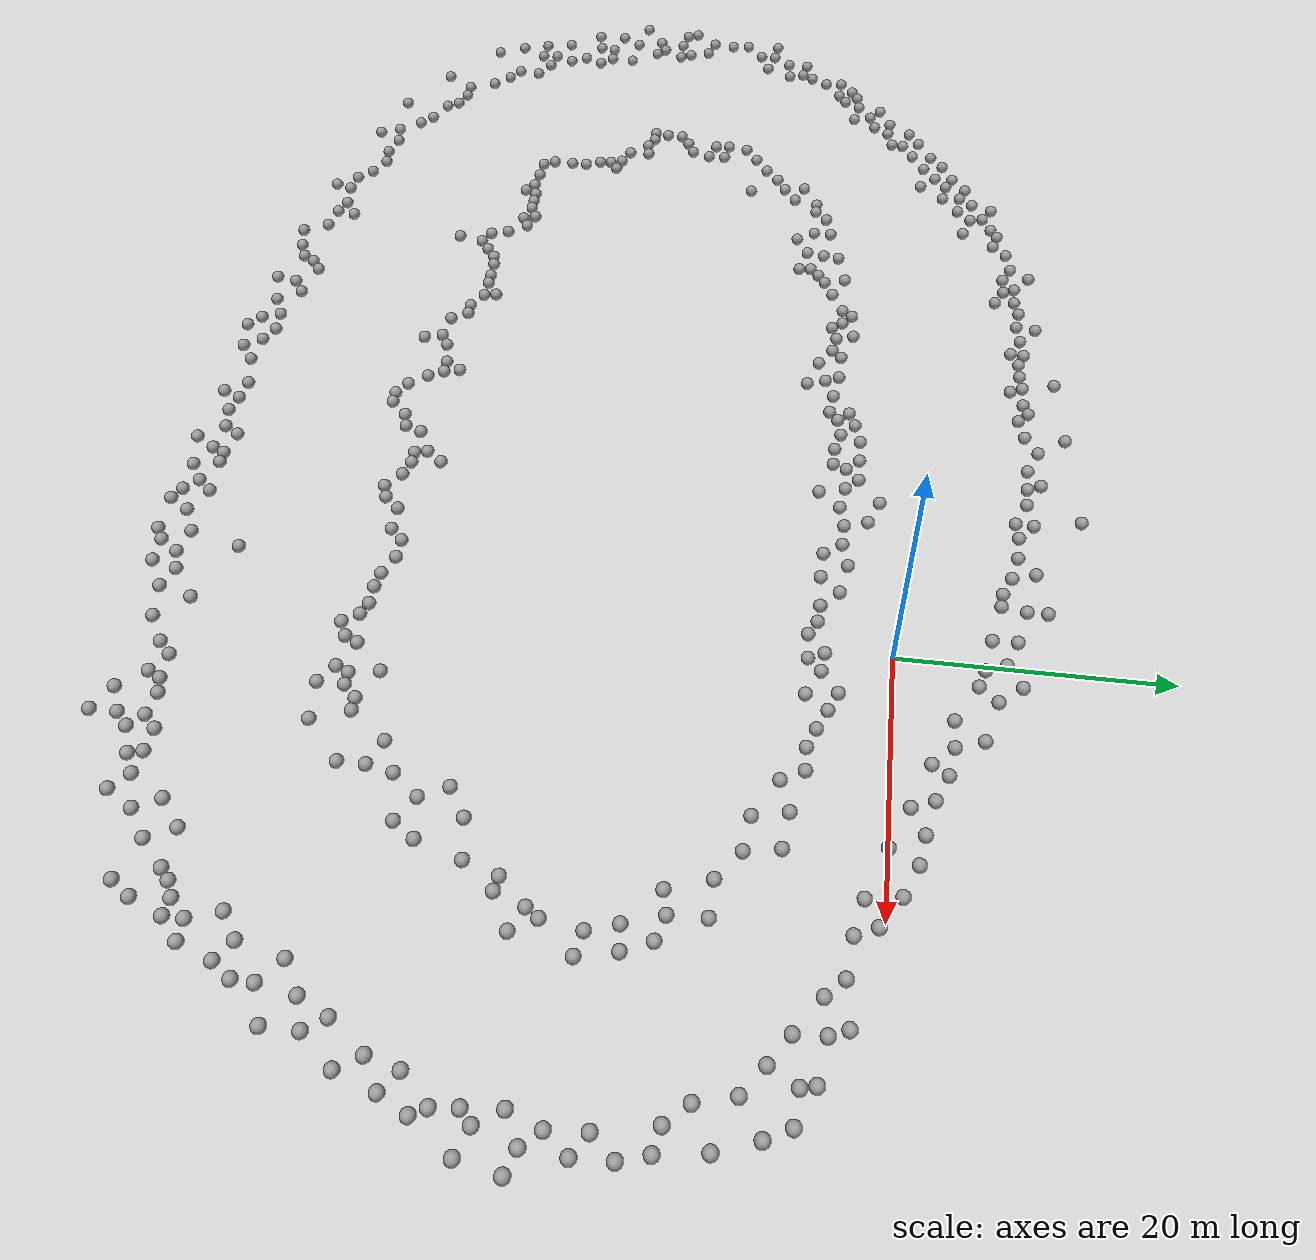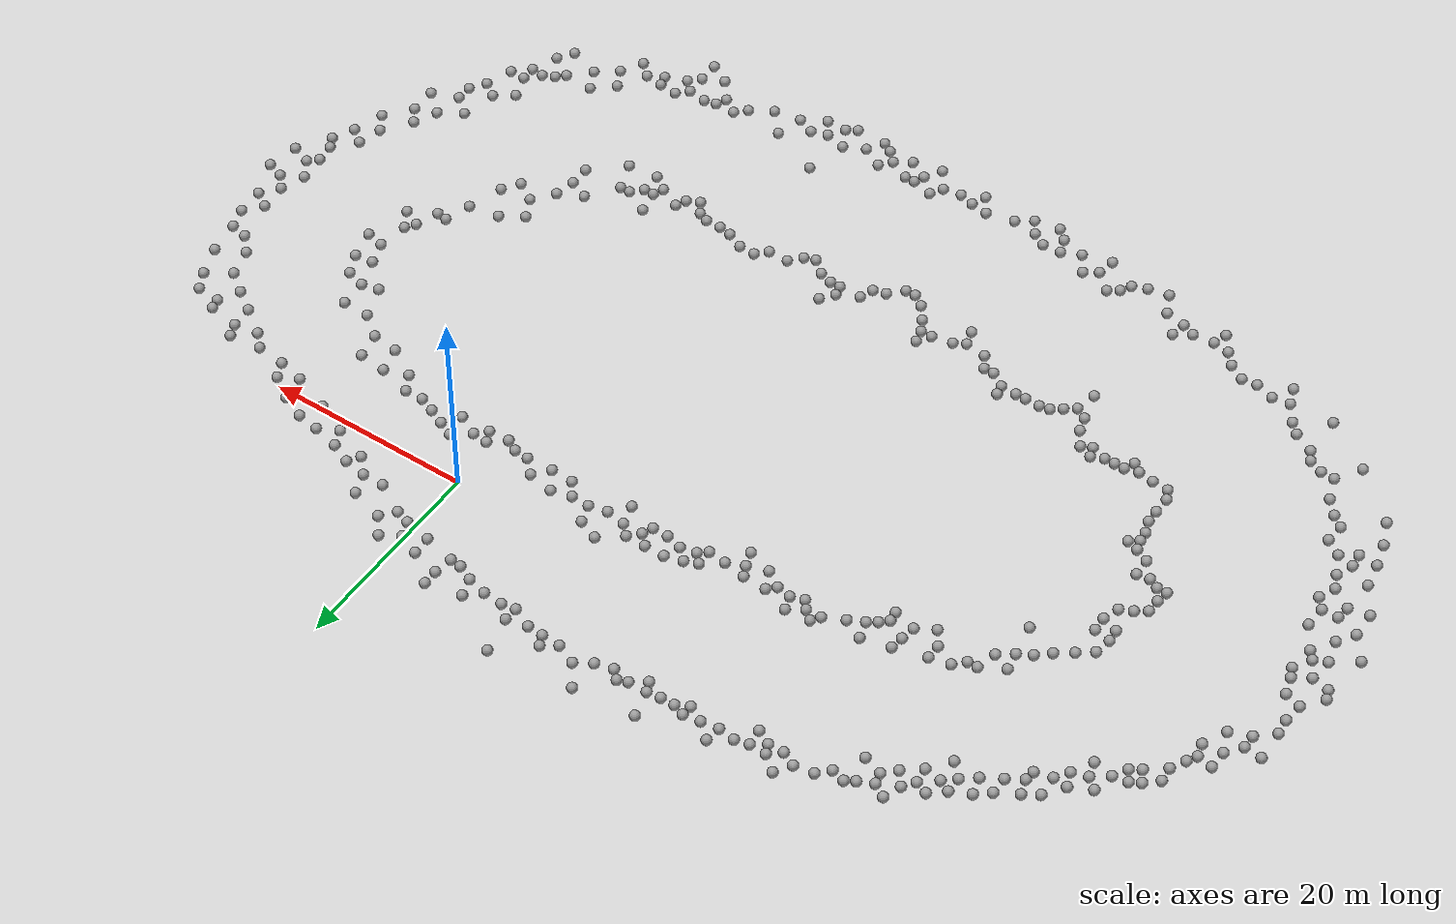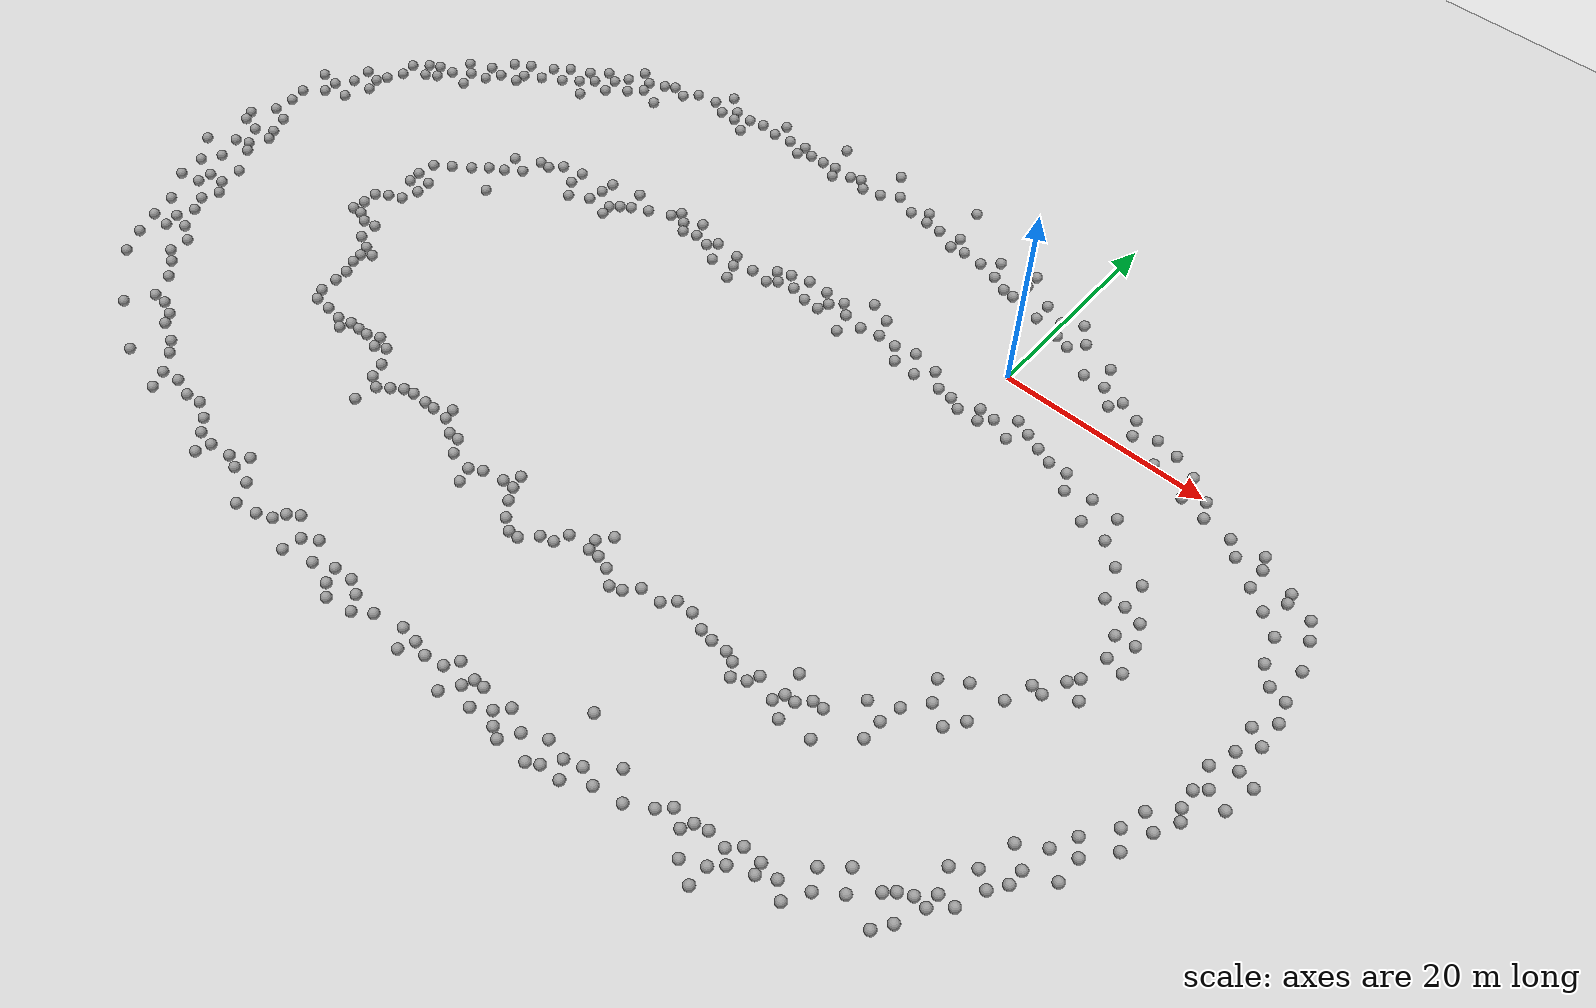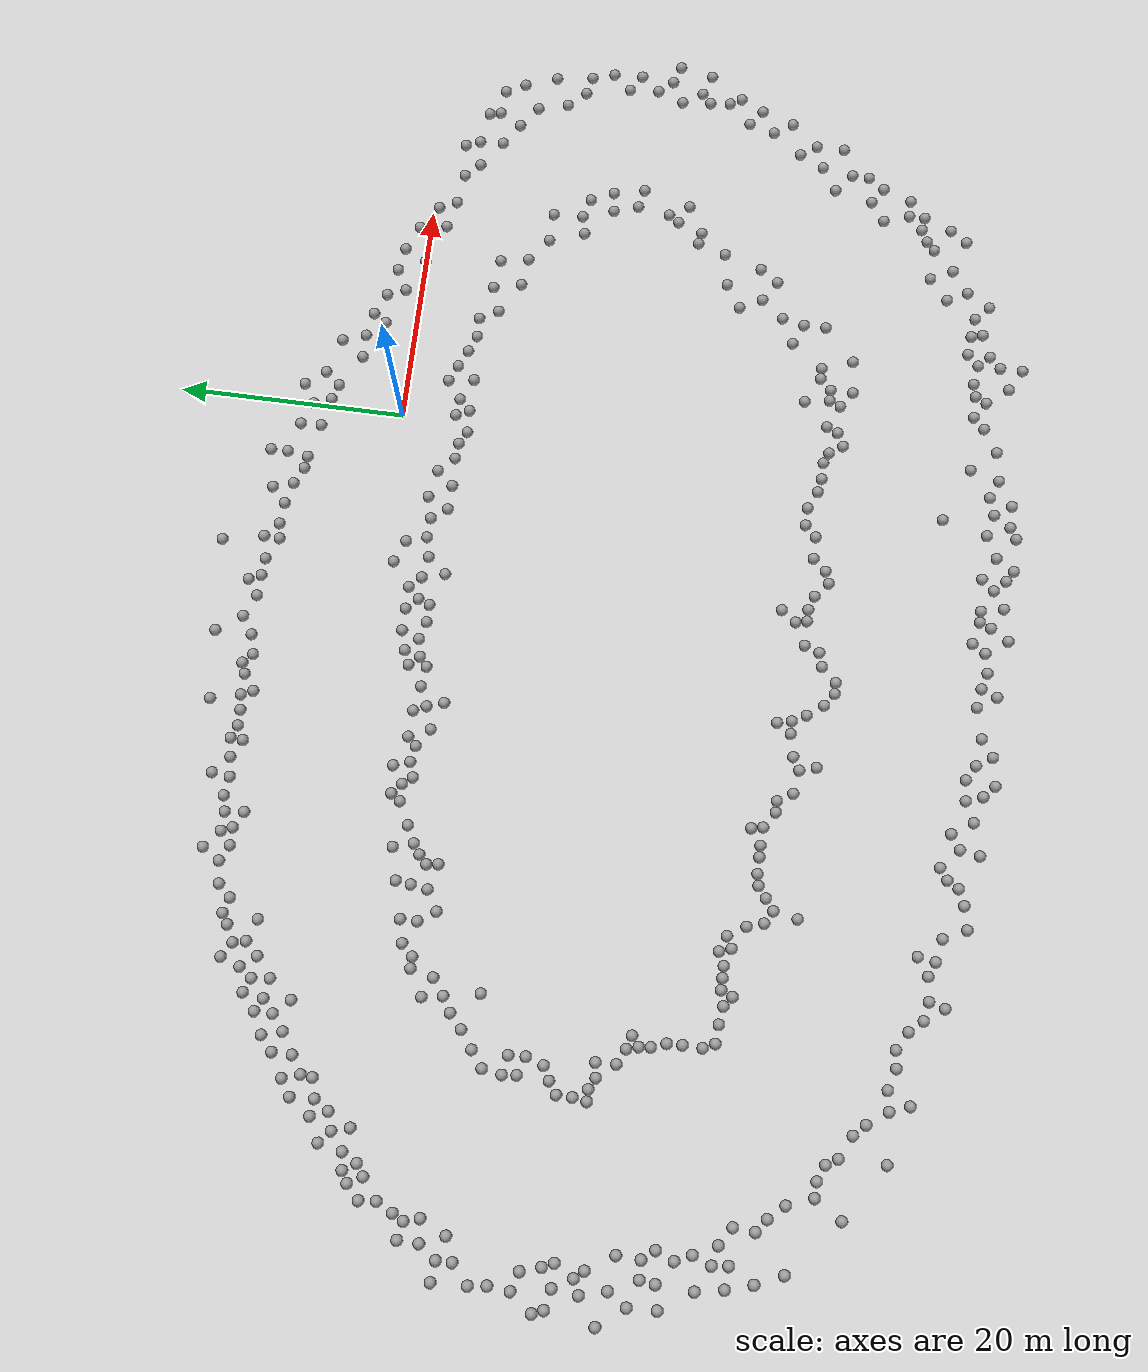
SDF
<sdf version="1.6">
 <world name="default">
  <light name="sun" type="directional">
   <pose>0 0 10 0 -0 0</pose>
   <diffuse>0.8 0.8 0.8 1</diffuse>
   <specular>0.1 0.1 0.1 1</specular>
   <attenuation>
    <range>1000</range>
    <constant>0.9</constant>
    <linear>0.01</linear>
    <quadratic>0.001</quadratic>
   </attenuation>
   <direction>-0.5 0.5 -1</direction>
  </light>
  <model name="ground_plane">
   <static>1</static>
   <link name="link">
    <collision name="collision">
     <geometry><plane><normal>0 0 1</normal><size>100 100</size></plane></geometry>
     <surface><friction><ode><mu>100</mu><mu2>50</mu2></ode></friction></surface>
    </collision>
    <visual name="visual">
     <cast_shadows>0</cast_shadows>
     <geometry><plane><normal>0 0 1</normal><size>100 100</size></plane></geometry>
     <material>
      <script><uri>file://media/materials/scripts/gazebo.material</uri><name>Gazebo/Grey</name></script>
     </material>
    </visual>
   </link>
  </model>
  <gravity>0 0 -9.8</gravity>
  <magnetic_field>6e-06 2.3e-05 -4.2e-05</magnetic_field>
  <atmosphere type="adiabatic"/>
  <physics name="default_physics" default="0" type="ode">
   <max_step_size>0.001</max_step_size>
   <real_time_factor>1</real_time_factor>
   <real_time_update_rate>1000</real_time_update_rate>
  </physics>
  <scene><ambient>0.4 0.4 0.4 1</ambient><background>0.7 0.7 0.7 1</background><shadows>1</shadows></scene>
  <spherical_coordinates>
   <surface_model>EARTH_WGS84</surface_model>
   <latitude_deg>0</latitude_deg>
   <longitude_deg>0</longitude_deg>
   <elevation>0</elevation>
   <heading_deg>0</heading_deg>
  </spherical_coordinates>
  <model name="unit_sphere_0">
   <pose>5.15486 -4.38811 0.5 0 -0 0</pose>
   <link name="link">
    <inertial>
     <mass>1</mass>
     <inertia><ixx>0.1</ixx><ixy>0</ixy><ixz>0</ixz><iyy>0.1</iyy><iyz>0</iyz><izz>0.1</izz></inertia>
    </inertial>
    <collision name="collision"><geometry><sphere><radius>0.5</radius></sphere></geometry></collision>
    <visual name="visual">
     <geometry><sphere><radius>0.5</radius></sphere></geometry>
     <material>
      <script><name>Gazebo/Grey</name><uri>file://media/materials/scripts/gazebo.material</uri></script>
     </material>
    </visual>
   </link>
  </model>
  <model name="unit_sphere_0_clone">
   <pose>6.71384 -5.09296 0.5 0 -0 0</pose>
   <link name="link">
    <inertial>
     <mass>1</mass>
     <inertia><ixx>0.1</ixx><ixy>0</ixy><ixz>0</ixz><iyy>0.1</iyy><iyz>0</iyz><izz>0.1</izz></inertia>
    </inertial>
    <collision name="collision"><geometry><sphere><radius>0.5</radius></sphere></geometry></collision>
    <visual name="visual">
     <geometry><sphere><radius>0.5</radius></sphere></geometry>
     <material>
      <script><name>Gazebo/Grey</name><uri>file://media/materials/scripts/gazebo.material</uri></script>
     </material>
    </visual>
   </link>
  </model>
  <model name="unit_sphere_0_clone_0">
   <pose>8.23139 -5.68918 0.5 0 -0 0</pose>
   <link name="link">
    <inertial>
     <mass>1</mass>
     <inertia><ixx>0.1</ixx><ixy>0</ixy><ixz>0</ixz><iyy>0.1</iyy><iyz>0</iyz><izz>0.1</izz></inertia>
    </inertial>
    <collision name="collision"><geometry><sphere><radius>0.5</radius></sphere></geometry></collision>
    <visual name="visual">
     <geometry><sphere><radius>0.5</radius></sphere></geometry>
     <material>
      <script><name>Gazebo/Grey</name><uri>file://media/materials/scripts/gazebo.material</uri></script>
     </material>
    </visual>
   </link>
  </model>
  <model name="unit_sphere_0_clone_1">
   <pose>10.0198 -5.65385 0.5 0 -0 0</pose>
   <link name="link">
    <inertial>
     <mass>1</mass>
     <inertia><ixx>0.1</ixx><ixy>0</ixy><ixz>0</ixz><iyy>0.1</iyy><iyz>0</iyz><izz>0.1</izz></inertia>
    </inertial>
    <collision name="collision"><geometry><sphere><radius>0.5</radius></sphere></geometry></collision>
    <visual name="visual">
     <geometry><sphere><radius>0.5</radius></sphere></geometry>
     <material>
      <script><name>Gazebo/Grey</name><uri>file://media/materials/scripts/gazebo.material</uri></script>
     </material>
    </visual>
   </link>
  </model>
  <model name="unit_sphere_0_clone_2">
   <pose>10.9217 -7.29328 0.5 0 -0 0</pose>
   <link name="link">
    <inertial>
     <mass>1</mass>
     <inertia><ixx>0.1</ixx><ixy>0</ixy><ixz>0</ixz><iyy>0.1</iyy><iyz>0</iyz><izz>0.1</izz></inertia>
    </inertial>
    <collision name="collision"><geometry><sphere><radius>0.5</radius></sphere></geometry></collision>
    <visual name="visual">
     <geometry><sphere><radius>0.5</radius></sphere></geometry>
     <material>
      <script><name>Gazebo/Grey</name><uri>file://media/materials/scripts/gazebo.material</uri></script>
     </material>
    </visual>
   </link>
  </model>
  <model name="unit_sphere_0_clone_3">
   <pose>13.2089 -6.50721 0.5 0 -0 0</pose>
   <link name="link">
    <inertial>
     <mass>1</mass>
     <inertia><ixx>0.1</ixx><ixy>0</ixy><ixz>0</ixz><iyy>0.1</iyy><iyz>0</iyz><izz>0.1</izz></inertia>
    </inertial>
    <collision name="collision"><geometry><sphere><radius>0.5</radius></sphere></geometry></collision>
    <visual name="visual">
     <geometry><sphere><radius>0.5</radius></sphere></geometry>
     <material>
      <script><name>Gazebo/Grey</name><uri>file://media/materials/scripts/gazebo.material</uri></script>
     </material>
    </visual>
   </link>
  </model>
  <model name="unit_sphere_0_clone_4">
   <pose>13.7778 -8.99338 0.5 0 -0 0</pose>
   <link name="link">
    <inertial>
     <mass>1</mass>
     <inertia><ixx>0.1</ixx><ixy>0</ixy><ixz>0</ixz><iyy>0.1</iyy><iyz>0</iyz><izz>0.1</izz></inertia>
    </inertial>
    <collision name="collision"><geometry><sphere><radius>0.5</radius></sphere></geometry></collision>
    <visual name="visual">
     <geometry><sphere><radius>0.5</radius></sphere></geometry>
     <material>
      <script><name>Gazebo/Grey</name><uri>file://media/materials/scripts/gazebo.material</uri></script>
     </material>
    </visual>
   </link>
  </model>
  <model name="unit_sphere_0_clone_5">
   <pose>15.8904 -6.82279 0.5 0 -0 0</pose>
   <link name="link">
    <inertial>
     <mass>1</mass>
     <inertia><ixx>0.1</ixx><ixy>0</ixy><ixz>0</ixz><iyy>0.1</iyy><iyz>0</iyz><izz>0.1</izz></inertia>
    </inertial>
    <collision name="collision"><geometry><sphere><radius>0.5</radius></sphere></geometry></collision>
    <visual name="visual">
     <geometry><sphere><radius>0.5</radius></sphere></geometry>
     <material>
      <script><name>Gazebo/Grey</name><uri>file://media/materials/scripts/gazebo.material</uri></script>
     </material>
    </visual>
   </link>
  </model>
  <model name="unit_sphere_0_clone_6">
   <pose>16.3495 -9.32648 0.5 0 -0 0</pose>
   <link name="link">
    <inertial>
     <mass>1</mass>
     <inertia><ixx>0.1</ixx><ixy>0</ixy><ixz>0</ixz><iyy>0.1</iyy><iyz>0</iyz><izz>0.1</izz></inertia>
    </inertial>
    <collision name="collision"><geometry><sphere><radius>0.5</radius></sphere></geometry></collision>
    <visual name="visual">
     <geometry><sphere><radius>0.5</radius></sphere></geometry>
     <material>
      <script><name>Gazebo/Grey</name><uri>file://media/materials/scripts/gazebo.material</uri></script>
     </material>
    </visual>
   </link>
  </model>
  <model name="unit_sphere_0_clone_7">
   <pose>7.08774 4.29856 0.5 0 -0 0</pose>
   <link name="link">
    <inertial>
     <mass>1</mass>
     <inertia><ixx>0.1</ixx><ixy>0</ixy><ixz>0</ixz><iyy>0.1</iyy><iyz>0</iyz><izz>0.1</izz></inertia>
    </inertial>
    <collision name="collision"><geometry><sphere><radius>0.5</radius></sphere></geometry></collision>
    <visual name="visual">
     <geometry><sphere><radius>0.5</radius></sphere></geometry>
     <material>
      <script><name>Gazebo/Grey</name><uri>file://media/materials/scripts/gazebo.material</uri></script>
     </material>
    </visual>
   </link>
  </model>
  <model name="unit_sphere_0_clone_8">
   <pose>8.53893 2.74635 0.5 0 -0 0</pose>
   <link name="link">
    <inertial>
     <mass>1</mass>
     <inertia><ixx>0.1</ixx><ixy>0</ixy><ixz>0</ixz><iyy>0.1</iyy><iyz>0</iyz><izz>0.1</izz></inertia>
    </inertial>
    <collision name="collision"><geometry><sphere><radius>0.5</radius></sphere></geometry></collision>
    <visual name="visual">
     <geometry><sphere><radius>0.5</radius></sphere></geometry>
     <material>
      <script><name>Gazebo/Grey</name><uri>file://media/materials/scripts/gazebo.material</uri></script>
     </material>
    </visual>
   </link>
  </model>
  <model name="unit_sphere_0_clone_9">
   <pose>9.28861 3.90002 0.5 0 -0 0</pose>
   <link name="link">
    <inertial>
     <mass>1</mass>
     <inertia><ixx>0.1</ixx><ixy>0</ixy><ixz>0</ixz><iyy>0.1</iyy><iyz>0</iyz><izz>0.1</izz></inertia>
    </inertial>
    <collision name="collision"><geometry><sphere><radius>0.5</radius></sphere></geometry></collision>
    <visual name="visual">
     <geometry><sphere><radius>0.5</radius></sphere></geometry>
     <material>
      <script><name>Gazebo/Grey</name><uri>file://media/materials/scripts/gazebo.material</uri></script>
     </material>
    </visual>
   </link>
  </model>
  <model name="unit_sphere_0_clone_10">
   <pose>11.2754 3.00631 0.5 0 -0 0</pose>
   <link name="link">
    <inertial>
     <mass>1</mass>
     <inertia><ixx>0.1</ixx><ixy>0</ixy><ixz>0</ixz><iyy>0.1</iyy><iyz>0</iyz><izz>0.1</izz></inertia>
    </inertial>
    <collision name="collision"><geometry><sphere><radius>0.5</radius></sphere></geometry></collision>
    <visual name="visual">
     <geometry><sphere><radius>0.5</radius></sphere></geometry>
     <material>
      <script><name>Gazebo/Grey</name><uri>file://media/materials/scripts/gazebo.material</uri></script>
     </material>
    </visual>
   </link>
  </model>
  <model name="unit_sphere_0_clone_11">
   <pose>11.9433 1.38371 0.5 0 -0 0</pose>
   <link name="link">
    <inertial>
     <mass>1</mass>
     <inertia><ixx>0.1</ixx><ixy>0</ixy><ixz>0</ixz><iyy>0.1</iyy><iyz>0</iyz><izz>0.1</izz></inertia>
    </inertial>
    <collision name="collision"><geometry><sphere><radius>0.5</radius></sphere></geometry></collision>
    <visual name="visual">
     <geometry><sphere><radius>0.5</radius></sphere></geometry>
     <material>
      <script><name>Gazebo/Grey</name><uri>file://media/materials/scripts/gazebo.material</uri></script>
     </material>
    </visual>
   </link>
  </model>
  <model name="unit_sphere_0_clone_12">
   <pose>13.8434 2.38423 0.5 0 -0 0</pose>
   <link name="link">
    <inertial>
     <mass>1</mass>
     <inertia><ixx>0.1</ixx><ixy>0</ixy><ixz>0</ixz><iyy>0.1</iyy><iyz>0</iyz><izz>0.1</izz></inertia>
    </inertial>
    <collision name="collision"><geometry><sphere><radius>0.5</radius></sphere></geometry></collision>
    <visual name="visual">
     <geometry><sphere><radius>0.5</radius></sphere></geometry>
     <material>
      <script><name>Gazebo/Grey</name><uri>file://media/materials/scripts/gazebo.material</uri></script>
     </material>
    </visual>
   </link>
  </model>
  <model name="unit_sphere_0_clone_13">
   <pose>15 0 0.5 0 -0 0</pose>
   <link name="link">
    <inertial>
     <mass>1</mass>
     <inertia><ixx>0.1</ixx><ixy>0</ixy><ixz>0</ixz><iyy>0.1</iyy><iyz>0</iyz><izz>0.1</izz></inertia>
    </inertial>
    <collision name="collision"><geometry><sphere><radius>0.5</radius></sphere></geometry></collision>
    <visual name="visual">
     <geometry><sphere><radius>0.5</radius></sphere></geometry>
     <material>
      <script><name>Gazebo/Grey</name><uri>file://media/materials/scripts/gazebo.material</uri></script>
     </material>
    </visual>
   </link>
  </model>
  <model name="unit_sphere_0_clone_14">
   <pose>16 2 0.5 0 -0 0</pose>
   <link name="link">
    <inertial>
     <mass>1</mass>
     <inertia><ixx>0.1</ixx><ixy>0</ixy><ixz>0</ixz><iyy>0.1</iyy><iyz>0</iyz><izz>0.1</izz></inertia>
    </inertial>
    <collision name="collision"><geometry><sphere><radius>0.5</radius></sphere></geometry></collision>
    <visual name="visual">
     <geometry><sphere><radius>0.5</radius></sphere></geometry>
     <material>
      <script><name>Gazebo/Grey</name><uri>file://media/materials/scripts/gazebo.material</uri></script>
     </material>
    </visual>
   </link>
  </model>
  <model name="unit_sphere_0_clone_15">
   <pose>18.3018 0.995003 0.5 0 -0 0</pose>
   <link name="link">
    <inertial>
     <mass>1</mass>
     <inertia><ixx>0.1</ixx><ixy>0</ixy><ixz>0</ixz><iyy>0.1</iyy><iyz>0</iyz><izz>0.1</izz></inertia>
    </inertial>
    <collision name="collision"><geometry><sphere><radius>0.5</radius></sphere></geometry></collision>
    <visual name="visual">
     <geometry><sphere><radius>0.5</radius></sphere></geometry>
     <material>
      <script><name>Gazebo/Grey</name><uri>file://media/materials/scripts/gazebo.material</uri></script>
     </material>
    </visual>
   </link>
  </model>
  <model name="unit_sphere_0_clone_16">
   <pose>20.4898 -0.468795 0.5 0 -0 0</pose>
   <link name="link">
    <inertial>
     <mass>1</mass>
     <inertia><ixx>0.1</ixx><ixy>0</ixy><ixz>0</ixz><iyy>0.1</iyy><iyz>0</iyz><izz>0.1</izz></inertia>
    </inertial>
    <collision name="collision"><geometry><sphere><radius>0.5</radius></sphere></geometry></collision>
    <visual name="visual">
     <geometry><sphere><radius>0.5</radius></sphere></geometry>
     <material>
      <script><name>Gazebo/Grey</name><uri>file://media/materials/scripts/gazebo.material</uri></script>
     </material>
    </visual>
   </link>
  </model>
  <model name="unit_sphere_0_clone_17">
   <pose>24.0194 -2.37066 0.5 0 -0 0</pose>
   <link name="link">
    <inertial>
     <mass>1</mass>
     <inertia><ixx>0.1</ixx><ixy>0</ixy><ixz>0</ixz><iyy>0.1</iyy><iyz>0</iyz><izz>0.1</izz></inertia>
    </inertial>
    <collision name="collision"><geometry><sphere><radius>0.5</radius></sphere></geometry></collision>
    <visual name="visual">
     <geometry><sphere><radius>0.5</radius></sphere></geometry>
     <material>
      <script><name>Gazebo/Grey</name><uri>file://media/materials/scripts/gazebo.material</uri></script>
     </material>
    </visual>
   </link>
  </model>
  <model name="unit_sphere_0_clone_18">
   <pose>27.7503 -5.42436 0.5 0 -0 0</pose>
   <link name="link">
    <inertial>
     <mass>1</mass>
     <inertia><ixx>0.1</ixx><ixy>0</ixy><ixz>0</ixz><iyy>0.1</iyy><iyz>0</iyz><izz>0.1</izz></inertia>
    </inertial>
    <collision name="collision"><geometry><sphere><radius>0.5</radius></sphere></geometry></collision>
    <visual name="visual">
     <geometry><sphere><radius>0.5</radius></sphere></geometry>
     <material>
      <script><name>Gazebo/Grey</name><uri>file://media/materials/scripts/gazebo.material</uri></script>
     </material>
    </visual>
   </link>
  </model>
  <model name="unit_sphere_0_clone_19">
   <pose>31.6938 -8.24862 0.5 0 -0 0</pose>
   <link name="link">
    <inertial>
     <mass>1</mass>
     <inertia><ixx>0.1</ixx><ixy>0</ixy><ixz>0</ixz><iyy>0.1</iyy><iyz>0</iyz><izz>0.1</izz></inertia>
    </inertial>
    <collision name="collision"><geometry><sphere><radius>0.5</radius></sphere></geometry></collision>
    <visual name="visual">
     <geometry><sphere><radius>0.5</radius></sphere></geometry>
     <material>
      <script><name>Gazebo/Grey</name><uri>file://media/materials/scripts/gazebo.material</uri></script>
     </material>
    </visual>
   </link>
  </model>
  <model name="unit_sphere_0_clone_20">
   <pose>33.8259 -12.4839 0.5 0 -0 0</pose>
   <link name="link">
    <inertial>
     <mass>1</mass>
     <inertia><ixx>0.1</ixx><ixy>0</ixy><ixz>0</ixz><iyy>0.1</iyy><iyz>0</iyz><izz>0.1</izz></inertia>
    </inertial>
    <collision name="collision"><geometry><sphere><radius>0.5</radius></sphere></geometry></collision>
    <visual name="visual">
     <geometry><sphere><radius>0.5</radius></sphere></geometry>
     <material>
      <script><name>Gazebo/Grey</name><uri>file://media/materials/scripts/gazebo.material</uri></script>
     </material>
    </visual>
   </link>
  </model>
  <model name="unit_sphere_0_clone_21">
   <pose>34.8751 -19.1706 0.5 0 -0 0</pose>
   <link name="link">
    <inertial>
     <mass>1</mass>
     <inertia><ixx>0.1</ixx><ixy>0</ixy><ixz>0</ixz><iyy>0.1</iyy><iyz>0</iyz><izz>0.1</izz></inertia>
    </inertial>
    <collision name="collision"><geometry><sphere><radius>0.5</radius></sphere></geometry></collision>
    <visual name="visual">
     <geometry><sphere><radius>0.5</radius></sphere></geometry>
     <material>
      <script><name>Gazebo/Grey</name><uri>file://media/materials/scripts/gazebo.material</uri></script>
     </material>
    </visual>
   </link>
  </model>
  <model name="unit_sphere_0_clone_22">
   <pose>34.4274 -25.9481 0.5 0 -0 0</pose>
   <link name="link">
    <inertial>
     <mass>1</mass>
     <inertia><ixx>0.1</ixx><ixy>0</ixy><ixz>0</ixz><iyy>0.1</iyy><iyz>0</iyz><izz>0.1</izz></inertia>
    </inertial>
    <collision name="collision"><geometry><sphere><radius>0.5</radius></sphere></geometry></collision>
    <visual name="visual">
     <geometry><sphere><radius>0.5</radius></sphere></geometry>
     <material>
      <script><name>Gazebo/Grey</name><uri>file://media/materials/scripts/gazebo.material</uri></script>
     </material>
    </visual>
   </link>
  </model>
  <model name="unit_sphere_0_clone_23">
   <pose>28.938 -35.2104 0.5 0 -0 0</pose>
   <link name="link">
    <inertial>
     <mass>1</mass>
     <inertia><ixx>0.1</ixx><ixy>0</ixy><ixz>0</ixz><iyy>0.1</iyy><iyz>0</iyz><izz>0.1</izz></inertia>
    </inertial>
    <collision name="collision"><geometry><sphere><radius>0.5</radius></sphere></geometry></collision>
    <visual name="visual">
     <geometry><sphere><radius>0.5</radius></sphere></geometry>
     <material>
      <script><name>Gazebo/Grey</name><uri>file://media/materials/scripts/gazebo.material</uri></script>
     </material>
    </visual>
   </link>
  </model>
  <model name="unit_sphere_0_clone_24">
   <pose>22.6448 -45.4054 0.5 -0.042295 0.045819 -0.000971</pose>
   <link name="link">
    <inertial>
     <mass>1</mass>
     <inertia><ixx>0.1</ixx><ixy>0</ixy><ixz>0</ixz><iyy>0.1</iyy><iyz>0</iyz><izz>0.1</izz></inertia>
    </inertial>
    <collision name="collision"><geometry><sphere><radius>0.5</radius></sphere></geometry></collision>
    <visual name="visual">
     <geometry><sphere><radius>0.5</radius></sphere></geometry>
     <material>
      <script><name>Gazebo/Grey</name><uri>file://media/materials/scripts/gazebo.material</uri></script>
     </material>
    </visual>
   </link>
  </model>
  <model name="unit_sphere_0_clone_25">
   <pose>16.8047 -51.5632 0.5 0 -0 0</pose>
   <link name="link">
    <inertial>
     <mass>1</mass>
     <inertia><ixx>0.1</ixx><ixy>0</ixy><ixz>0</ixz><iyy>0.1</iyy><iyz>0</iyz><izz>0.1</izz></inertia>
    </inertial>
    <collision name="collision"><geometry><sphere><radius>0.5</radius></sphere></geometry></collision>
    <visual name="visual">
     <geometry><sphere><radius>0.5</radius></sphere></geometry>
     <material>
      <script><name>Gazebo/Grey</name><uri>file://media/materials/scripts/gazebo.material</uri></script>
     </material>
    </visual>
   </link>
  </model>
  <model name="unit_sphere_0_clone_26">
   <pose>9.03106 -53.9187 0.5 0 -0 0</pose>
   <link name="link">
    <inertial>
     <mass>1</mass>
     <inertia><ixx>0.1</ixx><ixy>0</ixy><ixz>0</ixz><iyy>0.1</iyy><iyz>0</iyz><izz>0.1</izz></inertia>
    </inertial>
    <collision name="collision"><geometry><sphere><radius>0.5</radius></sphere></geometry></collision>
    <visual name="visual">
     <geometry><sphere><radius>0.5</radius></sphere></geometry>
     <material>
      <script><name>Gazebo/Grey</name><uri>file://media/materials/scripts/gazebo.material</uri></script>
     </material>
    </visual>
   </link>
  </model>
  <model name="unit_sphere_0_clone_27">
   <pose>0.231399 -53.6899 0.5 0 -0 0</pose>
   <link name="link">
    <inertial>
     <mass>1</mass>
     <inertia><ixx>0.1</ixx><ixy>0</ixy><ixz>0</ixz><iyy>0.1</iyy><iyz>0</iyz><izz>0.1</izz></inertia>
    </inertial>
    <collision name="collision"><geometry><sphere><radius>0.5</radius></sphere></geometry></collision>
    <visual name="visual">
     <geometry><sphere><radius>0.5</radius></sphere></geometry>
     <material>
      <script><name>Gazebo/Grey</name><uri>file://media/materials/scripts/gazebo.material</uri></script>
     </material>
    </visual>
   </link>
  </model>
  <model name="unit_sphere_0_clone_28">
   <pose>-9.04954 -52.8887 0.5 0 -0 0</pose>
   <link name="link">
    <inertial>
     <mass>1</mass>
     <inertia><ixx>0.1</ixx><ixy>0</ixy><ixz>0</ixz><iyy>0.1</iyy><iyz>0</iyz><izz>0.1</izz></inertia>
    </inertial>
    <collision name="collision"><geometry><sphere><radius>0.5</radius></sphere></geometry></collision>
    <visual name="visual">
     <geometry><sphere><radius>0.5</radius></sphere></geometry>
     <material>
      <script><name>Gazebo/Grey</name><uri>file://media/materials/scripts/gazebo.material</uri></script>
     </material>
    </visual>
   </link>
  </model>
  <model name="unit_sphere_0_clone_29">
   <pose>-15.0281 -52.5018 0.5 0 -0 0</pose>
   <link name="link">
    <inertial>
     <mass>1</mass>
     <inertia><ixx>0.1</ixx><ixy>0</ixy><ixz>0</ixz><iyy>0.1</iyy><iyz>0</iyz><izz>0.1</izz></inertia>
    </inertial>
    <collision name="collision"><geometry><sphere><radius>0.5</radius></sphere></geometry></collision>
    <visual name="visual">
     <geometry><sphere><radius>0.5</radius></sphere></geometry>
     <material>
      <script><name>Gazebo/Grey</name><uri>file://media/materials/scripts/gazebo.material</uri></script>
     </material>
    </visual>
   </link>
  </model>
  <model name="unit_sphere_0_clone_30">
   <pose>-20.6916 -53.3218 0.5 0 -0 0</pose>
   <link name="link">
    <inertial>
     <mass>1</mass>
     <inertia><ixx>0.1</ixx><ixy>0</ixy><ixz>0</ixz><iyy>0.1</iyy><iyz>0</iyz><izz>0.1</izz></inertia>
    </inertial>
    <collision name="collision"><geometry><sphere><radius>0.5</radius></sphere></geometry></collision>
    <visual name="visual">
     <geometry><sphere><radius>0.5</radius></sphere></geometry>
     <material>
      <script><name>Gazebo/Grey</name><uri>file://media/materials/scripts/gazebo.material</uri></script>
     </material>
    </visual>
   </link>
  </model>
  <model name="unit_sphere_0_clone_31">
   <pose>-27.1746 -52.8869 0.5 0 -0 0</pose>
   <link name="link">
    <inertial>
     <mass>1</mass>
     <inertia><ixx>0.1</ixx><ixy>0</ixy><ixz>0</ixz><iyy>0.1</iyy><iyz>0</iyz><izz>0.1</izz></inertia>
    </inertial>
    <collision name="collision"><geometry><sphere><radius>0.5</radius></sphere></geometry></collision>
    <visual name="visual">
     <geometry><sphere><radius>0.5</radius></sphere></geometry>
     <material>
      <script><name>Gazebo/Grey</name><uri>file://media/materials/scripts/gazebo.material</uri></script>
     </material>
    </visual>
   </link>
  </model>
  <model name="unit_sphere_0_clone_32">
   <pose>-35.0036 -51.2997 0.5 0 -0 0</pose>
   <link name="link">
    <inertial>
     <mass>1</mass>
     <inertia><ixx>0.1</ixx><ixy>0</ixy><ixz>0</ixz><iyy>0.1</iyy><iyz>0</iyz><izz>0.1</izz></inertia>
    </inertial>
    <collision name="collision"><geometry><sphere><radius>0.5</radius></sphere></geometry></collision>
    <visual name="visual">
     <geometry><sphere><radius>0.5</radius></sphere></geometry>
     <material>
      <script><name>Gazebo/Grey</name><uri>file://media/materials/scripts/gazebo.material</uri></script>
     </material>
    </visual>
   </link>
  </model>
  <model name="unit_sphere_0_clone_33">
   <pose>-42.7451 -50.0544 0.5 0 -0 0</pose>
   <link name="link">
    <inertial>
     <mass>1</mass>
     <inertia><ixx>0.1</ixx><ixy>0</ixy><ixz>0</ixz><iyy>0.1</iyy><iyz>0</iyz><izz>0.1</izz></inertia>
    </inertial>
    <collision name="collision"><geometry><sphere><radius>0.5</radius></sphere></geometry></collision>
    <visual name="visual">
     <geometry><sphere><radius>0.5</radius></sphere></geometry>
     <material>
      <script><name>Gazebo/Grey</name><uri>file://media/materials/scripts/gazebo.material</uri></script>
     </material>
    </visual>
   </link>
  </model>
  <model name="unit_sphere_0_clone_34">
   <pose>-50.6516 -48.9094 0.5 0 -0 0</pose>
   <link name="link">
    <inertial>
     <mass>1</mass>
     <inertia><ixx>0.1</ixx><ixy>0</ixy><ixz>0</ixz><iyy>0.1</iyy><iyz>0</iyz><izz>0.1</izz></inertia>
    </inertial>
    <collision name="collision"><geometry><sphere><radius>0.5</radius></sphere></geometry></collision>
    <visual name="visual">
     <geometry><sphere><radius>0.5</radius></sphere></geometry>
     <material>
      <script><name>Gazebo/Grey</name><uri>file://media/materials/scripts/gazebo.material</uri></script>
     </material>
    </visual>
   </link>
  </model>
  <model name="unit_sphere_0_clone_35">
   <pose>-60 -45 0.5 0 -0 0</pose>
   <link name="link">
    <inertial>
     <mass>1</mass>
     <inertia><ixx>0.1</ixx><ixy>0</ixy><ixz>0</ixz><iyy>0.1</iyy><iyz>0</iyz><izz>0.1</izz></inertia>
    </inertial>
    <collision name="collision"><geometry><sphere><radius>0.5</radius></sphere></geometry></collision>
    <visual name="visual">
     <geometry><sphere><radius>0.5</radius></sphere></geometry>
     <material>
      <script><name>Gazebo/Grey</name><uri>file://media/materials/scripts/gazebo.material</uri></script>
     </material>
    </visual>
   </link>
  </model>
  <model name="unit_sphere_0_clone_36">
   <pose>-66.593 -38.8584 0.5 0 -0 0</pose>
   <link name="link">
    <inertial>
     <mass>1</mass>
     <inertia><ixx>0.1</ixx><ixy>0</ixy><ixz>0</ixz><iyy>0.1</iyy><iyz>0</iyz><izz>0.1</izz></inertia>
    </inertial>
    <collision name="collision"><geometry><sphere><radius>0.5</radius></sphere></geometry></collision>
    <visual name="visual">
     <geometry><sphere><radius>0.5</radius></sphere></geometry>
     <material>
      <script><name>Gazebo/Grey</name><uri>file://media/materials/scripts/gazebo.material</uri></script>
     </material>
    </visual>
   </link>
  </model>
  <model name="unit_sphere_0_clone_37">
   <pose>-71.4541 -29.9614 0.5 0 -0 0</pose>
   <link name="link">
    <inertial>
     <mass>1</mass>
     <inertia><ixx>0.1</ixx><ixy>0</ixy><ixz>0</ixz><iyy>0.1</iyy><iyz>0</iyz><izz>0.1</izz></inertia>
    </inertial>
    <collision name="collision"><geometry><sphere><radius>0.5</radius></sphere></geometry></collision>
    <visual name="visual">
     <geometry><sphere><radius>0.5</radius></sphere></geometry>
     <material>
      <script><name>Gazebo/Grey</name><uri>file://media/materials/scripts/gazebo.material</uri></script>
     </material>
    </visual>
   </link>
  </model>
  <model name="unit_sphere_0_clone_38">
   <pose>-73 -23 0.5 0 -0 0</pose>
   <link name="link">
    <inertial>
     <mass>1</mass>
     <inertia><ixx>0.1</ixx><ixy>0</ixy><ixz>0</ixz><iyy>0.1</iyy><iyz>0</iyz><izz>0.1</izz></inertia>
    </inertial>
    <collision name="collision"><geometry><sphere><radius>0.5</radius></sphere></geometry></collision>
    <visual name="visual">
     <geometry><sphere><radius>0.5</radius></sphere></geometry>
     <material>
      <script><name>Gazebo/Grey</name><uri>file://media/materials/scripts/gazebo.material</uri></script>
     </material>
    </visual>
   </link>
  </model>
  <model name="unit_sphere_0_clone_39">
   <pose>-71.9959 -14.7912 0.5 0 -0 0</pose>
   <link name="link">
    <inertial>
     <mass>1</mass>
     <inertia><ixx>0.1</ixx><ixy>0</ixy><ixz>0</ixz><iyy>0.1</iyy><iyz>0</iyz><izz>0.1</izz></inertia>
    </inertial>
    <collision name="collision"><geometry><sphere><radius>0.5</radius></sphere></geometry></collision>
    <visual name="visual">
     <geometry><sphere><radius>0.5</radius></sphere></geometry>
     <material>
      <script><name>Gazebo/Grey</name><uri>file://media/materials/scripts/gazebo.material</uri></script>
     </material>
    </visual>
   </link>
  </model>
  <model name="unit_sphere_0_clone_40">
   <pose>-65.2346 -5.96361 0.5 0 -0 0</pose>
   <link name="link">
    <inertial>
     <mass>1</mass>
     <inertia><ixx>0.1</ixx><ixy>0</ixy><ixz>0</ixz><iyy>0.1</iyy><iyz>0</iyz><izz>0.1</izz></inertia>
    </inertial>
    <collision name="collision"><geometry><sphere><radius>0.5</radius></sphere></geometry></collision>
    <visual name="visual">
     <geometry><sphere><radius>0.5</radius></sphere></geometry>
     <material>
      <script><name>Gazebo/Grey</name><uri>file://media/materials/scripts/gazebo.material</uri></script>
     </material>
    </visual>
   </link>
  </model>
  <model name="unit_sphere_0_clone_41">
   <pose>-55.4814 1.77001 0.5 0 -0 0</pose>
   <link name="link">
    <inertial>
     <mass>1</mass>
     <inertia><ixx>0.1</ixx><ixy>0</ixy><ixz>0</ixz><iyy>0.1</iyy><iyz>0</iyz><izz>0.1</izz></inertia>
    </inertial>
    <collision name="collision"><geometry><sphere><radius>0.5</radius></sphere></geometry></collision>
    <visual name="visual">
     <geometry><sphere><radius>0.5</radius></sphere></geometry>
     <material>
      <script><name>Gazebo/Grey</name><uri>file://media/materials/scripts/gazebo.material</uri></script>
     </material>
    </visual>
   </link>
  </model>
  <model name="unit_sphere_0_clone_42">
   <pose>-46.5174 5.3531 0.5 0 -0 0</pose>
   <link name="link">
    <inertial>
     <mass>1</mass>
     <inertia><ixx>0.1</ixx><ixy>0</ixy><ixz>0</ixz><iyy>0.1</iyy><iyz>0</iyz><izz>0.1</izz></inertia>
    </inertial>
    <collision name="collision"><geometry><sphere><radius>0.5</radius></sphere></geometry></collision>
    <visual name="visual">
     <geometry><sphere><radius>0.5</radius></sphere></geometry>
     <material>
      <script><name>Gazebo/Grey</name><uri>file://media/materials/scripts/gazebo.material</uri></script>
     </material>
    </visual>
   </link>
  </model>
  <model name="unit_sphere_0_clone_43">
   <pose>-37.6069 8.01409 0.5 0 -0 0</pose>
   <link name="link">
    <inertial>
     <mass>1</mass>
     <inertia><ixx>0.1</ixx><ixy>0</ixy><ixz>0</ixz><iyy>0.1</iyy><iyz>0</iyz><izz>0.1</izz></inertia>
    </inertial>
    <collision name="collision"><geometry><sphere><radius>0.5</radius></sphere></geometry></collision>
    <visual name="visual">
     <geometry><sphere><radius>0.5</radius></sphere></geometry>
     <material>
      <script><name>Gazebo/Grey</name><uri>file://media/materials/scripts/gazebo.material</uri></script>
     </material>
    </visual>
   </link>
  </model>
  <model name="unit_sphere_0_clone_44">
   <pose>-31.3408 10.2531 0.5 0 -0 0</pose>
   <link name="link">
    <inertial>
     <mass>1</mass>
     <inertia><ixx>0.1</ixx><ixy>0</ixy><ixz>0</ixz><iyy>0.1</iyy><iyz>0</iyz><izz>0.1</izz></inertia>
    </inertial>
    <collision name="collision"><geometry><sphere><radius>0.5</radius></sphere></geometry></collision>
    <visual name="visual">
     <geometry><sphere><radius>0.5</radius></sphere></geometry>
     <material>
      <script><name>Gazebo/Grey</name><uri>file://media/materials/scripts/gazebo.material</uri></script>
     </material>
    </visual>
   </link>
  </model>
  <model name="unit_sphere_0_clone_45">
   <pose>-24.6013 10.3687 0.5 0 -0 0</pose>
   <link name="link">
    <inertial>
     <mass>1</mass>
     <inertia><ixx>0.1</ixx><ixy>0</ixy><ixz>0</ixz><iyy>0.1</iyy><iyz>0</iyz><izz>0.1</izz></inertia>
    </inertial>
    <collision name="collision"><geometry><sphere><radius>0.5</radius></sphere></geometry></collision>
    <visual name="visual">
     <geometry><sphere><radius>0.5</radius></sphere></geometry>
     <material>
      <script><name>Gazebo/Grey</name><uri>file://media/materials/scripts/gazebo.material</uri></script>
     </material>
    </visual>
   </link>
  </model>
  <model name="unit_sphere_0_clone_46">
   <pose>-17.0385 11.0775 0.5 0 -0 0</pose>
   <link name="link">
    <inertial>
     <mass>1</mass>
     <inertia><ixx>0.1</ixx><ixy>0</ixy><ixz>0</ixz><iyy>0.1</iyy><iyz>0</iyz><izz>0.1</izz></inertia>
    </inertial>
    <collision name="collision"><geometry><sphere><radius>0.5</radius></sphere></geometry></collision>
    <visual name="visual">
     <geometry><sphere><radius>0.5</radius></sphere></geometry>
     <material>
      <script><name>Gazebo/Grey</name><uri>file://media/materials/scripts/gazebo.material</uri></script>
     </material>
    </visual>
   </link>
  </model>
  <model name="unit_sphere_0_clone_47">
   <pose>-8.29138 10.353 0.5 0 -0 0</pose>
   <link name="link">
    <inertial>
     <mass>1</mass>
     <inertia><ixx>0.1</ixx><ixy>0</ixy><ixz>0</ixz><iyy>0.1</iyy><iyz>0</iyz><izz>0.1</izz></inertia>
    </inertial>
    <collision name="collision"><geometry><sphere><radius>0.5</radius></sphere></geometry></collision>
    <visual name="visual">
     <geometry><sphere><radius>0.5</radius></sphere></geometry>
     <material>
      <script><name>Gazebo/Grey</name><uri>file://media/materials/scripts/gazebo.material</uri></script>
     </material>
    </visual>
   </link>
  </model>
  <model name="unit_sphere_0_clone_48">
   <pose>-2.06402 8.83003 0.5 0 -0 0</pose>
   <link name="link">
    <inertial>
     <mass>1</mass>
     <inertia><ixx>0.1</ixx><ixy>0</ixy><ixz>0</ixz><iyy>0.1</iyy><iyz>0</iyz><izz>0.1</izz></inertia>
    </inertial>
    <collision name="collision"><geometry><sphere><radius>0.5</radius></sphere></geometry></collision>
    <visual name="visual">
     <geometry><sphere><radius>0.5</radius></sphere></geometry>
     <material>
      <script><name>Gazebo/Grey</name><uri>file://media/materials/scripts/gazebo.material</uri></script>
     </material>
    </visual>
   </link>
  </model>
  <model name="unit_sphere_0_clone_49">
   <pose>3.12178 7.33825 0.5 0 -0 0</pose>
   <link name="link">
    <inertial>
     <mass>1</mass>
     <inertia><ixx>0.1</ixx><ixy>0</ixy><ixz>0</ixz><iyy>0.1</iyy><iyz>0</iyz><izz>0.1</izz></inertia>
    </inertial>
    <collision name="collision"><geometry><sphere><radius>0.5</radius></sphere></geometry></collision>
    <visual name="visual">
     <geometry><sphere><radius>0.5</radius></sphere></geometry>
     <material>
      <script><name>Gazebo/Grey</name><uri>file://media/materials/scripts/gazebo.material</uri></script>
     </material>
    </visual>
   </link>
  </model>
  <model name="unit_sphere_0_clone_50">
   <pose>18.4855 -10.9718 0.5 0 -0 0</pose>
   <link name="link">
    <inertial>
     <mass>1</mass>
     <inertia><ixx>0.1</ixx><ixy>0</ixy><ixz>0</ixz><iyy>0.1</iyy><iyz>0</iyz><izz>0.1</izz></inertia>
    </inertial>
    <collision name="collision"><geometry><sphere><radius>0.5</radius></sphere></geometry></collision>
    <visual name="visual">
     <geometry><sphere><radius>0.5</radius></sphere></geometry>
     <material>
      <script><name>Gazebo/Grey</name><uri>file://media/materials/scripts/gazebo.material</uri></script>
     </material>
    </visual>
   </link>
  </model>
  <model name="unit_sphere_0_clone_51">
   <pose>19.5585 -14.0831 0.5 0 -0 0</pose>
   <link name="link">
    <inertial>
     <mass>1</mass>
     <inertia><ixx>0.1</ixx><ixy>0</ixy><ixz>0</ixz><iyy>0.1</iyy><iyz>0</iyz><izz>0.1</izz></inertia>
    </inertial>
    <collision name="collision"><geometry><sphere><radius>0.5</radius></sphere></geometry></collision>
    <visual name="visual">
     <geometry><sphere><radius>0.5</radius></sphere></geometry>
     <material>
      <script><name>Gazebo/Grey</name><uri>file://media/materials/scripts/gazebo.material</uri></script>
     </material>
    </visual>
   </link>
  </model>
  <model name="unit_sphere_0_clone_52">
   <pose>22.8458 -18.6808 0.5 0 -0 0</pose>
   <link name="link">
    <inertial>
     <mass>1</mass>
     <inertia><ixx>0.1</ixx><ixy>0</ixy><ixz>0</ixz><iyy>0.1</iyy><iyz>0</iyz><izz>0.1</izz></inertia>
    </inertial>
    <collision name="collision"><geometry><sphere><radius>0.5</radius></sphere></geometry></collision>
    <visual name="visual">
     <geometry><sphere><radius>0.5</radius></sphere></geometry>
     <material>
      <script><name>Gazebo/Grey</name><uri>file://media/materials/scripts/gazebo.material</uri></script>
     </material>
    </visual>
   </link>
  </model>
  <model name="unit_sphere_0_clone_53">
   <pose>20.9303 -24.7685 0.5 0.010421 0.063507 0.000342</pose>
   <link name="link">
    <inertial>
     <mass>1</mass>
     <inertia><ixx>0.1</ixx><ixy>0</ixy><ixz>0</ixz><iyy>0.1</iyy><iyz>0</iyz><izz>0.1</izz></inertia>
    </inertial>
    <collision name="collision"><geometry><sphere><radius>0.5</radius></sphere></geometry></collision>
    <visual name="visual">
     <geometry><sphere><radius>0.5</radius></sphere></geometry>
     <material>
      <script><name>Gazebo/Grey</name><uri>file://media/materials/scripts/gazebo.material</uri></script>
     </material>
    </visual>
   </link>
  </model>
  <model name="unit_sphere_0_clone_54">
   <pose>16.882 -32.1756 0.5 0 -0 0</pose>
   <link name="link">
    <inertial>
     <mass>1</mass>
     <inertia><ixx>0.1</ixx><ixy>0</ixy><ixz>0</ixz><iyy>0.1</iyy><iyz>0</iyz><izz>0.1</izz></inertia>
    </inertial>
    <collision name="collision"><geometry><sphere><radius>0.5</radius></sphere></geometry></collision>
    <visual name="visual">
     <geometry><sphere><radius>0.5</radius></sphere></geometry>
     <material>
      <script><name>Gazebo/Grey</name><uri>file://media/materials/scripts/gazebo.material</uri></script>
     </material>
    </visual>
   </link>
  </model>
  <model name="unit_sphere_0_clone_55">
   <pose>9.98079 -39.7392 0.5 0 -0 0</pose>
   <link name="link">
    <inertial>
     <mass>1</mass>
     <inertia><ixx>0.1</ixx><ixy>0</ixy><ixz>0</ixz><iyy>0.1</iyy><iyz>0</iyz><izz>0.1</izz></inertia>
    </inertial>
    <collision name="collision"><geometry><sphere><radius>0.5</radius></sphere></geometry></collision>
    <visual name="visual">
     <geometry><sphere><radius>0.5</radius></sphere></geometry>
     <material>
      <script><name>Gazebo/Grey</name><uri>file://media/materials/scripts/gazebo.material</uri></script>
     </material>
    </visual>
   </link>
  </model>
  <model name="unit_sphere_0_clone_56">
   <pose>1.79014 -39.5912 0.5 0 -0 0</pose>
   <link name="link">
    <inertial>
     <mass>1</mass>
     <inertia><ixx>0.1</ixx><ixy>0</ixy><ixz>0</ixz><iyy>0.1</iyy><iyz>0</iyz><izz>0.1</izz></inertia>
    </inertial>
    <collision name="collision"><geometry><sphere><radius>0.5</radius></sphere></geometry></collision>
    <visual name="visual">
     <geometry><sphere><radius>0.5</radius></sphere></geometry>
     <material>
      <script><name>Gazebo/Grey</name><uri>file://media/materials/scripts/gazebo.material</uri></script>
     </material>
    </visual>
   </link>
  </model>
  <model name="unit_sphere_0_clone_57">
   <pose>-11.1183 -39.5447 0.5 0 -0 0</pose>
   <link name="link">
    <inertial>
     <mass>1</mass>
     <inertia><ixx>0.1</ixx><ixy>0</ixy><ixz>0</ixz><iyy>0.1</iyy><iyz>0</iyz><izz>0.1</izz></inertia>
    </inertial>
    <collision name="collision"><geometry><sphere><radius>0.5</radius></sphere></geometry></collision>
    <visual name="visual">
     <geometry><sphere><radius>0.5</radius></sphere></geometry>
     <material>
      <script><name>Gazebo/Grey</name><uri>file://media/materials/scripts/gazebo.material</uri></script>
     </material>
    </visual>
   </link>
  </model>
  <model name="unit_sphere_0_clone_58">
   <pose>-27.6834 -40.082 0.5 0 -0 0</pose>
   <link name="link">
    <inertial>
     <mass>1</mass>
     <inertia><ixx>0.1</ixx><ixy>0</ixy><ixz>0</ixz><iyy>0.1</iyy><iyz>0</iyz><izz>0.1</izz></inertia>
    </inertial>
    <collision name="collision"><geometry><sphere><radius>0.5</radius></sphere></geometry></collision>
    <visual name="visual">
     <geometry><sphere><radius>0.5</radius></sphere></geometry>
     <material>
      <script><name>Gazebo/Grey</name><uri>file://media/materials/scripts/gazebo.material</uri></script>
     </material>
    </visual>
   </link>
  </model>
  <model name="unit_sphere_0_clone_59">
   <pose>-40.8608 -39.7517 0.5 0 -0 0</pose>
   <link name="link">
    <inertial>
     <mass>1</mass>
     <inertia><ixx>0.1</ixx><ixy>0</ixy><ixz>0</ixz><iyy>0.1</iyy><iyz>0</iyz><izz>0.1</izz></inertia>
    </inertial>
    <collision name="collision"><geometry><sphere><radius>0.5</radius></sphere></geometry></collision>
    <visual name="visual">
     <geometry><sphere><radius>0.5</radius></sphere></geometry>
     <material>
      <script><name>Gazebo/Grey</name><uri>file://media/materials/scripts/gazebo.material</uri></script>
     </material>
    </visual>
   </link>
  </model>
  <model name="unit_sphere_0_clone_60">
   <pose>-52.4564 -31.3153 0.5 0 -0 0</pose>
   <link name="link">
    <inertial>
     <mass>1</mass>
     <inertia><ixx>0.1</ixx><ixy>0</ixy><ixz>0</ixz><iyy>0.1</iyy><iyz>0</iyz><izz>0.1</izz></inertia>
    </inertial>
    <collision name="collision"><geometry><sphere><radius>0.5</radius></sphere></geometry></collision>
    <visual name="visual">
     <geometry><sphere><radius>0.5</radius></sphere></geometry>
     <material>
      <script><name>Gazebo/Grey</name><uri>file://media/materials/scripts/gazebo.material</uri></script>
     </material>
    </visual>
   </link>
  </model>
  <model name="unit_sphere_0_clone_61">
   <pose>-57.8075 -22.7856 0.5 0 -0 0</pose>
   <link name="link">
    <inertial>
     <mass>1</mass>
     <inertia><ixx>0.1</ixx><ixy>0</ixy><ixz>0</ixz><iyy>0.1</iyy><iyz>0</iyz><izz>0.1</izz></inertia>
    </inertial>
    <collision name="collision"><geometry><sphere><radius>0.5</radius></sphere></geometry></collision>
    <visual name="visual">
     <geometry><sphere><radius>0.5</radius></sphere></geometry>
     <material>
      <script><name>Gazebo/Grey</name><uri>file://media/materials/scripts/gazebo.material</uri></script>
     </material>
    </visual>
   </link>
  </model>
  <model name="unit_sphere_0_clone_62">
   <pose>-51.2221 -9.25132 0.5 0 -0 0</pose>
   <link name="link">
    <inertial>
     <mass>1</mass>
     <inertia><ixx>0.1</ixx><ixy>0</ixy><ixz>0</ixz><iyy>0.1</iyy><iyz>0</iyz><izz>0.1</izz></inertia>
    </inertial>
    <collision name="collision"><geometry><sphere><radius>0.5</radius></sphere></geometry></collision>
    <visual name="visual">
     <geometry><sphere><radius>0.5</radius></sphere></geometry>
     <material>
      <script><name>Gazebo/Grey</name><uri>file://media/materials/scripts/gazebo.material</uri></script>
     </material>
    </visual>
   </link>
  </model>
  <model name="unit_sphere_0_clone_63">
   <pose>-42.2363 -8.45977 0.5 0 -0 0</pose>
   <link name="link">
    <inertial>
     <mass>1</mass>
     <inertia><ixx>0.1</ixx><ixy>0</ixy><ixz>0</ixz><iyy>0.1</iyy><iyz>0</iyz><izz>0.1</izz></inertia>
    </inertial>
    <collision name="collision"><geometry><sphere><radius>0.5</radius></sphere></geometry></collision>
    <visual name="visual">
     <geometry><sphere><radius>0.5</radius></sphere></geometry>
     <material>
      <script><name>Gazebo/Grey</name><uri>file://media/materials/scripts/gazebo.material</uri></script>
     </material>
    </visual>
   </link>
  </model>
  <model name="unit_sphere_0_clone_64">
   <pose>-31.5345 -5.4075 0.5 0 -0 0</pose>
   <link name="link">
    <inertial>
     <mass>1</mass>
     <inertia><ixx>0.1</ixx><ixy>0</ixy><ixz>0</ixz><iyy>0.1</iyy><iyz>0</iyz><izz>0.1</izz></inertia>
    </inertial>
    <collision name="collision"><geometry><sphere><radius>0.5</radius></sphere></geometry></collision>
    <visual name="visual">
     <geometry><sphere><radius>0.5</radius></sphere></geometry>
     <material>
      <script><name>Gazebo/Grey</name><uri>file://media/materials/scripts/gazebo.material</uri></script>
     </material>
    </visual>
   </link>
  </model>
  <model name="unit_sphere_0_clone_65">
   <pose>-24.7963 -5.36295 0.5 0 -0 0</pose>
   <link name="link">
    <inertial>
     <mass>1</mass>
     <inertia><ixx>0.1</ixx><ixy>0</ixy><ixz>0</ixz><iyy>0.1</iyy><iyz>0</iyz><izz>0.1</izz></inertia>
    </inertial>
    <collision name="collision"><geometry><sphere><radius>0.5</radius></sphere></geometry></collision>
    <visual name="visual">
     <geometry><sphere><radius>0.5</radius></sphere></geometry>
     <material>
      <script><name>Gazebo/Grey</name><uri>file://media/materials/scripts/gazebo.material</uri></script>
     </material>
    </visual>
   </link>
  </model>
  <model name="unit_sphere_0_clone_66">
   <pose>-17.4237 -5.03519 0.5 0 -0 0</pose>
   <link name="link">
    <inertial>
     <mass>1</mass>
     <inertia><ixx>0.1</ixx><ixy>0</ixy><ixz>0</ixz><iyy>0.1</iyy><iyz>0</iyz><izz>0.1</izz></inertia>
    </inertial>
    <collision name="collision"><geometry><sphere><radius>0.5</radius></sphere></geometry></collision>
    <visual name="visual">
     <geometry><sphere><radius>0.5</radius></sphere></geometry>
     <material>
      <script><name>Gazebo/Grey</name><uri>file://media/materials/scripts/gazebo.material</uri></script>
     </material>
    </visual>
   </link>
  </model>
  <model name="unit_sphere_0_clone_67">
   <pose>-8.45682 -5.37674 0.5 0 -0 0</pose>
   <link name="link">
    <inertial>
     <mass>1</mass>
     <inertia><ixx>0.1</ixx><ixy>0</ixy><ixz>0</ixz><iyy>0.1</iyy><iyz>0</iyz><izz>0.1</izz></inertia>
    </inertial>
    <collision name="collision"><geometry><sphere><radius>0.5</radius></sphere></geometry></collision>
    <visual name="visual">
     <geometry><sphere><radius>0.5</radius></sphere></geometry>
     <material>
      <script><name>Gazebo/Grey</name><uri>file://media/materials/scripts/gazebo.material</uri></script>
     </material>
    </visual>
   </link>
  </model>
  <model name="unit_sphere_0_clone_68">
   <pose>-3.64738 -5.35577 0.5 0 -0 0</pose>
   <link name="link">
    <inertial>
     <mass>1</mass>
     <inertia><ixx>0.1</ixx><ixy>0</ixy><ixz>0</ixz><iyy>0.1</iyy><iyz>0</iyz><izz>0.1</izz></inertia>
    </inertial>
    <collision name="collision"><geometry><sphere><radius>0.5</radius></sphere></geometry></collision>
    <visual name="visual">
     <geometry><sphere><radius>0.5</radius></sphere></geometry>
     <material>
      <script><name>Gazebo/Grey</name><uri>file://media/materials/scripts/gazebo.material</uri></script>
     </material>
    </visual>
   </link>
  </model>
  <model name="unit_sphere_0_clone_69">
   <pose>0.457119 -4.82896 0.5 0 -0 0</pose>
   <link name="link">
    <inertial>
     <mass>1</mass>
     <inertia><ixx>0.1</ixx><ixy>0</ixy><ixz>0</ixz><iyy>0.1</iyy><iyz>0</iyz><izz>0.1</izz></inertia>
    </inertial>
    <collision name="collision"><geometry><sphere><radius>0.5</radius></sphere></geometry></collision>
    <visual name="visual">
     <geometry><sphere><radius>0.5</radius></sphere></geometry>
     <material>
      <script><name>Gazebo/Grey</name><uri>file://media/materials/scripts/gazebo.material</uri></script>
     </material>
    </visual>
   </link>
  </model>
  <model name="unit_sphere_0_clone_70">
   <pose>22.1416 -16.4882 0.5 0 -0 0</pose>
   <link name="link">
    <inertial>
     <mass>1</mass>
     <inertia><ixx>0.1</ixx><ixy>0</ixy><ixz>0</ixz><iyy>0.1</iyy><iyz>0</iyz><izz>0.1</izz></inertia>
    </inertial>
    <collision name="collision"><geometry><sphere><radius>0.5</radius></sphere></geometry></collision>
    <visual name="visual">
     <geometry><sphere><radius>0.5</radius></sphere></geometry>
     <material>
      <script><name>Gazebo/Grey</name><uri>file://media/materials/scripts/gazebo.material</uri></script>
     </material>
    </visual>
   </link>
  </model>
  <model name="unit_sphere_0_clone_71">
   <pose>21.7439 -22.539 0.5 0 -0 0</pose>
   <link name="link">
    <inertial>
     <mass>1</mass>
     <inertia><ixx>0.1</ixx><ixy>0</ixy><ixz>0</ixz><iyy>0.1</iyy><iyz>0</iyz><izz>0.1</izz></inertia>
    </inertial>
    <collision name="collision"><geometry><sphere><radius>0.5</radius></sphere></geometry></collision>
    <visual name="visual">
     <geometry><sphere><radius>0.5</radius></sphere></geometry>
     <material>
      <script><name>Gazebo/Grey</name><uri>file://media/materials/scripts/gazebo.material</uri></script>
     </material>
    </visual>
   </link>
  </model>
  <model name="unit_sphere_0_clone_72">
   <pose>16.1207 -27.6464 0.5 0 -0 0</pose>
   <link name="link">
    <inertial>
     <mass>1</mass>
     <inertia><ixx>0.1</ixx><ixy>0</ixy><ixz>0</ixz><iyy>0.1</iyy><iyz>0</iyz><izz>0.1</izz></inertia>
    </inertial>
    <collision name="collision"><geometry><sphere><radius>0.5</radius></sphere></geometry></collision>
    <visual name="visual">
     <geometry><sphere><radius>0.5</radius></sphere></geometry>
     <material>
      <script><name>Gazebo/Grey</name><uri>file://media/materials/scripts/gazebo.material</uri></script>
     </material>
    </visual>
   </link>
  </model>
  <model name="unit_sphere_0_clone_73">
   <pose>11.0955 -34.1517 0.5 0 -0 0</pose>
   <link name="link">
    <inertial>
     <mass>1</mass>
     <inertia><ixx>0.1</ixx><ixy>0</ixy><ixz>0</ixz><iyy>0.1</iyy><iyz>0</iyz><izz>0.1</izz></inertia>
    </inertial>
    <collision name="collision"><geometry><sphere><radius>0.5</radius></sphere></geometry></collision>
    <visual name="visual">
     <geometry><sphere><radius>0.5</radius></sphere></geometry>
     <material>
      <script><name>Gazebo/Grey</name><uri>file://media/materials/scripts/gazebo.material</uri></script>
     </material>
    </visual>
   </link>
  </model>
  <model name="unit_sphere_0_clone_74">
   <pose>-4.39592 -37.0393 0.5 0 -0 0</pose>
   <link name="link">
    <inertial>
     <mass>1</mass>
     <inertia><ixx>0.1</ixx><ixy>0</ixy><ixz>0</ixz><iyy>0.1</iyy><iyz>0</iyz><izz>0.1</izz></inertia>
    </inertial>
    <collision name="collision"><geometry><sphere><radius>0.5</radius></sphere></geometry></collision>
    <visual name="visual">
     <geometry><sphere><radius>0.5</radius></sphere></geometry>
     <material>
      <script><name>Gazebo/Grey</name><uri>file://media/materials/scripts/gazebo.material</uri></script>
     </material>
    </visual>
   </link>
  </model>
  <model name="unit_sphere_0_clone_75">
   <pose>5.6303 -35.7873 0.5 0 -0 0</pose>
   <link name="link">
    <inertial>
     <mass>1</mass>
     <inertia><ixx>0.1</ixx><ixy>0</ixy><ixz>0</ixz><iyy>0.1</iyy><iyz>0</iyz><izz>0.1</izz></inertia>
    </inertial>
    <collision name="collision"><geometry><sphere><radius>0.5</radius></sphere></geometry></collision>
    <visual name="visual">
     <geometry><sphere><radius>0.5</radius></sphere></geometry>
     <material>
      <script><name>Gazebo/Grey</name><uri>file://media/materials/scripts/gazebo.material</uri></script>
     </material>
    </visual>
   </link>
  </model>
  <model name="unit_sphere_0_clone_76">
   <pose>-14.0409 -35.7155 0.5 0 -0 0</pose>
   <link name="link">
    <inertial>
     <mass>1</mass>
     <inertia><ixx>0.1</ixx><ixy>0</ixy><ixz>0</ixz><iyy>0.1</iyy><iyz>0</iyz><izz>0.1</izz></inertia>
    </inertial>
    <collision name="collision"><geometry><sphere><radius>0.5</radius></sphere></geometry></collision>
    <visual name="visual">
     <geometry><sphere><radius>0.5</radius></sphere></geometry>
     <material>
      <script><name>Gazebo/Grey</name><uri>file://media/materials/scripts/gazebo.material</uri></script>
     </material>
    </visual>
   </link>
  </model>
  <model name="unit_sphere_0_clone_77">
   <pose>-21 -41 0.5 0 -0 0</pose>
   <link name="link">
    <inertial>
     <mass>1</mass>
     <inertia><ixx>0.1</ixx><ixy>0</ixy><ixz>0</ixz><iyy>0.1</iyy><iyz>0</iyz><izz>0.1</izz></inertia>
    </inertial>
    <collision name="collision"><geometry><sphere><radius>0.5</radius></sphere></geometry></collision>
    <visual name="visual">
     <geometry><sphere><radius>0.5</radius></sphere></geometry>
     <material>
      <script><name>Gazebo/Grey</name><uri>file://media/materials/scripts/gazebo.material</uri></script>
     </material>
    </visual>
   </link>
  </model>
  <model name="unit_sphere_0_clone_78">
   <pose>-24.1691 -36.3192 0.5 0 -0 0</pose>
   <link name="link">
    <inertial>
     <mass>1</mass>
     <inertia><ixx>0.1</ixx><ixy>0</ixy><ixz>0</ixz><iyy>0.1</iyy><iyz>0</iyz><izz>0.1</izz></inertia>
    </inertial>
    <collision name="collision"><geometry><sphere><radius>0.5</radius></sphere></geometry></collision>
    <visual name="visual">
     <geometry><sphere><radius>0.5</radius></sphere></geometry>
     <material>
      <script><name>Gazebo/Grey</name><uri>file://media/materials/scripts/gazebo.material</uri></script>
     </material>
    </visual>
   </link>
  </model>
  <model name="unit_sphere_0_clone_79">
   <pose>-33.6084 -35.0655 0.5 -0.021126 -0.004099 2.9e-05</pose>
   <link name="link">
    <inertial>
     <mass>1</mass>
     <inertia><ixx>0.1</ixx><ixy>0</ixy><ixz>0</ixz><iyy>0.1</iyy><iyz>0</iyz><izz>0.1</izz></inertia>
    </inertial>
    <collision name="collision"><geometry><sphere><radius>0.5</radius></sphere></geometry></collision>
    <visual name="visual">
     <geometry><sphere><radius>0.5</radius></sphere></geometry>
     <material>
      <script><name>Gazebo/Grey</name><uri>file://media/materials/scripts/gazebo.material</uri></script>
     </material>
    </visual>
   </link>
  </model>
  <model name="unit_sphere_0_clone_80">
   <pose>-38.447 -36.1913 0.5 0.001999 -0.009864 -2.4e-05</pose>
   <link name="link">
    <inertial>
     <mass>1</mass>
     <inertia><ixx>0.1</ixx><ixy>0</ixy><ixz>0</ixz><iyy>0.1</iyy><iyz>0</iyz><izz>0.1</izz></inertia>
    </inertial>
    <collision name="collision"><geometry><sphere><radius>0.5</radius></sphere></geometry></collision>
    <visual name="visual">
     <geometry><sphere><radius>0.5</radius></sphere></geometry>
     <material>
      <script><name>Gazebo/Grey</name><uri>file://media/materials/scripts/gazebo.material</uri></script>
     </material>
    </visual>
   </link>
  </model>
  <model name="unit_sphere_0_clone_81">
   <pose>-44.3514 -33.4726 0.5 0 -0 0</pose>
   <link name="link">
    <inertial>
     <mass>1</mass>
     <inertia><ixx>0.1</ixx><ixy>0</ixy><ixz>0</ixz><iyy>0.1</iyy><iyz>0</iyz><izz>0.1</izz></inertia>
    </inertial>
    <collision name="collision"><geometry><sphere><radius>0.5</radius></sphere></geometry></collision>
    <visual name="visual">
     <geometry><sphere><radius>0.5</radius></sphere></geometry>
     <material>
      <script><name>Gazebo/Grey</name><uri>file://media/materials/scripts/gazebo.material</uri></script>
     </material>
    </visual>
   </link>
  </model>
  <model name="unit_sphere_0_clone_82">
   <pose>-48.8628 -34.3303 0.5 0 -0 0</pose>
   <link name="link">
    <inertial>
     <mass>1</mass>
     <inertia><ixx>0.1</ixx><ixy>0</ixy><ixz>0</ixz><iyy>0.1</iyy><iyz>0</iyz><izz>0.1</izz></inertia>
    </inertial>
    <collision name="collision"><geometry><sphere><radius>0.5</radius></sphere></geometry></collision>
    <visual name="visual">
     <geometry><sphere><radius>0.5</radius></sphere></geometry>
     <material>
      <script><name>Gazebo/Grey</name><uri>file://media/materials/scripts/gazebo.material</uri></script>
     </material>
    </visual>
   </link>
  </model>
  <model name="unit_sphere_0_clone_83">
   <pose>-52.1969 -27.0734 0.5 -0.047099 0.051382 -0.026603</pose>
   <link name="link">
    <inertial>
     <mass>1</mass>
     <inertia><ixx>0.1</ixx><ixy>0</ixy><ixz>0</ixz><iyy>0.1</iyy><iyz>0</iyz><izz>0.1</izz></inertia>
    </inertial>
    <collision name="collision"><geometry><sphere><radius>0.5</radius></sphere></geometry></collision>
    <visual name="visual">
     <geometry><sphere><radius>0.5</radius></sphere></geometry>
     <material>
      <script><name>Gazebo/Grey</name><uri>file://media/materials/scripts/gazebo.material</uri></script>
     </material>
    </visual>
   </link>
  </model>
  <model name="unit_sphere_0_clone_84">
   <pose>-55.5232 -20.1009 0.5 0 -0 0</pose>
   <link name="link">
    <inertial>
     <mass>1</mass>
     <inertia><ixx>0.1</ixx><ixy>0</ixy><ixz>0</ixz><iyy>0.1</iyy><iyz>0</iyz><izz>0.1</izz></inertia>
    </inertial>
    <collision name="collision"><geometry><sphere><radius>0.5</radius></sphere></geometry></collision>
    <visual name="visual">
     <geometry><sphere><radius>0.5</radius></sphere></geometry>
     <material>
      <script><name>Gazebo/Grey</name><uri>file://media/materials/scripts/gazebo.material</uri></script>
     </material>
    </visual>
   </link>
  </model>
  <model name="unit_sphere_0_clone_85">
   <pose>-56.7151 -16.7524 0.5 0 -0 0</pose>
   <link name="link">
    <inertial>
     <mass>1</mass>
     <inertia><ixx>0.1</ixx><ixy>0</ixy><ixz>0</ixz><iyy>0.1</iyy><iyz>0</iyz><izz>0.1</izz></inertia>
    </inertial>
    <collision name="collision"><geometry><sphere><radius>0.5</radius></sphere></geometry></collision>
    <visual name="visual">
     <geometry><sphere><radius>0.5</radius></sphere></geometry>
     <material>
      <script><name>Gazebo/Grey</name><uri>file://media/materials/scripts/gazebo.material</uri></script>
     </material>
    </visual>
   </link>
  </model>
  <model name="unit_sphere_0_clone_86">
   <pose>-50.3317 -14.1295 0.5 0 -0 0</pose>
   <link name="link">
    <inertial>
     <mass>1</mass>
     <inertia><ixx>0.1</ixx><ixy>0</ixy><ixz>0</ixz><iyy>0.1</iyy><iyz>0</iyz><izz>0.1</izz></inertia>
    </inertial>
    <collision name="collision"><geometry><sphere><radius>0.5</radius></sphere></geometry></collision>
    <visual name="visual">
     <geometry><sphere><radius>0.5</radius></sphere></geometry>
     <material>
      <script><name>Gazebo/Grey</name><uri>file://media/materials/scripts/gazebo.material</uri></script>
     </material>
    </visual>
   </link>
  </model>
  <model name="unit_sphere_0_clone_87">
   <pose>-53.4685 -12.9146 0.5 0 -0 0</pose>
   <link name="link">
    <inertial>
     <mass>1</mass>
     <inertia><ixx>0.1</ixx><ixy>0</ixy><ixz>0</ixz><iyy>0.1</iyy><iyz>0</iyz><izz>0.1</izz></inertia>
    </inertial>
    <collision name="collision"><geometry><sphere><radius>0.5</radius></sphere></geometry></collision>
    <visual name="visual">
     <geometry><sphere><radius>0.5</radius></sphere></geometry>
     <material>
      <script><name>Gazebo/Grey</name><uri>file://media/materials/scripts/gazebo.material</uri></script>
     </material>
    </visual>
   </link>
  </model>
  <model name="unit_sphere_0_clone_88">
   <pose>-47 -7 0.5 0 -0 0</pose>
   <link name="link">
    <inertial>
     <mass>1</mass>
     <inertia><ixx>0.1</ixx><ixy>0</ixy><ixz>0</ixz><iyy>0.1</iyy><iyz>0</iyz><izz>0.1</izz></inertia>
    </inertial>
    <collision name="collision"><geometry><sphere><radius>0.5</radius></sphere></geometry></collision>
    <visual name="visual">
     <geometry><sphere><radius>0.5</radius></sphere></geometry>
     <material>
      <script><name>Gazebo/Grey</name><uri>file://media/materials/scripts/gazebo.material</uri></script>
     </material>
    </visual>
   </link>
  </model>
  <model name="unit_sphere_0_clone_89">
   <pose>-38.4946 -6.74665 0.5 0 -0 0</pose>
   <link name="link">
    <inertial>
     <mass>1</mass>
     <inertia><ixx>0.1</ixx><ixy>0</ixy><ixz>0</ixz><iyy>0.1</iyy><iyz>0</iyz><izz>0.1</izz></inertia>
    </inertial>
    <collision name="collision"><geometry><sphere><radius>0.5</radius></sphere></geometry></collision>
    <visual name="visual">
     <geometry><sphere><radius>0.5</radius></sphere></geometry>
     <material>
      <script><name>Gazebo/Grey</name><uri>file://media/materials/scripts/gazebo.material</uri></script>
     </material>
    </visual>
   </link>
  </model>
  <model name="unit_sphere_0_clone_90">
   <pose>-34.4417 -4.20399 0.5 -0.015539 0.010898 -7.9e-05</pose>
   <link name="link">
    <inertial>
     <mass>1</mass>
     <inertia><ixx>0.1</ixx><ixy>0</ixy><ixz>0</ixz><iyy>0.1</iyy><iyz>0</iyz><izz>0.1</izz></inertia>
    </inertial>
    <collision name="collision"><geometry><sphere><radius>0.5</radius></sphere></geometry></collision>
    <visual name="visual">
     <geometry><sphere><radius>0.5</radius></sphere></geometry>
     <material>
      <script><name>Gazebo/Grey</name><uri>file://media/materials/scripts/gazebo.material</uri></script>
     </material>
    </visual>
   </link>
  </model>
  <model name="unit_sphere_0_clone_91">
   <pose>-26.4934 -6.08641 0.5 0 -0 0</pose>
   <link name="link">
    <inertial>
     <mass>1</mass>
     <inertia><ixx>0.1</ixx><ixy>0</ixy><ixz>0</ixz><iyy>0.1</iyy><iyz>0</iyz><izz>0.1</izz></inertia>
    </inertial>
    <collision name="collision"><geometry><sphere><radius>0.5</radius></sphere></geometry></collision>
    <visual name="visual">
     <geometry><sphere><radius>0.5</radius></sphere></geometry>
     <material>
      <script><name>Gazebo/Grey</name><uri>file://media/materials/scripts/gazebo.material</uri></script>
     </material>
    </visual>
   </link>
  </model>
  <model name="unit_sphere_0_clone_92">
   <pose>-21.74 -3.48856 0.5 0 -0 0</pose>
   <link name="link">
    <inertial>
     <mass>1</mass>
     <inertia><ixx>0.1</ixx><ixy>0</ixy><ixz>0</ixz><iyy>0.1</iyy><iyz>0</iyz><izz>0.1</izz></inertia>
    </inertial>
    <collision name="collision"><geometry><sphere><radius>0.5</radius></sphere></geometry></collision>
    <visual name="visual">
     <geometry><sphere><radius>0.5</radius></sphere></geometry>
     <material>
      <script><name>Gazebo/Grey</name><uri>file://media/materials/scripts/gazebo.material</uri></script>
     </material>
    </visual>
   </link>
  </model>
  <model name="unit_sphere_0_clone_93">
   <pose>-11.8546 -2.13799 0.5 0 -0 0</pose>
   <link name="link">
    <inertial>
     <mass>1</mass>
     <inertia><ixx>0.1</ixx><ixy>0</ixy><ixz>0</ixz><iyy>0.1</iyy><iyz>0</iyz><izz>0.1</izz></inertia>
    </inertial>
    <collision name="collision"><geometry><sphere><radius>0.5</radius></sphere></geometry></collision>
    <visual name="visual">
     <geometry><sphere><radius>0.5</radius></sphere></geometry>
     <material>
      <script><name>Gazebo/Grey</name><uri>file://media/materials/scripts/gazebo.material</uri></script>
     </material>
    </visual>
   </link>
  </model>
  <model name="unit_sphere_0_clone_94">
   <pose>-16 -3 0.5 0 -0 0</pose>
   <link name="link">
    <inertial>
     <mass>1</mass>
     <inertia><ixx>0.1</ixx><ixy>0</ixy><ixz>0</ixz><iyy>0.1</iyy><iyz>0</iyz><izz>0.1</izz></inertia>
    </inertial>
    <collision name="collision"><geometry><sphere><radius>0.5</radius></sphere></geometry></collision>
    <visual name="visual">
     <geometry><sphere><radius>0.5</radius></sphere></geometry>
     <material>
      <script><name>Gazebo/Grey</name><uri>file://media/materials/scripts/gazebo.material</uri></script>
     </material>
    </visual>
   </link>
  </model>
  <model name="unit_sphere_0_clone_95">
   <pose>-71.8064 -34.4733 0.5 0 -0 0</pose>
   <link name="link">
    <inertial>
     <mass>1</mass>
     <inertia><ixx>0.1</ixx><ixy>0</ixy><ixz>0</ixz><iyy>0.1</iyy><iyz>0</iyz><izz>0.1</izz></inertia>
    </inertial>
    <collision name="collision"><geometry><sphere><radius>0.5</radius></sphere></geometry></collision>
    <visual name="visual">
     <geometry><sphere><radius>0.5</radius></sphere></geometry>
     <material>
      <script><name>Gazebo/Grey</name><uri>file://media/materials/scripts/gazebo.material</uri></script>
     </material>
    </visual>
   </link>
  </model>
  <model name="unit_sphere_0_clone_96">
   <pose>-73.2566 -25.2419 0.5 0 -0 0</pose>
   <link name="link">
    <inertial>
     <mass>1</mass>
     <inertia><ixx>0.1</ixx><ixy>0</ixy><ixz>0</ixz><iyy>0.1</iyy><iyz>0</iyz><izz>0.1</izz></inertia>
    </inertial>
    <collision name="collision"><geometry><sphere><radius>0.5</radius></sphere></geometry></collision>
    <visual name="visual">
     <geometry><sphere><radius>0.5</radius></sphere></geometry>
     <material>
      <script><name>Gazebo/Grey</name><uri>file://media/materials/scripts/gazebo.material</uri></script>
     </material>
    </visual>
   </link>
  </model>
  <model name="unit_sphere_0_clone_97">
   <pose>-73.4269 -17.8362 0.5 0 -0 0</pose>
   <link name="link">
    <inertial>
     <mass>1</mass>
     <inertia><ixx>0.1</ixx><ixy>0</ixy><ixz>0</ixz><iyy>0.1</iyy><iyz>0</iyz><izz>0.1</izz></inertia>
    </inertial>
    <collision name="collision"><geometry><sphere><radius>0.5</radius></sphere></geometry></collision>
    <visual name="visual">
     <geometry><sphere><radius>0.5</radius></sphere></geometry>
     <material>
      <script><name>Gazebo/Grey</name><uri>file://media/materials/scripts/gazebo.material</uri></script>
     </material>
    </visual>
   </link>
  </model>
  <model name="unit_sphere_0_clone_98">
   <pose>-70.819 -10.0994 0.5 0 -0 0</pose>
   <link name="link">
    <inertial>
     <mass>1</mass>
     <inertia><ixx>0.1</ixx><ixy>0</ixy><ixz>0</ixz><iyy>0.1</iyy><iyz>0</iyz><izz>0.1</izz></inertia>
    </inertial>
    <collision name="collision"><geometry><sphere><radius>0.5</radius></sphere></geometry></collision>
    <visual name="visual">
     <geometry><sphere><radius>0.5</radius></sphere></geometry>
     <material>
      <script><name>Gazebo/Grey</name><uri>file://media/materials/scripts/gazebo.material</uri></script>
     </material>
    </visual>
   </link>
  </model>
  <model name="unit_sphere_0_clone_99">
   <pose>-64.0278 -2.5454 0.5 0 -0 0</pose>
   <link name="link">
    <inertial>
     <mass>1</mass>
     <inertia><ixx>0.1</ixx><ixy>0</ixy><ixz>0</ixz><iyy>0.1</iyy><iyz>0</iyz><izz>0.1</izz></inertia>
    </inertial>
    <collision name="collision"><geometry><sphere><radius>0.5</radius></sphere></geometry></collision>
    <visual name="visual">
     <geometry><sphere><radius>0.5</radius></sphere></geometry>
     <material>
      <script><name>Gazebo/Grey</name><uri>file://media/materials/scripts/gazebo.material</uri></script>
     </material>
    </visual>
   </link>
  </model>
  <model name="unit_sphere_0_clone_100">
   <pose>-59.2525 1.25452 0.5 0 -0 0</pose>
   <link name="link">
    <inertial>
     <mass>1</mass>
     <inertia><ixx>0.1</ixx><ixy>0</ixy><ixz>0</ixz><iyy>0.1</iyy><iyz>0</iyz><izz>0.1</izz></inertia>
    </inertial>
    <collision name="collision"><geometry><sphere><radius>0.5</radius></sphere></geometry></collision>
    <visual name="visual">
     <geometry><sphere><radius>0.5</radius></sphere></geometry>
     <material>
      <script><name>Gazebo/Grey</name><uri>file://media/materials/scripts/gazebo.material</uri></script>
     </material>
    </visual>
   </link>
  </model>
  <model name="unit_sphere_0_clone_101">
   <pose>-54.1271 4.40772 0.5 0 -0 0</pose>
   <link name="link">
    <inertial>
     <mass>1</mass>
     <inertia><ixx>0.1</ixx><ixy>0</ixy><ixz>0</ixz><iyy>0.1</iyy><iyz>0</iyz><izz>0.1</izz></inertia>
    </inertial>
    <collision name="collision"><geometry><sphere><radius>0.5</radius></sphere></geometry></collision>
    <visual name="visual">
     <geometry><sphere><radius>0.5</radius></sphere></geometry>
     <material>
      <script><name>Gazebo/Grey</name><uri>file://media/materials/scripts/gazebo.material</uri></script>
     </material>
    </visual>
   </link>
  </model>
  <model name="unit_sphere_0_clone_102">
   <pose>-49.9988 7.93368 0.5 0 -0 0</pose>
   <link name="link">
    <inertial>
     <mass>1</mass>
     <inertia><ixx>0.1</ixx><ixy>0</ixy><ixz>0</ixz><iyy>0.1</iyy><iyz>0</iyz><izz>0.1</izz></inertia>
    </inertial>
    <collision name="collision"><geometry><sphere><radius>0.5</radius></sphere></geometry></collision>
    <visual name="visual">
     <geometry><sphere><radius>0.5</radius></sphere></geometry>
     <material>
      <script><name>Gazebo/Grey</name><uri>file://media/materials/scripts/gazebo.material</uri></script>
     </material>
    </visual>
   </link>
  </model>
  <model name="unit_sphere_0_clone_103">
   <pose>-43.9323 9.11042 0.5 0 -0 0</pose>
   <link name="link">
    <inertial>
     <mass>1</mass>
     <inertia><ixx>0.1</ixx><ixy>0</ixy><ixz>0</ixz><iyy>0.1</iyy><iyz>0</iyz><izz>0.1</izz></inertia>
    </inertial>
    <collision name="collision"><geometry><sphere><radius>0.5</radius></sphere></geometry></collision>
    <visual name="visual">
     <geometry><sphere><radius>0.5</radius></sphere></geometry>
     <material>
      <script><name>Gazebo/Grey</name><uri>file://media/materials/scripts/gazebo.material</uri></script>
     </material>
    </visual>
   </link>
  </model>
  <model name="unit_sphere_0_clone_104">
   <pose>-39.4486 9.71826 0.5 0 -0 0</pose>
   <link name="link">
    <inertial>
     <mass>1</mass>
     <inertia><ixx>0.1</ixx><ixy>0</ixy><ixz>0</ixz><iyy>0.1</iyy><iyz>0</iyz><izz>0.1</izz></inertia>
    </inertial>
    <collision name="collision"><geometry><sphere><radius>0.5</radius></sphere></geometry></collision>
    <visual name="visual">
     <geometry><sphere><radius>0.5</radius></sphere></geometry>
     <material>
      <script><name>Gazebo/Grey</name><uri>file://media/materials/scripts/gazebo.material</uri></script>
     </material>
    </visual>
   </link>
  </model>
  <model name="unit_sphere_0_clone_105">
   <pose>-34.5379 11.328 0.5 0 -0 0</pose>
   <link name="link">
    <inertial>
     <mass>1</mass>
     <inertia><ixx>0.1</ixx><ixy>0</ixy><ixz>0</ixz><iyy>0.1</iyy><iyz>0</iyz><izz>0.1</izz></inertia>
    </inertial>
    <collision name="collision"><geometry><sphere><radius>0.5</radius></sphere></geometry></collision>
    <visual name="visual">
     <geometry><sphere><radius>0.5</radius></sphere></geometry>
     <material>
      <script><name>Gazebo/Grey</name><uri>file://media/materials/scripts/gazebo.material</uri></script>
     </material>
    </visual>
   </link>
  </model>
  <model name="unit_sphere_0_clone_106">
   <pose>-28.0971 12.6052 0.5 0 -0 0</pose>
   <link name="link">
    <inertial>
     <mass>1</mass>
     <inertia><ixx>0.1</ixx><ixy>0</ixy><ixz>0</ixz><iyy>0.1</iyy><iyz>0</iyz><izz>0.1</izz></inertia>
    </inertial>
    <collision name="collision"><geometry><sphere><radius>0.5</radius></sphere></geometry></collision>
    <visual name="visual">
     <geometry><sphere><radius>0.5</radius></sphere></geometry>
     <material>
      <script><name>Gazebo/Grey</name><uri>file://media/materials/scripts/gazebo.material</uri></script>
     </material>
    </visual>
   </link>
  </model>
  <model name="unit_sphere_0_clone_107">
   <pose>-27 9 0.5 0 -0 0</pose>
   <link name="link">
    <inertial>
     <mass>1</mass>
     <inertia><ixx>0.1</ixx><ixy>0</ixy><ixz>0</ixz><iyy>0.1</iyy><iyz>0</iyz><izz>0.1</izz></inertia>
    </inertial>
    <collision name="collision"><geometry><sphere><radius>0.5</radius></sphere></geometry></collision>
    <visual name="visual">
     <geometry><sphere><radius>0.5</radius></sphere></geometry>
     <material>
      <script><name>Gazebo/Grey</name><uri>file://media/materials/scripts/gazebo.material</uri></script>
     </material>
    </visual>
   </link>
  </model>
  <model name="unit_sphere_0_clone_108">
   <pose>-21.996 13.1864 0.5 0 -0 0</pose>
   <link name="link">
    <inertial>
     <mass>1</mass>
     <inertia><ixx>0.1</ixx><ixy>0</ixy><ixz>0</ixz><iyy>0.1</iyy><iyz>0</iyz><izz>0.1</izz></inertia>
    </inertial>
    <collision name="collision"><geometry><sphere><radius>0.5</radius></sphere></geometry></collision>
    <visual name="visual">
     <geometry><sphere><radius>0.5</radius></sphere></geometry>
     <material>
      <script><name>Gazebo/Grey</name><uri>file://media/materials/scripts/gazebo.material</uri></script>
     </material>
    </visual>
   </link>
  </model>
  <model name="unit_sphere_0_clone_109">
   <pose>-13.6837 13.9819 0.5 0 -0 0</pose>
   <link name="link">
    <inertial>
     <mass>1</mass>
     <inertia><ixx>0.1</ixx><ixy>0</ixy><ixz>0</ixz><iyy>0.1</iyy><iyz>0</iyz><izz>0.1</izz></inertia>
    </inertial>
    <collision name="collision"><geometry><sphere><radius>0.5</radius></sphere></geometry></collision>
    <visual name="visual">
     <geometry><sphere><radius>0.5</radius></sphere></geometry>
     <material>
      <script><name>Gazebo/Grey</name><uri>file://media/materials/scripts/gazebo.material</uri></script>
     </material>
    </visual>
   </link>
  </model>
  <model name="unit_sphere_0_clone_110">
   <pose>-11.6248 9.21536 0.5 0 -0 0</pose>
   <link name="link">
    <inertial>
     <mass>1</mass>
     <inertia><ixx>0.1</ixx><ixy>0</ixy><ixz>0</ixz><iyy>0.1</iyy><iyz>0</iyz><izz>0.1</izz></inertia>
    </inertial>
    <collision name="collision"><geometry><sphere><radius>0.5</radius></sphere></geometry></collision>
    <visual name="visual">
     <geometry><sphere><radius>0.5</radius></sphere></geometry>
     <material>
      <script><name>Gazebo/Grey</name><uri>file://media/materials/scripts/gazebo.material</uri></script>
     </material>
    </visual>
   </link>
  </model>
  <model name="unit_sphere_0_clone_111">
   <pose>-12.934 10.3721 0.5 0 -0 0</pose>
   <link name="link">
    <inertial>
     <mass>1</mass>
     <inertia><ixx>0.1</ixx><ixy>0</ixy><ixz>0</ixz><iyy>0.1</iyy><iyz>0</iyz><izz>0.1</izz></inertia>
    </inertial>
    <collision name="collision"><geometry><sphere><radius>0.5</radius></sphere></geometry></collision>
    <visual name="visual">
     <geometry><sphere><radius>0.5</radius></sphere></geometry>
     <material>
      <script><name>Gazebo/Grey</name><uri>file://media/materials/scripts/gazebo.material</uri></script>
     </material>
    </visual>
   </link>
  </model>
  <model name="unit_sphere_0_clone_112">
   <pose>-4.81926 11.0803 0.5 0 -0 0</pose>
   <link name="link">
    <inertial>
     <mass>1</mass>
     <inertia><ixx>0.1</ixx><ixy>0</ixy><ixz>0</ixz><iyy>0.1</iyy><iyz>0</iyz><izz>0.1</izz></inertia>
    </inertial>
    <collision name="collision"><geometry><sphere><radius>0.5</radius></sphere></geometry></collision>
    <visual name="visual">
     <geometry><sphere><radius>0.5</radius></sphere></geometry>
     <material>
      <script><name>Gazebo/Grey</name><uri>file://media/materials/scripts/gazebo.material</uri></script>
     </material>
    </visual>
   </link>
  </model>
  <model name="unit_sphere_0_clone_113">
   <pose>-5.10187 7.7334 0.5 0.014407 0.122545 0.000898</pose>
   <link name="link">
    <inertial>
     <mass>1</mass>
     <inertia><ixx>0.1</ixx><ixy>0</ixy><ixz>0</ixz><iyy>0.1</iyy><iyz>0</iyz><izz>0.1</izz></inertia>
    </inertial>
    <collision name="collision"><geometry><sphere><radius>0.5</radius></sphere></geometry></collision>
    <visual name="visual">
     <geometry><sphere><radius>0.5</radius></sphere></geometry>
     <material>
      <script><name>Gazebo/Grey</name><uri>file://media/materials/scripts/gazebo.material</uri></script>
     </material>
    </visual>
   </link>
  </model>
  <model name="unit_sphere_0_clone_114">
   <pose>1.75236 9.06116 0.5 0 -0 0</pose>
   <link name="link">
    <inertial>
     <mass>1</mass>
     <inertia><ixx>0.1</ixx><ixy>0</ixy><ixz>0</ixz><iyy>0.1</iyy><iyz>0</iyz><izz>0.1</izz></inertia>
    </inertial>
    <collision name="collision"><geometry><sphere><radius>0.5</radius></sphere></geometry></collision>
    <visual name="visual">
     <geometry><sphere><radius>0.5</radius></sphere></geometry>
     <material>
      <script><name>Gazebo/Grey</name><uri>file://media/materials/scripts/gazebo.material</uri></script>
     </material>
    </visual>
   </link>
  </model>
  <model name="unit_sphere_0_clone_115">
   <pose>27.0928 -2.03293 0.5 0 -0 0</pose>
   <link name="link">
    <inertial>
     <mass>1</mass>
     <inertia><ixx>0.1</ixx><ixy>0</ixy><ixz>0</ixz><iyy>0.1</iyy><iyz>0</iyz><izz>0.1</izz></inertia>
    </inertial>
    <collision name="collision"><geometry><sphere><radius>0.5</radius></sphere></geometry></collision>
    <visual name="visual">
     <geometry><sphere><radius>0.5</radius></sphere></geometry>
     <material>
      <script><name>Gazebo/Grey</name><uri>file://media/materials/scripts/gazebo.material</uri></script>
     </material>
    </visual>
   </link>
  </model>
  <model name="unit_sphere_0_clone_116">
   <pose>30.5875 -3.79442 0.5 -0.027113 -0.006178 6.5e-05</pose>
   <link name="link">
    <inertial>
     <mass>1</mass>
     <inertia><ixx>0.1</ixx><ixy>0</ixy><ixz>0</ixz><iyy>0.1</iyy><iyz>0</iyz><izz>0.1</izz></inertia>
    </inertial>
    <collision name="collision"><geometry><sphere><radius>0.5</radius></sphere></geometry></collision>
    <visual name="visual">
     <geometry><sphere><radius>0.5</radius></sphere></geometry>
     <material>
      <script><name>Gazebo/Grey</name><uri>file://media/materials/scripts/gazebo.material</uri></script>
     </material>
    </visual>
   </link>
  </model>
  <model name="unit_sphere_0_clone_117">
   <pose>35 -9.57963 0.5 0 -0 0</pose>
   <link name="link">
    <inertial>
     <mass>1</mass>
     <inertia><ixx>0.1</ixx><ixy>0</ixy><ixz>0</ixz><iyy>0.1</iyy><iyz>0</iyz><izz>0.1</izz></inertia>
    </inertial>
    <collision name="collision"><geometry><sphere><radius>0.5</radius></sphere></geometry></collision>
    <visual name="visual">
     <geometry><sphere><radius>0.5</radius></sphere></geometry>
     <material>
      <script><name>Gazebo/Grey</name><uri>file://media/materials/scripts/gazebo.material</uri></script>
     </material>
    </visual>
   </link>
  </model>
  <model name="unit_sphere_0_clone_118">
   <pose>34.6829 -16.5119 0.5 0 -0 0</pose>
   <link name="link">
    <inertial>
     <mass>1</mass>
     <inertia><ixx>0.1</ixx><ixy>0</ixy><ixz>0</ixz><iyy>0.1</iyy><iyz>0</iyz><izz>0.1</izz></inertia>
    </inertial>
    <collision name="collision"><geometry><sphere><radius>0.5</radius></sphere></geometry></collision>
    <visual name="visual">
     <geometry><sphere><radius>0.5</radius></sphere></geometry>
     <material>
      <script><name>Gazebo/Grey</name><uri>file://media/materials/scripts/gazebo.material</uri></script>
     </material>
    </visual>
   </link>
  </model>
  <model name="unit_sphere_0_clone_119">
   <pose>35.1208 -23.2991 0.5 0 -0 0</pose>
   <link name="link">
    <inertial>
     <mass>1</mass>
     <inertia><ixx>0.1</ixx><ixy>0</ixy><ixz>0</ixz><iyy>0.1</iyy><iyz>0</iyz><izz>0.1</izz></inertia>
    </inertial>
    <collision name="collision"><geometry><sphere><radius>0.5</radius></sphere></geometry></collision>
    <visual name="visual">
     <geometry><sphere><radius>0.5</radius></sphere></geometry>
     <material>
      <script><name>Gazebo/Grey</name><uri>file://media/materials/scripts/gazebo.material</uri></script>
     </material>
    </visual>
   </link>
  </model>
  <model name="unit_sphere_0_clone_120">
   <pose>31.9432 -30.3419 0.5 0 -0 0</pose>
   <link name="link">
    <inertial>
     <mass>1</mass>
     <inertia><ixx>0.1</ixx><ixy>0</ixy><ixz>0</ixz><iyy>0.1</iyy><iyz>0</iyz><izz>0.1</izz></inertia>
    </inertial>
    <collision name="collision"><geometry><sphere><radius>0.5</radius></sphere></geometry></collision>
    <visual name="visual">
     <geometry><sphere><radius>0.5</radius></sphere></geometry>
     <material>
      <script><name>Gazebo/Grey</name><uri>file://media/materials/scripts/gazebo.material</uri></script>
     </material>
    </visual>
   </link>
  </model>
  <model name="unit_sphere_0_clone_121">
   <pose>31 -34.4472 0.5 0 -0 0</pose>
   <link name="link">
    <inertial>
     <mass>1</mass>
     <inertia><ixx>0.1</ixx><ixy>0</ixy><ixz>0</ixz><iyy>0.1</iyy><iyz>0</iyz><izz>0.1</izz></inertia>
    </inertial>
    <collision name="collision"><geometry><sphere><radius>0.5</radius></sphere></geometry></collision>
    <visual name="visual">
     <geometry><sphere><radius>0.5</radius></sphere></geometry>
     <material>
      <script><name>Gazebo/Grey</name><uri>file://media/materials/scripts/gazebo.material</uri></script>
     </material>
    </visual>
   </link>
  </model>
  <model name="unit_sphere_0_clone_122">
   <pose>33.9652 -29.0773 0.5 0 -0 0</pose>
   <link name="link">
    <inertial>
     <mass>1</mass>
     <inertia><ixx>0.1</ixx><ixy>0</ixy><ixz>0</ixz><iyy>0.1</iyy><iyz>0</iyz><izz>0.1</izz></inertia>
    </inertial>
    <collision name="collision"><geometry><sphere><radius>0.5</radius></sphere></geometry></collision>
    <visual name="visual">
     <geometry><sphere><radius>0.5</radius></sphere></geometry>
     <material>
      <script><name>Gazebo/Grey</name><uri>file://media/materials/scripts/gazebo.material</uri></script>
     </material>
    </visual>
   </link>
  </model>
  <model name="unit_sphere_0_clone_123">
   <pose>26.7672 -36.5826 0.5 0 -0 0</pose>
   <link name="link">
    <inertial>
     <mass>1</mass>
     <inertia><ixx>0.1</ixx><ixy>0</ixy><ixz>0</ixz><iyy>0.1</iyy><iyz>0</iyz><izz>0.1</izz></inertia>
    </inertial>
    <collision name="collision"><geometry><sphere><radius>0.5</radius></sphere></geometry></collision>
    <visual name="visual">
     <geometry><sphere><radius>0.5</radius></sphere></geometry>
     <material>
      <script><name>Gazebo/Grey</name><uri>file://media/materials/scripts/gazebo.material</uri></script>
     </material>
    </visual>
   </link>
  </model>
  <model name="unit_sphere_0_clone_124">
   <pose>24.2338 -41.2787 0.5 0 -0 0</pose>
   <link name="link">
    <inertial>
     <mass>1</mass>
     <inertia><ixx>0.1</ixx><ixy>0</ixy><ixz>0</ixz><iyy>0.1</iyy><iyz>0</iyz><izz>0.1</izz></inertia>
    </inertial>
    <collision name="collision"><geometry><sphere><radius>0.5</radius></sphere></geometry></collision>
    <visual name="visual">
     <geometry><sphere><radius>0.5</radius></sphere></geometry>
     <material>
      <script><name>Gazebo/Grey</name><uri>file://media/materials/scripts/gazebo.material</uri></script>
     </material>
    </visual>
   </link>
  </model>
  <model name="unit_sphere_0_clone_125">
   <pose>28.4175 -39.5393 0.5 0 -0 0</pose>
   <link name="link">
    <inertial>
     <mass>1</mass>
     <inertia><ixx>0.1</ixx><ixy>0</ixy><ixz>0</ixz><iyy>0.1</iyy><iyz>0</iyz><izz>0.1</izz></inertia>
    </inertial>
    <collision name="collision"><geometry><sphere><radius>0.5</radius></sphere></geometry></collision>
    <visual name="visual">
     <geometry><sphere><radius>0.5</radius></sphere></geometry>
     <material>
      <script><name>Gazebo/Grey</name><uri>file://media/materials/scripts/gazebo.material</uri></script>
     </material>
    </visual>
   </link>
  </model>
  <model name="unit_sphere_0_clone_126">
   <pose>17.0681 -47.6854 0.5 0 -0 0</pose>
   <link name="link">
    <inertial>
     <mass>1</mass>
     <inertia><ixx>0.1</ixx><ixy>0</ixy><ixz>0</ixz><iyy>0.1</iyy><iyz>0</iyz><izz>0.1</izz></inertia>
    </inertial>
    <collision name="collision"><geometry><sphere><radius>0.5</radius></sphere></geometry></collision>
    <visual name="visual">
     <geometry><sphere><radius>0.5</radius></sphere></geometry>
     <material>
      <script><name>Gazebo/Grey</name><uri>file://media/materials/scripts/gazebo.material</uri></script>
     </material>
    </visual>
   </link>
  </model>
  <model name="unit_sphere_0_clone_127">
   <pose>11 -55 0.5 0 -0 0</pose>
   <link name="link">
    <inertial>
     <mass>1</mass>
     <inertia><ixx>0.1</ixx><ixy>0</ixy><ixz>0</ixz><iyy>0.1</iyy><iyz>0</iyz><izz>0.1</izz></inertia>
    </inertial>
    <collision name="collision"><geometry><sphere><radius>0.5</radius></sphere></geometry></collision>
    <visual name="visual">
     <geometry><sphere><radius>0.5</radius></sphere></geometry>
     <material>
      <script><name>Gazebo/Grey</name><uri>file://media/materials/scripts/gazebo.material</uri></script>
     </material>
    </visual>
   </link>
  </model>
  <model name="unit_sphere_0_clone_128">
   <pose>5 -52 0.5 0 -0 0</pose>
   <link name="link">
    <inertial>
     <mass>1</mass>
     <inertia><ixx>0.1</ixx><ixy>0</ixy><ixz>0</ixz><iyy>0.1</iyy><iyz>0</iyz><izz>0.1</izz></inertia>
    </inertial>
    <collision name="collision"><geometry><sphere><radius>0.5</radius></sphere></geometry></collision>
    <visual name="visual">
     <geometry><sphere><radius>0.5</radius></sphere></geometry>
     <material>
      <script><name>Gazebo/Grey</name><uri>file://media/materials/scripts/gazebo.material</uri></script>
     </material>
    </visual>
   </link>
  </model>
  <model name="unit_sphere_0_clone_129">
   <pose>-4 -49 0.5 0 -0 0</pose>
   <link name="link">
    <inertial>
     <mass>1</mass>
     <inertia><ixx>0.1</ixx><ixy>0</ixy><ixz>0</ixz><iyy>0.1</iyy><iyz>0</iyz><izz>0.1</izz></inertia>
    </inertial>
    <collision name="collision"><geometry><sphere><radius>0.5</radius></sphere></geometry></collision>
    <visual name="visual">
     <geometry><sphere><radius>0.5</radius></sphere></geometry>
     <material>
      <script><name>Gazebo/Grey</name><uri>file://media/materials/scripts/gazebo.material</uri></script>
     </material>
    </visual>
   </link>
  </model>
  <model name="unit_sphere_0_clone_130">
   <pose>-5 -55.5967 0.5 0 -0 0</pose>
   <link name="link">
    <inertial>
     <mass>1</mass>
     <inertia><ixx>0.1</ixx><ixy>0</ixy><ixz>0</ixz><iyy>0.1</iyy><iyz>0</iyz><izz>0.1</izz></inertia>
    </inertial>
    <collision name="collision"><geometry><sphere><radius>0.5</radius></sphere></geometry></collision>
    <visual name="visual">
     <geometry><sphere><radius>0.5</radius></sphere></geometry>
     <material>
      <script><name>Gazebo/Grey</name><uri>file://media/materials/scripts/gazebo.material</uri></script>
     </material>
    </visual>
   </link>
  </model>
  <model name="unit_sphere_0_clone_131">
   <pose>-14.4346 -55.5933 0.5 0 -0 0</pose>
   <link name="link">
    <inertial>
     <mass>1</mass>
     <inertia><ixx>0.1</ixx><ixy>0</ixy><ixz>0</ixz><iyy>0.1</iyy><iyz>0</iyz><izz>0.1</izz></inertia>
    </inertial>
    <collision name="collision"><geometry><sphere><radius>0.5</radius></sphere></geometry></collision>
    <visual name="visual">
     <geometry><sphere><radius>0.5</radius></sphere></geometry>
     <material>
      <script><name>Gazebo/Grey</name><uri>file://media/materials/scripts/gazebo.material</uri></script>
     </material>
    </visual>
   </link>
  </model>
  <model name="unit_sphere_0_clone_132">
   <pose>-19.5741 -55 0.5 0 -0 0</pose>
   <link name="link">
    <inertial>
     <mass>1</mass>
     <inertia><ixx>0.1</ixx><ixy>0</ixy><ixz>0</ixz><iyy>0.1</iyy><iyz>0</iyz><izz>0.1</izz></inertia>
    </inertial>
    <collision name="collision"><geometry><sphere><radius>0.5</radius></sphere></geometry></collision>
    <visual name="visual">
     <geometry><sphere><radius>0.5</radius></sphere></geometry>
     <material>
      <script><name>Gazebo/Grey</name><uri>file://media/materials/scripts/gazebo.material</uri></script>
     </material>
    </visual>
   </link>
  </model>
  <model name="unit_sphere_0_clone_133">
   <pose>-27.4134 -55.4237 0.5 0 -0 0</pose>
   <link name="link">
    <inertial>
     <mass>1</mass>
     <inertia><ixx>0.1</ixx><ixy>0</ixy><ixz>0</ixz><iyy>0.1</iyy><iyz>0</iyz><izz>0.1</izz></inertia>
    </inertial>
    <collision name="collision"><geometry><sphere><radius>0.5</radius></sphere></geometry></collision>
    <visual name="visual">
     <geometry><sphere><radius>0.5</radius></sphere></geometry>
     <material>
      <script><name>Gazebo/Grey</name><uri>file://media/materials/scripts/gazebo.material</uri></script>
     </material>
    </visual>
   </link>
  </model>
  <model name="unit_sphere_0_clone_134">
   <pose>-33.5925 -54.5777 0.5 0 -0 0</pose>
   <link name="link">
    <inertial>
     <mass>1</mass>
     <inertia><ixx>0.1</ixx><ixy>0</ixy><ixz>0</ixz><iyy>0.1</iyy><iyz>0</iyz><izz>0.1</izz></inertia>
    </inertial>
    <collision name="collision"><geometry><sphere><radius>0.5</radius></sphere></geometry></collision>
    <visual name="visual">
     <geometry><sphere><radius>0.5</radius></sphere></geometry>
     <material>
      <script><name>Gazebo/Grey</name><uri>file://media/materials/scripts/gazebo.material</uri></script>
     </material>
    </visual>
   </link>
  </model>
  <model name="unit_sphere_0_clone_135">
   <pose>-40 -54 0.5 0 -0 0</pose>
   <link name="link">
    <inertial>
     <mass>1</mass>
     <inertia><ixx>0.1</ixx><ixy>0</ixy><ixz>0</ixz><iyy>0.1</iyy><iyz>0</iyz><izz>0.1</izz></inertia>
    </inertial>
    <collision name="collision"><geometry><sphere><radius>0.5</radius></sphere></geometry></collision>
    <visual name="visual">
     <geometry><sphere><radius>0.5</radius></sphere></geometry>
     <material>
      <script><name>Gazebo/Grey</name><uri>file://media/materials/scripts/gazebo.material</uri></script>
     </material>
    </visual>
   </link>
  </model>
  <model name="unit_sphere_0_clone_136">
   <pose>-46.775 -52.6831 0.5 0 -0 0</pose>
   <link name="link">
    <inertial>
     <mass>1</mass>
     <inertia><ixx>0.1</ixx><ixy>0</ixy><ixz>0</ixz><iyy>0.1</iyy><iyz>0</iyz><izz>0.1</izz></inertia>
    </inertial>
    <collision name="collision"><geometry><sphere><radius>0.5</radius></sphere></geometry></collision>
    <visual name="visual">
     <geometry><sphere><radius>0.5</radius></sphere></geometry>
     <material>
      <script><name>Gazebo/Grey</name><uri>file://media/materials/scripts/gazebo.material</uri></script>
     </material>
    </visual>
   </link>
  </model>
  <model name="unit_sphere_0_clone_137">
   <pose>-55.0734 -50.4876 0.5 0 -0 0</pose>
   <link name="link">
    <inertial>
     <mass>1</mass>
     <inertia><ixx>0.1</ixx><ixy>0</ixy><ixz>0</ixz><iyy>0.1</iyy><iyz>0</iyz><izz>0.1</izz></inertia>
    </inertial>
    <collision name="collision"><geometry><sphere><radius>0.5</radius></sphere></geometry></collision>
    <visual name="visual">
     <geometry><sphere><radius>0.5</radius></sphere></geometry>
     <material>
      <script><name>Gazebo/Grey</name><uri>file://media/materials/scripts/gazebo.material</uri></script>
     </material>
    </visual>
   </link>
  </model>
  <model name="unit_sphere_0_clone_138">
   <pose>-60 -49 0.5 0 -0 0</pose>
   <link name="link">
    <inertial>
     <mass>1</mass>
     <inertia><ixx>0.1</ixx><ixy>0</ixy><ixz>0</ixz><iyy>0.1</iyy><iyz>0</iyz><izz>0.1</izz></inertia>
    </inertial>
    <collision name="collision"><geometry><sphere><radius>0.5</radius></sphere></geometry></collision>
    <visual name="visual">
     <geometry><sphere><radius>0.5</radius></sphere></geometry>
     <material>
      <script><name>Gazebo/Grey</name><uri>file://media/materials/scripts/gazebo.material</uri></script>
     </material>
    </visual>
   </link>
  </model>
  <model name="unit_sphere_0_clone_139">
   <pose>-55.7295 -48.7844 0.5 0 -0 0</pose>
   <link name="link">
    <inertial>
     <mass>1</mass>
     <inertia><ixx>0.1</ixx><ixy>0</ixy><ixz>0</ixz><iyy>0.1</iyy><iyz>0</iyz><izz>0.1</izz></inertia>
    </inertial>
    <collision name="collision"><geometry><sphere><radius>0.5</radius></sphere></geometry></collision>
    <visual name="visual">
     <geometry><sphere><radius>0.5</radius></sphere></geometry>
     <material>
      <script><name>Gazebo/Grey</name><uri>file://media/materials/scripts/gazebo.material</uri></script>
     </material>
    </visual>
   </link>
  </model>
  <model name="unit_sphere_0_clone_140">
   <pose>-63.3376 -43.3689 0.5 0 -0 0</pose>
   <link name="link">
    <inertial>
     <mass>1</mass>
     <inertia><ixx>0.1</ixx><ixy>0</ixy><ixz>0</ixz><iyy>0.1</iyy><iyz>0</iyz><izz>0.1</izz></inertia>
    </inertial>
    <collision name="collision"><geometry><sphere><radius>0.5</radius></sphere></geometry></collision>
    <visual name="visual">
     <geometry><sphere><radius>0.5</radius></sphere></geometry>
     <material>
      <script><name>Gazebo/Grey</name><uri>file://media/materials/scripts/gazebo.material</uri></script>
     </material>
    </visual>
   </link>
  </model>
  <model name="unit_sphere_0_clone_141">
   <pose>-64.8756 -45.7378 0.5 0 -0 0</pose>
   <link name="link">
    <inertial>
     <mass>1</mass>
     <inertia><ixx>0.1</ixx><ixy>0</ixy><ixz>0</ixz><iyy>0.1</iyy><iyz>0</iyz><izz>0.1</izz></inertia>
    </inertial>
    <collision name="collision"><geometry><sphere><radius>0.5</radius></sphere></geometry></collision>
    <visual name="visual">
     <geometry><sphere><radius>0.5</radius></sphere></geometry>
     <material>
      <script><name>Gazebo/Grey</name><uri>file://media/materials/scripts/gazebo.material</uri></script>
     </material>
    </visual>
   </link>
  </model>
  <model name="unit_sphere_0_clone_142">
   <pose>-64.2136 -41.0942 0.5 0 -0 0</pose>
   <link name="link">
    <inertial>
     <mass>1</mass>
     <inertia><ixx>0.1</ixx><ixy>0</ixy><ixz>0</ixz><iyy>0.1</iyy><iyz>0</iyz><izz>0.1</izz></inertia>
    </inertial>
    <collision name="collision"><geometry><sphere><radius>0.5</radius></sphere></geometry></collision>
    <visual name="visual">
     <geometry><sphere><radius>0.5</radius></sphere></geometry>
     <material>
      <script><name>Gazebo/Grey</name><uri>file://media/materials/scripts/gazebo.material</uri></script>
     </material>
    </visual>
   </link>
  </model>
  <model name="unit_sphere_0_clone_143">
   <pose>-69.6462 -41.5438 0.5 0 -0 0</pose>
   <link name="link">
    <inertial>
     <mass>1</mass>
     <inertia><ixx>0.1</ixx><ixy>0</ixy><ixz>0</ixz><iyy>0.1</iyy><iyz>0</iyz><izz>0.1</izz></inertia>
    </inertial>
    <collision name="collision"><geometry><sphere><radius>0.5</radius></sphere></geometry></collision>
    <visual name="visual">
     <geometry><sphere><radius>0.5</radius></sphere></geometry>
     <material>
      <script><name>Gazebo/Grey</name><uri>file://media/materials/scripts/gazebo.material</uri></script>
     </material>
    </visual>
   </link>
  </model>
  <model name="unit_sphere_0_clone_144">
   <pose>-69.6289 -35.619 0.5 0 -0 0</pose>
   <link name="link">
    <inertial>
     <mass>1</mass>
     <inertia><ixx>0.1</ixx><ixy>0</ixy><ixz>0</ixz><iyy>0.1</iyy><iyz>0</iyz><izz>0.1</izz></inertia>
    </inertial>
    <collision name="collision"><geometry><sphere><radius>0.5</radius></sphere></geometry></collision>
    <visual name="visual">
     <geometry><sphere><radius>0.5</radius></sphere></geometry>
     <material>
      <script><name>Gazebo/Grey</name><uri>file://media/materials/scripts/gazebo.material</uri></script>
     </material>
    </visual>
   </link>
  </model>
  <model name="unit_sphere_0_clone_145">
   <pose>0.957135 -51.0925 0.5 0 -0 0</pose>
   <link name="link">
    <inertial>
     <mass>1</mass>
     <inertia><ixx>0.1</ixx><ixy>0</ixy><ixz>0</ixz><iyy>0.1</iyy><iyz>0</iyz><izz>0.1</izz></inertia>
    </inertial>
    <collision name="collision"><geometry><sphere><radius>0.5</radius></sphere></geometry></collision>
    <visual name="visual">
     <geometry><sphere><radius>0.5</radius></sphere></geometry>
     <material>
      <script><name>Gazebo/Grey</name><uri>file://media/materials/scripts/gazebo.material</uri></script>
     </material>
    </visual>
   </link>
  </model>
  <model name="unit_sphere_0_clone_146">
   <pose>13.7694 -50.1461 0.5 -0.070266 -0.018956 0.000648</pose>
   <link name="link">
    <inertial>
     <mass>1</mass>
     <inertia><ixx>0.1</ixx><ixy>0</ixy><ixz>0</ixz><iyy>0.1</iyy><iyz>0</iyz><izz>0.1</izz></inertia>
    </inertial>
    <collision name="collision"><geometry><sphere><radius>0.5</radius></sphere></geometry></collision>
    <visual name="visual">
     <geometry><sphere><radius>0.5</radius></sphere></geometry>
     <material>
      <script><name>Gazebo/Grey</name><uri>file://media/materials/scripts/gazebo.material</uri></script>
     </material>
    </visual>
   </link>
  </model>
  <model name="unit_sphere_0_clone_147">
   <pose>9.18305 -50.7277 0.5 0 -0 0</pose>
   <link name="link">
    <inertial>
     <mass>1</mass>
     <inertia><ixx>0.1</ixx><ixy>0</ixy><ixz>0</ixz><iyy>0.1</iyy><iyz>0</iyz><izz>0.1</izz></inertia>
    </inertial>
    <collision name="collision"><geometry><sphere><radius>0.5</radius></sphere></geometry></collision>
    <visual name="visual">
     <geometry><sphere><radius>0.5</radius></sphere></geometry>
     <material>
      <script><name>Gazebo/Grey</name><uri>file://media/materials/scripts/gazebo.material</uri></script>
     </material>
    </visual>
   </link>
  </model>
  <model name="unit_sphere_0_clone_148">
   <pose>-75.5055 -26.862 0.5 0 -0 0</pose>
   <link name="link">
    <inertial>
     <mass>1</mass>
     <inertia><ixx>0.1</ixx><ixy>0</ixy><ixz>0</ixz><iyy>0.1</iyy><iyz>0</iyz><izz>0.1</izz></inertia>
    </inertial>
    <collision name="collision"><geometry><sphere><radius>0.5</radius></sphere></geometry></collision>
    <visual name="visual">
     <geometry><sphere><radius>0.5</radius></sphere></geometry>
     <material>
      <script><name>Gazebo/Grey</name><uri>file://media/materials/scripts/gazebo.material</uri></script>
     </material>
    </visual>
   </link>
  </model>
  <model name="unit_sphere_0_clone_149">
   <pose>-75.1137 -21.6643 0.5 0 -0 0</pose>
   <link name="link">
    <inertial>
     <mass>1</mass>
     <inertia><ixx>0.1</ixx><ixy>0</ixy><ixz>0</ixz><iyy>0.1</iyy><iyz>0</iyz><izz>0.1</izz></inertia>
    </inertial>
    <collision name="collision"><geometry><sphere><radius>0.5</radius></sphere></geometry></collision>
    <visual name="visual">
     <geometry><sphere><radius>0.5</radius></sphere></geometry>
     <material>
      <script><name>Gazebo/Grey</name><uri>file://media/materials/scripts/gazebo.material</uri></script>
     </material>
    </visual>
   </link>
  </model>
  <model name="unit_sphere_0_clone_150">
   <pose>-73.7442 -13.2528 0.5 0 -0 0</pose>
   <link name="link">
    <inertial>
     <mass>1</mass>
     <inertia><ixx>0.1</ixx><ixy>0</ixy><ixz>0</ixz><iyy>0.1</iyy><iyz>0</iyz><izz>0.1</izz></inertia>
    </inertial>
    <collision name="collision"><geometry><sphere><radius>0.5</radius></sphere></geometry></collision>
    <visual name="visual">
     <geometry><sphere><radius>0.5</radius></sphere></geometry>
     <material>
      <script><name>Gazebo/Grey</name><uri>file://media/materials/scripts/gazebo.material</uri></script>
     </material>
    </visual>
   </link>
  </model>
  <model name="unit_sphere_0_clone_151">
   <pose>-68.1436 -6.51916 0.5 0 -0 0</pose>
   <link name="link">
    <inertial>
     <mass>1</mass>
     <inertia><ixx>0.1</ixx><ixy>0</ixy><ixz>0</ixz><iyy>0.1</iyy><iyz>0</iyz><izz>0.1</izz></inertia>
    </inertial>
    <collision name="collision"><geometry><sphere><radius>0.5</radius></sphere></geometry></collision>
    <visual name="visual">
     <geometry><sphere><radius>0.5</radius></sphere></geometry>
     <material>
      <script><name>Gazebo/Grey</name><uri>file://media/materials/scripts/gazebo.material</uri></script>
     </material>
    </visual>
   </link>
  </model>
  <model name="unit_sphere_1">
   <pose>35.4809 -12.8641 0.5 0 -0 0</pose>
   <link name="link">
    <inertial>
     <mass>1</mass>
     <inertia><ixx>0.1</ixx><ixy>0</ixy><ixz>0</ixz><iyy>0.1</iyy><iyz>0</iyz><izz>0.1</izz></inertia>
    </inertial>
    <collision name="collision"><geometry><sphere><radius>0.5</radius></sphere></geometry></collision>
    <visual name="visual">
     <geometry><sphere><radius>0.5</radius></sphere></geometry>
     <material>
      <script><name>Gazebo/Grey</name><uri>file://media/materials/scripts/gazebo.material</uri></script>
     </material>
    </visual>
   </link>
  </model>
  <model name="unit_sphere_1_clone">
   <pose>36.0806 -14.8694 0.5 0 -0 0</pose>
   <link name="link">
    <inertial>
     <mass>1</mass>
     <inertia><ixx>0.1</ixx><ixy>0</ixy><ixz>0</ixz><iyy>0.1</iyy><iyz>0</iyz><izz>0.1</izz></inertia>
    </inertial>
    <collision name="collision"><geometry><sphere><radius>0.5</radius></sphere></geometry></collision>
    <visual name="visual">
     <geometry><sphere><radius>0.5</radius></sphere></geometry>
     <material>
      <script><name>Gazebo/Grey</name><uri>file://media/materials/scripts/gazebo.material</uri></script>
     </material>
    </visual>
   </link>
  </model>
  <model name="unit_sphere_1_clone_0">
   <pose>36.1901 -17.4913 0.5 0 -0 0</pose>
   <link name="link">
    <inertial>
     <mass>1</mass>
     <inertia><ixx>0.1</ixx><ixy>0</ixy><ixz>0</ixz><iyy>0.1</iyy><iyz>0</iyz><izz>0.1</izz></inertia>
    </inertial>
    <collision name="collision"><geometry><sphere><radius>0.5</radius></sphere></geometry></collision>
    <visual name="visual">
     <geometry><sphere><radius>0.5</radius></sphere></geometry>
     <material>
      <script><name>Gazebo/Grey</name><uri>file://media/materials/scripts/gazebo.material</uri></script>
     </material>
    </visual>
   </link>
  </model>
  <model name="unit_sphere_1_clone_1">
   <pose>36 -20.4393 0.5 0 -0 0</pose>
   <link name="link">
    <inertial>
     <mass>1</mass>
     <inertia><ixx>0.1</ixx><ixy>0</ixy><ixz>0</ixz><iyy>0.1</iyy><iyz>0</iyz><izz>0.1</izz></inertia>
    </inertial>
    <collision name="collision"><geometry><sphere><radius>0.5</radius></sphere></geometry></collision>
    <visual name="visual">
     <geometry><sphere><radius>0.5</radius></sphere></geometry>
     <material>
      <script><name>Gazebo/Grey</name><uri>file://media/materials/scripts/gazebo.material</uri></script>
     </material>
    </visual>
   </link>
  </model>
  <model name="unit_sphere_1_clone_2">
   <pose>21.1177 -11.0515 0.5 0 -0 0</pose>
   <link name="link">
    <inertial>
     <mass>1</mass>
     <inertia><ixx>0.1</ixx><ixy>0</ixy><ixz>0</ixz><iyy>0.1</iyy><iyz>0</iyz><izz>0.1</izz></inertia>
    </inertial>
    <collision name="collision"><geometry><sphere><radius>0.5</radius></sphere></geometry></collision>
    <visual name="visual">
     <geometry><sphere><radius>0.5</radius></sphere></geometry>
     <material>
      <script><name>Gazebo/Grey</name><uri>file://media/materials/scripts/gazebo.material</uri></script>
     </material>
    </visual>
   </link>
  </model>
  <model name="unit_sphere_1_clone_3">
   <pose>23.01 -14.2563 0.5 0 -0 0</pose>
   <link name="link">
    <inertial>
     <mass>1</mass>
     <inertia><ixx>0.1</ixx><ixy>0</ixy><ixz>0</ixz><iyy>0.1</iyy><iyz>0</iyz><izz>0.1</izz></inertia>
    </inertial>
    <collision name="collision"><geometry><sphere><radius>0.5</radius></sphere></geometry></collision>
    <visual name="visual">
     <geometry><sphere><radius>0.5</radius></sphere></geometry>
     <material>
      <script><name>Gazebo/Grey</name><uri>file://media/materials/scripts/gazebo.material</uri></script>
     </material>
    </visual>
   </link>
  </model>
  <model name="unit_sphere_1_clone_4">
   <pose>21.2329 -13.709 0.5 0 -0 0</pose>
   <link name="link">
    <inertial>
     <mass>1</mass>
     <inertia><ixx>0.1</ixx><ixy>0</ixy><ixz>0</ixz><iyy>0.1</iyy><iyz>0</iyz><izz>0.1</izz></inertia>
    </inertial>
    <collision name="collision"><geometry><sphere><radius>0.5</radius></sphere></geometry></collision>
    <visual name="visual">
     <geometry><sphere><radius>0.5</radius></sphere></geometry>
     <material>
      <script><name>Gazebo/Grey</name><uri>file://media/materials/scripts/gazebo.material</uri></script>
     </material>
    </visual>
   </link>
  </model>
  <model name="unit_sphere_1_clone_5">
   <pose>23.9283 -16.2918 0.5 0 -0 0</pose>
   <link name="link">
    <inertial>
     <mass>1</mass>
     <inertia><ixx>0.1</ixx><ixy>0</ixy><ixz>0</ixz><iyy>0.1</iyy><iyz>0</iyz><izz>0.1</izz></inertia>
    </inertial>
    <collision name="collision"><geometry><sphere><radius>0.5</radius></sphere></geometry></collision>
    <visual name="visual">
     <geometry><sphere><radius>0.5</radius></sphere></geometry>
     <material>
      <script><name>Gazebo/Grey</name><uri>file://media/materials/scripts/gazebo.material</uri></script>
     </material>
    </visual>
   </link>
  </model>
  <model name="unit_sphere_1_clone_6">
   <pose>24.5591 -19.0687 0.5 0 -0 0</pose>
   <link name="link">
    <inertial>
     <mass>1</mass>
     <inertia><ixx>0.1</ixx><ixy>0</ixy><ixz>0</ixz><iyy>0.1</iyy><iyz>0</iyz><izz>0.1</izz></inertia>
    </inertial>
    <collision name="collision"><geometry><sphere><radius>0.5</radius></sphere></geometry></collision>
    <visual name="visual">
     <geometry><sphere><radius>0.5</radius></sphere></geometry>
     <material>
      <script><name>Gazebo/Grey</name><uri>file://media/materials/scripts/gazebo.material</uri></script>
     </material>
    </visual>
   </link>
  </model>
  <model name="unit_sphere_1_clone_7">
   <pose>22.387 -21.6067 0.5 0 -0 0</pose>
   <link name="link">
    <inertial>
     <mass>1</mass>
     <inertia><ixx>0.1</ixx><ixy>0</ixy><ixz>0</ixz><iyy>0.1</iyy><iyz>0</iyz><izz>0.1</izz></inertia>
    </inertial>
    <collision name="collision"><geometry><sphere><radius>0.5</radius></sphere></geometry></collision>
    <visual name="visual">
     <geometry><sphere><radius>0.5</radius></sphere></geometry>
     <material>
      <script><name>Gazebo/Grey</name><uri>file://media/materials/scripts/gazebo.material</uri></script>
     </material>
    </visual>
   </link>
  </model>
  <model name="unit_sphere_1_clone_8">
   <pose>23.4368 -23.3859 0.5 0 -0 0</pose>
   <link name="link">
    <inertial>
     <mass>1</mass>
     <inertia><ixx>0.1</ixx><ixy>0</ixy><ixz>0</ixz><iyy>0.1</iyy><iyz>0</iyz><izz>0.1</izz></inertia>
    </inertial>
    <collision name="collision"><geometry><sphere><radius>0.5</radius></sphere></geometry></collision>
    <visual name="visual">
     <geometry><sphere><radius>0.5</radius></sphere></geometry>
     <material>
      <script><name>Gazebo/Grey</name><uri>file://media/materials/scripts/gazebo.material</uri></script>
     </material>
    </visual>
   </link>
  </model>
  <model name="unit_sphere_1_clone_9">
   <pose>19.8801 -24.5966 0.5 -0.010448 -0.063271 0.00034</pose>
   <link name="link">
    <inertial>
     <mass>1</mass>
     <inertia><ixx>0.1</ixx><ixy>0</ixy><ixz>0</ixz><iyy>0.1</iyy><iyz>0</iyz><izz>0.1</izz></inertia>
    </inertial>
    <collision name="collision"><geometry><sphere><radius>0.5</radius></sphere></geometry></collision>
    <visual name="visual">
     <geometry><sphere><radius>0.5</radius></sphere></geometry>
     <material>
      <script><name>Gazebo/Grey</name><uri>file://media/materials/scripts/gazebo.material</uri></script>
     </material>
    </visual>
   </link>
  </model>
  <model name="unit_sphere_1_clone_10">
   <pose>19.0775 -27.1391 0.5 0 -0 0</pose>
   <link name="link">
    <inertial>
     <mass>1</mass>
     <inertia><ixx>0.1</ixx><ixy>0</ixy><ixz>0</ixz><iyy>0.1</iyy><iyz>0</iyz><izz>0.1</izz></inertia>
    </inertial>
    <collision name="collision"><geometry><sphere><radius>0.5</radius></sphere></geometry></collision>
    <visual name="visual">
     <geometry><sphere><radius>0.5</radius></sphere></geometry>
     <material>
      <script><name>Gazebo/Grey</name><uri>file://media/materials/scripts/gazebo.material</uri></script>
     </material>
    </visual>
   </link>
  </model>
  <model name="unit_sphere_1_clone_11">
   <pose>18 -30.5615 0.5 0 -0 0</pose>
   <link name="link">
    <inertial>
     <mass>1</mass>
     <inertia><ixx>0.1</ixx><ixy>0</ixy><ixz>0</ixz><iyy>0.1</iyy><iyz>0</iyz><izz>0.1</izz></inertia>
    </inertial>
    <collision name="collision"><geometry><sphere><radius>0.5</radius></sphere></geometry></collision>
    <visual name="visual">
     <geometry><sphere><radius>0.5</radius></sphere></geometry>
     <material>
      <script><name>Gazebo/Grey</name><uri>file://media/materials/scripts/gazebo.material</uri></script>
     </material>
    </visual>
   </link>
  </model>
  <model name="unit_sphere_1_clone_12">
   <pose>14 -29 0.5 0 -0 0</pose>
   <link name="link">
    <inertial>
     <mass>1</mass>
     <inertia><ixx>0.1</ixx><ixy>0</ixy><ixz>0</ixz><iyy>0.1</iyy><iyz>0</iyz><izz>0.1</izz></inertia>
    </inertial>
    <collision name="collision"><geometry><sphere><radius>0.5</radius></sphere></geometry></collision>
    <visual name="visual">
     <geometry><sphere><radius>0.5</radius></sphere></geometry>
     <material>
      <script><name>Gazebo/Grey</name><uri>file://media/materials/scripts/gazebo.material</uri></script>
     </material>
    </visual>
   </link>
  </model>
  <model name="unit_sphere_1_clone_13">
   <pose>15 -31 0.5 0 -0 0</pose>
   <link name="link">
    <inertial>
     <mass>1</mass>
     <inertia><ixx>0.1</ixx><ixy>0</ixy><ixz>0</ixz><iyy>0.1</iyy><iyz>0</iyz><izz>0.1</izz></inertia>
    </inertial>
    <collision name="collision"><geometry><sphere><radius>0.5</radius></sphere></geometry></collision>
    <visual name="visual">
     <geometry><sphere><radius>0.5</radius></sphere></geometry>
     <material>
      <script><name>Gazebo/Grey</name><uri>file://media/materials/scripts/gazebo.material</uri></script>
     </material>
    </visual>
   </link>
  </model>
  <model name="unit_sphere_1_clone_14">
   <pose>13.4163 -33 0.5 0 -0 0</pose>
   <link name="link">
    <inertial>
     <mass>1</mass>
     <inertia><ixx>0.1</ixx><ixy>0</ixy><ixz>0</ixz><iyy>0.1</iyy><iyz>0</iyz><izz>0.1</izz></inertia>
    </inertial>
    <collision name="collision"><geometry><sphere><radius>0.5</radius></sphere></geometry></collision>
    <visual name="visual">
     <geometry><sphere><radius>0.5</radius></sphere></geometry>
     <material>
      <script><name>Gazebo/Grey</name><uri>file://media/materials/scripts/gazebo.material</uri></script>
     </material>
    </visual>
   </link>
  </model>
  <model name="unit_sphere_1_clone_15">
   <pose>13 -35 0.5 0 -0 0</pose>
   <link name="link">
    <inertial>
     <mass>1</mass>
     <inertia><ixx>0.1</ixx><ixy>0</ixy><ixz>0</ixz><iyy>0.1</iyy><iyz>0</iyz><izz>0.1</izz></inertia>
    </inertial>
    <collision name="collision"><geometry><sphere><radius>0.5</radius></sphere></geometry></collision>
    <visual name="visual">
     <geometry><sphere><radius>0.5</radius></sphere></geometry>
     <material>
      <script><name>Gazebo/Grey</name><uri>file://media/materials/scripts/gazebo.material</uri></script>
     </material>
    </visual>
   </link>
  </model>
  <model name="unit_sphere_1_clone_16">
   <pose>13 -37 0.5 0 -0 0</pose>
   <link name="link">
    <inertial>
     <mass>1</mass>
     <inertia><ixx>0.1</ixx><ixy>0</ixy><ixz>0</ixz><iyy>0.1</iyy><iyz>0</iyz><izz>0.1</izz></inertia>
    </inertial>
    <collision name="collision"><geometry><sphere><radius>0.5</radius></sphere></geometry></collision>
    <visual name="visual">
     <geometry><sphere><radius>0.5</radius></sphere></geometry>
     <material>
      <script><name>Gazebo/Grey</name><uri>file://media/materials/scripts/gazebo.material</uri></script>
     </material>
    </visual>
   </link>
  </model>
  <model name="unit_sphere_1_clone_17">
   <pose>9 -37 0.5 0 -0 0</pose>
   <link name="link">
    <inertial>
     <mass>1</mass>
     <inertia><ixx>0.1</ixx><ixy>0</ixy><ixz>0</ixz><iyy>0.1</iyy><iyz>0</iyz><izz>0.1</izz></inertia>
    </inertial>
    <collision name="collision"><geometry><sphere><radius>0.5</radius></sphere></geometry></collision>
    <visual name="visual">
     <geometry><sphere><radius>0.5</radius></sphere></geometry>
     <material>
      <script><name>Gazebo/Grey</name><uri>file://media/materials/scripts/gazebo.material</uri></script>
     </material>
    </visual>
   </link>
  </model>
  <model name="unit_sphere_1_clone_18">
   <pose>8 -37 0.5 0 -0 0</pose>
   <link name="link">
    <inertial>
     <mass>1</mass>
     <inertia><ixx>0.1</ixx><ixy>0</ixy><ixz>0</ixz><iyy>0.1</iyy><iyz>0</iyz><izz>0.1</izz></inertia>
    </inertial>
    <collision name="collision"><geometry><sphere><radius>0.5</radius></sphere></geometry></collision>
    <visual name="visual">
     <geometry><sphere><radius>0.5</radius></sphere></geometry>
     <material>
      <script><name>Gazebo/Grey</name><uri>file://media/materials/scripts/gazebo.material</uri></script>
     </material>
    </visual>
   </link>
  </model>
  <model name="unit_sphere_1_clone_19">
   <pose>7 -40 0.5 0 -0 0</pose>
   <link name="link">
    <inertial>
     <mass>1</mass>
     <inertia><ixx>0.1</ixx><ixy>0</ixy><ixz>0</ixz><iyy>0.1</iyy><iyz>0</iyz><izz>0.1</izz></inertia>
    </inertial>
    <collision name="collision"><geometry><sphere><radius>0.5</radius></sphere></geometry></collision>
    <visual name="visual">
     <geometry><sphere><radius>0.5</radius></sphere></geometry>
     <material>
      <script><name>Gazebo/Grey</name><uri>file://media/materials/scripts/gazebo.material</uri></script>
     </material>
    </visual>
   </link>
  </model>
  <model name="unit_sphere_1_clone_20">
   <pose>7 -38 0.5 0 -0 0</pose>
   <link name="link">
    <inertial>
     <mass>1</mass>
     <inertia><ixx>0.1</ixx><ixy>0</ixy><ixz>0</ixz><iyy>0.1</iyy><iyz>0</iyz><izz>0.1</izz></inertia>
    </inertial>
    <collision name="collision"><geometry><sphere><radius>0.5</radius></sphere></geometry></collision>
    <visual name="visual">
     <geometry><sphere><radius>0.5</radius></sphere></geometry>
     <material>
      <script><name>Gazebo/Grey</name><uri>file://media/materials/scripts/gazebo.material</uri></script>
     </material>
    </visual>
   </link>
  </model>
  <model name="unit_sphere_1_clone_21">
   <pose>6 -38 0.5 0 -0 0</pose>
   <link name="link">
    <inertial>
     <mass>1</mass>
     <inertia><ixx>0.1</ixx><ixy>0</ixy><ixz>0</ixz><iyy>0.1</iyy><iyz>0</iyz><izz>0.1</izz></inertia>
    </inertial>
    <collision name="collision"><geometry><sphere><radius>0.5</radius></sphere></geometry></collision>
    <visual name="visual">
     <geometry><sphere><radius>0.5</radius></sphere></geometry>
     <material>
      <script><name>Gazebo/Grey</name><uri>file://media/materials/scripts/gazebo.material</uri></script>
     </material>
    </visual>
   </link>
  </model>
  <model name="unit_sphere_1_clone_22">
   <pose>5.56417 -39 0.5 0 -0 0</pose>
   <link name="link">
    <inertial>
     <mass>1</mass>
     <inertia><ixx>0.1</ixx><ixy>0</ixy><ixz>0</ixz><iyy>0.1</iyy><iyz>0</iyz><izz>0.1</izz></inertia>
    </inertial>
    <collision name="collision"><geometry><sphere><radius>0.5</radius></sphere></geometry></collision>
    <visual name="visual">
     <geometry><sphere><radius>0.5</radius></sphere></geometry>
     <material>
      <script><name>Gazebo/Grey</name><uri>file://media/materials/scripts/gazebo.material</uri></script>
     </material>
    </visual>
   </link>
  </model>
  <model name="unit_sphere_1_clone_23">
   <pose>3 -39 0.5 0 -0 0</pose>
   <link name="link">
    <inertial>
     <mass>1</mass>
     <inertia><ixx>0.1</ixx><ixy>0</ixy><ixz>0</ixz><iyy>0.1</iyy><iyz>0</iyz><izz>0.1</izz></inertia>
    </inertial>
    <collision name="collision"><geometry><sphere><radius>0.5</radius></sphere></geometry></collision>
    <visual name="visual">
     <geometry><sphere><radius>0.5</radius></sphere></geometry>
     <material>
      <script><name>Gazebo/Grey</name><uri>file://media/materials/scripts/gazebo.material</uri></script>
     </material>
    </visual>
   </link>
  </model>
  <model name="unit_sphere_1_clone_24">
   <pose>1 -38.4231 0.5 0 -0 0</pose>
   <link name="link">
    <inertial>
     <mass>1</mass>
     <inertia><ixx>0.1</ixx><ixy>0</ixy><ixz>0</ixz><iyy>0.1</iyy><iyz>0</iyz><izz>0.1</izz></inertia>
    </inertial>
    <collision name="collision"><geometry><sphere><radius>0.5</radius></sphere></geometry></collision>
    <visual name="visual">
     <geometry><sphere><radius>0.5</radius></sphere></geometry>
     <material>
      <script><name>Gazebo/Grey</name><uri>file://media/materials/scripts/gazebo.material</uri></script>
     </material>
    </visual>
   </link>
  </model>
  <model name="unit_sphere_1_clone_25">
   <pose>3.46403 -38 0.5 0 -0 0</pose>
   <link name="link">
    <inertial>
     <mass>1</mass>
     <inertia><ixx>0.1</ixx><ixy>0</ixy><ixz>0</ixz><iyy>0.1</iyy><iyz>0</iyz><izz>0.1</izz></inertia>
    </inertial>
    <collision name="collision"><geometry><sphere><radius>0.5</radius></sphere></geometry></collision>
    <visual name="visual">
     <geometry><sphere><radius>0.5</radius></sphere></geometry>
     <material>
      <script><name>Gazebo/Grey</name><uri>file://media/materials/scripts/gazebo.material</uri></script>
     </material>
    </visual>
   </link>
  </model>
  <model name="unit_sphere_1_clone_26">
   <pose>0 -38 0.5 0 -0 0</pose>
   <link name="link">
    <inertial>
     <mass>1</mass>
     <inertia><ixx>0.1</ixx><ixy>0</ixy><ixz>0</ixz><iyy>0.1</iyy><iyz>0</iyz><izz>0.1</izz></inertia>
    </inertial>
    <collision name="collision"><geometry><sphere><radius>0.5</radius></sphere></geometry></collision>
    <visual name="visual">
     <geometry><sphere><radius>0.5</radius></sphere></geometry>
     <material>
      <script><name>Gazebo/Grey</name><uri>file://media/materials/scripts/gazebo.material</uri></script>
     </material>
    </visual>
   </link>
  </model>
  <model name="unit_sphere_1_clone_27">
   <pose>-2.78454 -37.7752 0.5 0 -0 0</pose>
   <link name="link">
    <inertial>
     <mass>1</mass>
     <inertia><ixx>0.1</ixx><ixy>0</ixy><ixz>0</ixz><iyy>0.1</iyy><iyz>0</iyz><izz>0.1</izz></inertia>
    </inertial>
    <collision name="collision"><geometry><sphere><radius>0.5</radius></sphere></geometry></collision>
    <visual name="visual">
     <geometry><sphere><radius>0.5</radius></sphere></geometry>
     <material>
      <script><name>Gazebo/Grey</name><uri>file://media/materials/scripts/gazebo.material</uri></script>
     </material>
    </visual>
   </link>
  </model>
  <model name="unit_sphere_1_clone_28">
   <pose>-1.52495 -38 0.5 0 -0 0</pose>
   <link name="link">
    <inertial>
     <mass>1</mass>
     <inertia><ixx>0.1</ixx><ixy>0</ixy><ixz>0</ixz><iyy>0.1</iyy><iyz>0</iyz><izz>0.1</izz></inertia>
    </inertial>
    <collision name="collision"><geometry><sphere><radius>0.5</radius></sphere></geometry></collision>
    <visual name="visual">
     <geometry><sphere><radius>0.5</radius></sphere></geometry>
     <material>
      <script><name>Gazebo/Grey</name><uri>file://media/materials/scripts/gazebo.material</uri></script>
     </material>
    </visual>
   </link>
  </model>
  <model name="unit_sphere_1_clone_29">
   <pose>-6 -37 0.5 0 -0 0</pose>
   <link name="link">
    <inertial>
     <mass>1</mass>
     <inertia><ixx>0.1</ixx><ixy>0</ixy><ixz>0</ixz><iyy>0.1</iyy><iyz>0</iyz><izz>0.1</izz></inertia>
    </inertial>
    <collision name="collision"><geometry><sphere><radius>0.5</radius></sphere></geometry></collision>
    <visual name="visual">
     <geometry><sphere><radius>0.5</radius></sphere></geometry>
     <material>
      <script><name>Gazebo/Grey</name><uri>file://media/materials/scripts/gazebo.material</uri></script>
     </material>
    </visual>
   </link>
  </model>
  <model name="unit_sphere_1_clone_30">
   <pose>-7 -38 0.5 0 -0 0</pose>
   <link name="link">
    <inertial>
     <mass>1</mass>
     <inertia><ixx>0.1</ixx><ixy>0</ixy><ixz>0</ixz><iyy>0.1</iyy><iyz>0</iyz><izz>0.1</izz></inertia>
    </inertial>
    <collision name="collision"><geometry><sphere><radius>0.5</radius></sphere></geometry></collision>
    <visual name="visual">
     <geometry><sphere><radius>0.5</radius></sphere></geometry>
     <material>
      <script><name>Gazebo/Grey</name><uri>file://media/materials/scripts/gazebo.material</uri></script>
     </material>
    </visual>
   </link>
  </model>
  <model name="unit_sphere_1_clone_31">
   <pose>-9 -38 0.5 0 -0 0</pose>
   <link name="link">
    <inertial>
     <mass>1</mass>
     <inertia><ixx>0.1</ixx><ixy>0</ixy><ixz>0</ixz><iyy>0.1</iyy><iyz>0</iyz><izz>0.1</izz></inertia>
    </inertial>
    <collision name="collision"><geometry><sphere><radius>0.5</radius></sphere></geometry></collision>
    <visual name="visual">
     <geometry><sphere><radius>0.5</radius></sphere></geometry>
     <material>
      <script><name>Gazebo/Grey</name><uri>file://media/materials/scripts/gazebo.material</uri></script>
     </material>
    </visual>
   </link>
  </model>
  <model name="unit_sphere_1_clone_32">
   <pose>-10.0346 -39.1596 0.5 0 -0 0</pose>
   <link name="link">
    <inertial>
     <mass>1</mass>
     <inertia><ixx>0.1</ixx><ixy>0</ixy><ixz>0</ixz><iyy>0.1</iyy><iyz>0</iyz><izz>0.1</izz></inertia>
    </inertial>
    <collision name="collision"><geometry><sphere><radius>0.5</radius></sphere></geometry></collision>
    <visual name="visual">
     <geometry><sphere><radius>0.5</radius></sphere></geometry>
     <material>
      <script><name>Gazebo/Grey</name><uri>file://media/materials/scripts/gazebo.material</uri></script>
     </material>
    </visual>
   </link>
  </model>
  <model name="unit_sphere_1_clone_33">
   <pose>-12.4488 -38.4317 0.5 0 -0 0</pose>
   <link name="link">
    <inertial>
     <mass>1</mass>
     <inertia><ixx>0.1</ixx><ixy>0</ixy><ixz>0</ixz><iyy>0.1</iyy><iyz>0</iyz><izz>0.1</izz></inertia>
    </inertial>
    <collision name="collision"><geometry><sphere><radius>0.5</radius></sphere></geometry></collision>
    <visual name="visual">
     <geometry><sphere><radius>0.5</radius></sphere></geometry>
     <material>
      <script><name>Gazebo/Grey</name><uri>file://media/materials/scripts/gazebo.material</uri></script>
     </material>
    </visual>
   </link>
  </model>
  <model name="unit_sphere_1_clone_34">
   <pose>-13.7459 -38 0.5 0 0.036299 0</pose>
   <link name="link">
    <inertial>
     <mass>1</mass>
     <inertia><ixx>0.1</ixx><ixy>0</ixy><ixz>0</ixz><iyy>0.1</iyy><iyz>0</iyz><izz>0.1</izz></inertia>
    </inertial>
    <collision name="collision"><geometry><sphere><radius>0.5</radius></sphere></geometry></collision>
    <visual name="visual">
     <geometry><sphere><radius>0.5</radius></sphere></geometry>
     <material>
      <script><name>Gazebo/Grey</name><uri>file://media/materials/scripts/gazebo.material</uri></script>
     </material>
    </visual>
   </link>
  </model>
  <model name="unit_sphere_1_clone_35">
   <pose>-14.782 -38 0.5 0 -0.036119 0</pose>
   <link name="link">
    <inertial>
     <mass>1</mass>
     <inertia><ixx>0.1</ixx><ixy>0</ixy><ixz>0</ixz><iyy>0.1</iyy><iyz>0</iyz><izz>0.1</izz></inertia>
    </inertial>
    <collision name="collision"><geometry><sphere><radius>0.5</radius></sphere></geometry></collision>
    <visual name="visual">
     <geometry><sphere><radius>0.5</radius></sphere></geometry>
     <material>
      <script><name>Gazebo/Grey</name><uri>file://media/materials/scripts/gazebo.material</uri></script>
     </material>
    </visual>
   </link>
  </model>
  <model name="unit_sphere_1_clone_36">
   <pose>-15 -37 0.5 0 -0 0</pose>
   <link name="link">
    <inertial>
     <mass>1</mass>
     <inertia><ixx>0.1</ixx><ixy>0</ixy><ixz>0</ixz><iyy>0.1</iyy><iyz>0</iyz><izz>0.1</izz></inertia>
    </inertial>
    <collision name="collision"><geometry><sphere><radius>0.5</radius></sphere></geometry></collision>
    <visual name="visual">
     <geometry><sphere><radius>0.5</radius></sphere></geometry>
     <material>
      <script><name>Gazebo/Grey</name><uri>file://media/materials/scripts/gazebo.material</uri></script>
     </material>
    </visual>
   </link>
  </model>
  <model name="unit_sphere_1_clone_37">
   <pose>-17 -38 0.5 0 -0 0</pose>
   <link name="link">
    <inertial>
     <mass>1</mass>
     <inertia><ixx>0.1</ixx><ixy>0</ixy><ixz>0</ixz><iyy>0.1</iyy><iyz>0</iyz><izz>0.1</izz></inertia>
    </inertial>
    <collision name="collision"><geometry><sphere><radius>0.5</radius></sphere></geometry></collision>
    <visual name="visual">
     <geometry><sphere><radius>0.5</radius></sphere></geometry>
     <material>
      <script><name>Gazebo/Grey</name><uri>file://media/materials/scripts/gazebo.material</uri></script>
     </material>
    </visual>
   </link>
  </model>
  <model name="unit_sphere_1_clone_38">
   <pose>-18.7256 -39.6777 0.5 0 -0 0</pose>
   <link name="link">
    <inertial>
     <mass>1</mass>
     <inertia><ixx>0.1</ixx><ixy>0</ixy><ixz>0</ixz><iyy>0.1</iyy><iyz>0</iyz><izz>0.1</izz></inertia>
    </inertial>
    <collision name="collision"><geometry><sphere><radius>0.5</radius></sphere></geometry></collision>
    <visual name="visual">
     <geometry><sphere><radius>0.5</radius></sphere></geometry>
     <material>
      <script><name>Gazebo/Grey</name><uri>file://media/materials/scripts/gazebo.material</uri></script>
     </material>
    </visual>
   </link>
  </model>
  <model name="unit_sphere_1_clone_39">
   <pose>-17.5 -39.3317 0.5 0 -0 0</pose>
   <link name="link">
    <inertial>
     <mass>1</mass>
     <inertia><ixx>0.1</ixx><ixy>0</ixy><ixz>0</ixz><iyy>0.1</iyy><iyz>0</iyz><izz>0.1</izz></inertia>
    </inertial>
    <collision name="collision"><geometry><sphere><radius>0.5</radius></sphere></geometry></collision>
    <visual name="visual">
     <geometry><sphere><radius>0.5</radius></sphere></geometry>
     <material>
      <script><name>Gazebo/Grey</name><uri>file://media/materials/scripts/gazebo.material</uri></script>
     </material>
    </visual>
   </link>
  </model>
  <model name="unit_sphere_1_clone_40">
   <pose>-20 -41 0.5 0 -0 0</pose>
   <link name="link">
    <inertial>
     <mass>1</mass>
     <inertia><ixx>0.1</ixx><ixy>0</ixy><ixz>0</ixz><iyy>0.1</iyy><iyz>0</iyz><izz>0.1</izz></inertia>
    </inertial>
    <collision name="collision"><geometry><sphere><radius>0.5</radius></sphere></geometry></collision>
    <visual name="visual">
     <geometry><sphere><radius>0.5</radius></sphere></geometry>
     <material>
      <script><name>Gazebo/Grey</name><uri>file://media/materials/scripts/gazebo.material</uri></script>
     </material>
    </visual>
   </link>
  </model>
  <model name="unit_sphere_1_clone_41">
   <pose>-22.1495 -40.1932 0.5 0 -0 0</pose>
   <link name="link">
    <inertial>
     <mass>1</mass>
     <inertia><ixx>0.1</ixx><ixy>0</ixy><ixz>0</ixz><iyy>0.1</iyy><iyz>0</iyz><izz>0.1</izz></inertia>
    </inertial>
    <collision name="collision"><geometry><sphere><radius>0.5</radius></sphere></geometry></collision>
    <visual name="visual">
     <geometry><sphere><radius>0.5</radius></sphere></geometry>
     <material>
      <script><name>Gazebo/Grey</name><uri>file://media/materials/scripts/gazebo.material</uri></script>
     </material>
    </visual>
   </link>
  </model>
  <model name="unit_sphere_1_clone_42">
   <pose>-23.2102 -38.7907 0.5 0 -0 0</pose>
   <link name="link">
    <inertial>
     <mass>1</mass>
     <inertia><ixx>0.1</ixx><ixy>0</ixy><ixz>0</ixz><iyy>0.1</iyy><iyz>0</iyz><izz>0.1</izz></inertia>
    </inertial>
    <collision name="collision"><geometry><sphere><radius>0.5</radius></sphere></geometry></collision>
    <visual name="visual">
     <geometry><sphere><radius>0.5</radius></sphere></geometry>
     <material>
      <script><name>Gazebo/Grey</name><uri>file://media/materials/scripts/gazebo.material</uri></script>
     </material>
    </visual>
   </link>
  </model>
  <model name="unit_sphere_1_clone_43">
   <pose>-23.8731 -37.574 0.5 0 -0 0</pose>
   <link name="link">
    <inertial>
     <mass>1</mass>
     <inertia><ixx>0.1</ixx><ixy>0</ixy><ixz>0</ixz><iyy>0.1</iyy><iyz>0</iyz><izz>0.1</izz></inertia>
    </inertial>
    <collision name="collision"><geometry><sphere><radius>0.5</radius></sphere></geometry></collision>
    <visual name="visual">
     <geometry><sphere><radius>0.5</radius></sphere></geometry>
     <material>
      <script><name>Gazebo/Grey</name><uri>file://media/materials/scripts/gazebo.material</uri></script>
     </material>
    </visual>
   </link>
  </model>
  <model name="unit_sphere_1_clone_44">
   <pose>-25 -37.5795 0.5 0 -0 0</pose>
   <link name="link">
    <inertial>
     <mass>1</mass>
     <inertia><ixx>0.1</ixx><ixy>0</ixy><ixz>0</ixz><iyy>0.1</iyy><iyz>0</iyz><izz>0.1</izz></inertia>
    </inertial>
    <collision name="collision"><geometry><sphere><radius>0.5</radius></sphere></geometry></collision>
    <visual name="visual">
     <geometry><sphere><radius>0.5</radius></sphere></geometry>
     <material>
      <script><name>Gazebo/Grey</name><uri>file://media/materials/scripts/gazebo.material</uri></script>
     </material>
    </visual>
   </link>
  </model>
  <model name="unit_sphere_1_clone_45">
   <pose>-27 -38 0.5 0 -0 0</pose>
   <link name="link">
    <inertial>
     <mass>1</mass>
     <inertia><ixx>0.1</ixx><ixy>0</ixy><ixz>0</ixz><iyy>0.1</iyy><iyz>0</iyz><izz>0.1</izz></inertia>
    </inertial>
    <collision name="collision"><geometry><sphere><radius>0.5</radius></sphere></geometry></collision>
    <visual name="visual">
     <geometry><sphere><radius>0.5</radius></sphere></geometry>
     <material>
      <script><name>Gazebo/Grey</name><uri>file://media/materials/scripts/gazebo.material</uri></script>
     </material>
    </visual>
   </link>
  </model>
  <model name="unit_sphere_1_clone_46">
   <pose>-28.1075 -38.6258 0.5 0 -0 0</pose>
   <link name="link">
    <inertial>
     <mass>1</mass>
     <inertia><ixx>0.1</ixx><ixy>0</ixy><ixz>0</ixz><iyy>0.1</iyy><iyz>0</iyz><izz>0.1</izz></inertia>
    </inertial>
    <collision name="collision"><geometry><sphere><radius>0.5</radius></sphere></geometry></collision>
    <visual name="visual">
     <geometry><sphere><radius>0.5</radius></sphere></geometry>
     <material>
      <script><name>Gazebo/Grey</name><uri>file://media/materials/scripts/gazebo.material</uri></script>
     </material>
    </visual>
   </link>
  </model>
  <model name="unit_sphere_1_clone_47">
   <pose>-30.1874 -38.3144 0.5 0 -0 0</pose>
   <link name="link">
    <inertial>
     <mass>1</mass>
     <inertia><ixx>0.1</ixx><ixy>0</ixy><ixz>0</ixz><iyy>0.1</iyy><iyz>0</iyz><izz>0.1</izz></inertia>
    </inertial>
    <collision name="collision"><geometry><sphere><radius>0.5</radius></sphere></geometry></collision>
    <visual name="visual">
     <geometry><sphere><radius>0.5</radius></sphere></geometry>
     <material>
      <script><name>Gazebo/Grey</name><uri>file://media/materials/scripts/gazebo.material</uri></script>
     </material>
    </visual>
   </link>
  </model>
  <model name="unit_sphere_1_clone_48">
   <pose>-31 -37 0.5 0 -0 0</pose>
   <link name="link">
    <inertial>
     <mass>1</mass>
     <inertia><ixx>0.1</ixx><ixy>0</ixy><ixz>0</ixz><iyy>0.1</iyy><iyz>0</iyz><izz>0.1</izz></inertia>
    </inertial>
    <collision name="collision"><geometry><sphere><radius>0.5</radius></sphere></geometry></collision>
    <visual name="visual">
     <geometry><sphere><radius>0.5</radius></sphere></geometry>
     <material>
      <script><name>Gazebo/Grey</name><uri>file://media/materials/scripts/gazebo.material</uri></script>
     </material>
    </visual>
   </link>
  </model>
  <model name="unit_sphere_1_clone_49">
   <pose>-32 -37 0.5 0 -0 0</pose>
   <link name="link">
    <inertial>
     <mass>1</mass>
     <inertia><ixx>0.1</ixx><ixy>0</ixy><ixz>0</ixz><iyy>0.1</iyy><iyz>0</iyz><izz>0.1</izz></inertia>
    </inertial>
    <collision name="collision"><geometry><sphere><radius>0.5</radius></sphere></geometry></collision>
    <visual name="visual">
     <geometry><sphere><radius>0.5</radius></sphere></geometry>
     <material>
      <script><name>Gazebo/Grey</name><uri>file://media/materials/scripts/gazebo.material</uri></script>
     </material>
    </visual>
   </link>
  </model>
  <model name="unit_sphere_1_clone_50">
   <pose>-33.4139 -36.0682 0.5 0.021036 0.004181 3e-05</pose>
   <link name="link">
    <inertial>
     <mass>1</mass>
     <inertia><ixx>0.1</ixx><ixy>0</ixy><ixz>0</ixz><iyy>0.1</iyy><iyz>0</iyz><izz>0.1</izz></inertia>
    </inertial>
    <collision name="collision"><geometry><sphere><radius>0.5</radius></sphere></geometry></collision>
    <visual name="visual">
     <geometry><sphere><radius>0.5</radius></sphere></geometry>
     <material>
      <script><name>Gazebo/Grey</name><uri>file://media/materials/scripts/gazebo.material</uri></script>
     </material>
    </visual>
   </link>
  </model>
  <model name="unit_sphere_1_clone_51">
   <pose>-35 -36 0.5 0 -0 0</pose>
   <link name="link">
    <inertial>
     <mass>1</mass>
     <inertia><ixx>0.1</ixx><ixy>0</ixy><ixz>0</ixz><iyy>0.1</iyy><iyz>0</iyz><izz>0.1</izz></inertia>
    </inertial>
    <collision name="collision"><geometry><sphere><radius>0.5</radius></sphere></geometry></collision>
    <visual name="visual">
     <geometry><sphere><radius>0.5</radius></sphere></geometry>
     <material>
      <script><name>Gazebo/Grey</name><uri>file://media/materials/scripts/gazebo.material</uri></script>
     </material>
    </visual>
   </link>
  </model>
  <model name="unit_sphere_1_clone_52">
   <pose>-36 -36 0.5 0 -0 0</pose>
   <link name="link">
    <inertial>
     <mass>1</mass>
     <inertia><ixx>0.1</ixx><ixy>0</ixy><ixz>0</ixz><iyy>0.1</iyy><iyz>0</iyz><izz>0.1</izz></inertia>
    </inertial>
    <collision name="collision"><geometry><sphere><radius>0.5</radius></sphere></geometry></collision>
    <visual name="visual">
     <geometry><sphere><radius>0.5</radius></sphere></geometry>
     <material>
      <script><name>Gazebo/Grey</name><uri>file://media/materials/scripts/gazebo.material</uri></script>
     </material>
    </visual>
   </link>
  </model>
  <model name="unit_sphere_1_clone_53">
   <pose>-37.4571 -35.9907 0.5 -0.002084 0.009818 -2.3e-05</pose>
   <link name="link">
    <inertial>
     <mass>1</mass>
     <inertia><ixx>0.1</ixx><ixy>0</ixy><ixz>0</ixz><iyy>0.1</iyy><iyz>0</iyz><izz>0.1</izz></inertia>
    </inertial>
    <collision name="collision"><geometry><sphere><radius>0.5</radius></sphere></geometry></collision>
    <visual name="visual">
     <geometry><sphere><radius>0.5</radius></sphere></geometry>
     <material>
      <script><name>Gazebo/Grey</name><uri>file://media/materials/scripts/gazebo.material</uri></script>
     </material>
    </visual>
   </link>
  </model>
  <model name="unit_sphere_1_clone_54">
   <pose>-39.4311 -36.9155 0.5 0 -0 0</pose>
   <link name="link">
    <inertial>
     <mass>1</mass>
     <inertia><ixx>0.1</ixx><ixy>0</ixy><ixz>0</ixz><iyy>0.1</iyy><iyz>0</iyz><izz>0.1</izz></inertia>
    </inertial>
    <collision name="collision"><geometry><sphere><radius>0.5</radius></sphere></geometry></collision>
    <visual name="visual">
     <geometry><sphere><radius>0.5</radius></sphere></geometry>
     <material>
      <script><name>Gazebo/Grey</name><uri>file://media/materials/scripts/gazebo.material</uri></script>
     </material>
    </visual>
   </link>
  </model>
  <model name="unit_sphere_1_clone_55">
   <pose>-40.4273 -37.6559 0.5 0 -0 0</pose>
   <link name="link">
    <inertial>
     <mass>1</mass>
     <inertia><ixx>0.1</ixx><ixy>0</ixy><ixz>0</ixz><iyy>0.1</iyy><iyz>0</iyz><izz>0.1</izz></inertia>
    </inertial>
    <collision name="collision"><geometry><sphere><radius>0.5</radius></sphere></geometry></collision>
    <visual name="visual">
     <geometry><sphere><radius>0.5</radius></sphere></geometry>
     <material>
      <script><name>Gazebo/Grey</name><uri>file://media/materials/scripts/gazebo.material</uri></script>
     </material>
    </visual>
   </link>
  </model>
  <model name="unit_sphere_1_clone_56">
   <pose>-41.5568 -37 0.5 0 -0 0</pose>
   <link name="link">
    <inertial>
     <mass>1</mass>
     <inertia><ixx>0.1</ixx><ixy>0</ixy><ixz>0</ixz><iyy>0.1</iyy><iyz>0</iyz><izz>0.1</izz></inertia>
    </inertial>
    <collision name="collision"><geometry><sphere><radius>0.5</radius></sphere></geometry></collision>
    <visual name="visual">
     <geometry><sphere><radius>0.5</radius></sphere></geometry>
     <material>
      <script><name>Gazebo/Grey</name><uri>file://media/materials/scripts/gazebo.material</uri></script>
     </material>
    </visual>
   </link>
  </model>
  <model name="unit_sphere_1_clone_57">
   <pose>-42 -35.5497 0.5 0 -0 0</pose>
   <link name="link">
    <inertial>
     <mass>1</mass>
     <inertia><ixx>0.1</ixx><ixy>0</ixy><ixz>0</ixz><iyy>0.1</iyy><iyz>0</iyz><izz>0.1</izz></inertia>
    </inertial>
    <collision name="collision"><geometry><sphere><radius>0.5</radius></sphere></geometry></collision>
    <visual name="visual">
     <geometry><sphere><radius>0.5</radius></sphere></geometry>
     <material>
      <script><name>Gazebo/Grey</name><uri>file://media/materials/scripts/gazebo.material</uri></script>
     </material>
    </visual>
   </link>
  </model>
  <model name="unit_sphere_1_clone_58">
   <pose>-43 -34 0.5 0 -0 0</pose>
   <link name="link">
    <inertial>
     <mass>1</mass>
     <inertia><ixx>0.1</ixx><ixy>0</ixy><ixz>0</ixz><iyy>0.1</iyy><iyz>0</iyz><izz>0.1</izz></inertia>
    </inertial>
    <collision name="collision"><geometry><sphere><radius>0.5</radius></sphere></geometry></collision>
    <visual name="visual">
     <geometry><sphere><radius>0.5</radius></sphere></geometry>
     <material>
      <script><name>Gazebo/Grey</name><uri>file://media/materials/scripts/gazebo.material</uri></script>
     </material>
    </visual>
   </link>
  </model>
  <model name="unit_sphere_1_clone_59">
   <pose>-44 -34.4924 0.5 0 -0 0</pose>
   <link name="link">
    <inertial>
     <mass>1</mass>
     <inertia><ixx>0.1</ixx><ixy>0</ixy><ixz>0</ixz><iyy>0.1</iyy><iyz>0</iyz><izz>0.1</izz></inertia>
    </inertial>
    <collision name="collision"><geometry><sphere><radius>0.5</radius></sphere></geometry></collision>
    <visual name="visual">
     <geometry><sphere><radius>0.5</radius></sphere></geometry>
     <material>
      <script><name>Gazebo/Grey</name><uri>file://media/materials/scripts/gazebo.material</uri></script>
     </material>
    </visual>
   </link>
  </model>
  <model name="unit_sphere_1_clone_60">
   <pose>-45.531 -34 0.5 0 0.012729 0</pose>
   <link name="link">
    <inertial>
     <mass>1</mass>
     <inertia><ixx>0.1</ixx><ixy>0</ixy><ixz>0</ixz><iyy>0.1</iyy><iyz>0</iyz><izz>0.1</izz></inertia>
    </inertial>
    <collision name="collision"><geometry><sphere><radius>0.5</radius></sphere></geometry></collision>
    <visual name="visual">
     <geometry><sphere><radius>0.5</radius></sphere></geometry>
     <material>
      <script><name>Gazebo/Grey</name><uri>file://media/materials/scripts/gazebo.material</uri></script>
     </material>
    </visual>
   </link>
  </model>
  <model name="unit_sphere_1_clone_61">
   <pose>-46.5435 -34 0.5 0 -0.012246 0</pose>
   <link name="link">
    <inertial>
     <mass>1</mass>
     <inertia><ixx>0.1</ixx><ixy>0</ixy><ixz>0</ixz><iyy>0.1</iyy><iyz>0</iyz><izz>0.1</izz></inertia>
    </inertial>
    <collision name="collision"><geometry><sphere><radius>0.5</radius></sphere></geometry></collision>
    <visual name="visual">
     <geometry><sphere><radius>0.5</radius></sphere></geometry>
     <material>
      <script><name>Gazebo/Grey</name><uri>file://media/materials/scripts/gazebo.material</uri></script>
     </material>
    </visual>
   </link>
  </model>
  <model name="unit_sphere_1_clone_62">
   <pose>-47.544 -34 0.5 0 -0.013584 0</pose>
   <link name="link">
    <inertial>
     <mass>1</mass>
     <inertia><ixx>0.1</ixx><ixy>0</ixy><ixz>0</ixz><iyy>0.1</iyy><iyz>0</iyz><izz>0.1</izz></inertia>
    </inertial>
    <collision name="collision"><geometry><sphere><radius>0.5</radius></sphere></geometry></collision>
    <visual name="visual">
     <geometry><sphere><radius>0.5</radius></sphere></geometry>
     <material>
      <script><name>Gazebo/Grey</name><uri>file://media/materials/scripts/gazebo.material</uri></script>
     </material>
    </visual>
   </link>
  </model>
  <model name="unit_sphere_1_clone_63">
   <pose>-48 -35 0.5 0 -0 0</pose>
   <link name="link">
    <inertial>
     <mass>1</mass>
     <inertia><ixx>0.1</ixx><ixy>0</ixy><ixz>0</ixz><iyy>0.1</iyy><iyz>0</iyz><izz>0.1</izz></inertia>
    </inertial>
    <collision name="collision"><geometry><sphere><radius>0.5</radius></sphere></geometry></collision>
    <visual name="visual">
     <geometry><sphere><radius>0.5</radius></sphere></geometry>
     <material>
      <script><name>Gazebo/Grey</name><uri>file://media/materials/scripts/gazebo.material</uri></script>
     </material>
    </visual>
   </link>
  </model>
  <model name="unit_sphere_1_clone_64">
   <pose>-50.4013 -34.1159 0.5 0 -0 0</pose>
   <link name="link">
    <inertial>
     <mass>1</mass>
     <inertia><ixx>0.1</ixx><ixy>0</ixy><ixz>0</ixz><iyy>0.1</iyy><iyz>0</iyz><izz>0.1</izz></inertia>
    </inertial>
    <collision name="collision"><geometry><sphere><radius>0.5</radius></sphere></geometry></collision>
    <visual name="visual">
     <geometry><sphere><radius>0.5</radius></sphere></geometry>
     <material>
      <script><name>Gazebo/Grey</name><uri>file://media/materials/scripts/gazebo.material</uri></script>
     </material>
    </visual>
   </link>
  </model>
  <model name="unit_sphere_1_clone_65">
   <pose>-52 -34 0.5 0 -0 0</pose>
   <link name="link">
    <inertial>
     <mass>1</mass>
     <inertia><ixx>0.1</ixx><ixy>0</ixy><ixz>0</ixz><iyy>0.1</iyy><iyz>0</iyz><izz>0.1</izz></inertia>
    </inertial>
    <collision name="collision"><geometry><sphere><radius>0.5</radius></sphere></geometry></collision>
    <visual name="visual">
     <geometry><sphere><radius>0.5</radius></sphere></geometry>
     <material>
      <script><name>Gazebo/Grey</name><uri>file://media/materials/scripts/gazebo.material</uri></script>
     </material>
    </visual>
   </link>
  </model>
  <model name="unit_sphere_1_clone_66">
   <pose>-52.4907 -33 0.5 0 -0 0</pose>
   <link name="link">
    <inertial>
     <mass>1</mass>
     <inertia><ixx>0.1</ixx><ixy>0</ixy><ixz>0</ixz><iyy>0.1</iyy><iyz>0</iyz><izz>0.1</izz></inertia>
    </inertial>
    <collision name="collision"><geometry><sphere><radius>0.5</radius></sphere></geometry></collision>
    <visual name="visual">
     <geometry><sphere><radius>0.5</radius></sphere></geometry>
     <material>
      <script><name>Gazebo/Grey</name><uri>file://media/materials/scripts/gazebo.material</uri></script>
     </material>
    </visual>
   </link>
  </model>
  <model name="unit_sphere_1_clone_67">
   <pose>-52.4909 -30 0.5 0 -0 0</pose>
   <link name="link">
    <inertial>
     <mass>1</mass>
     <inertia><ixx>0.1</ixx><ixy>0</ixy><ixz>0</ixz><iyy>0.1</iyy><iyz>0</iyz><izz>0.1</izz></inertia>
    </inertial>
    <collision name="collision"><geometry><sphere><radius>0.5</radius></sphere></geometry></collision>
    <visual name="visual">
     <geometry><sphere><radius>0.5</radius></sphere></geometry>
     <material>
      <script><name>Gazebo/Grey</name><uri>file://media/materials/scripts/gazebo.material</uri></script>
     </material>
    </visual>
   </link>
  </model>
  <model name="unit_sphere_1_clone_68">
   <pose>-52.9528 -28.7199 0.5 0.067409 -0.003802 0.032438</pose>
   <link name="link">
    <inertial>
     <mass>1</mass>
     <inertia><ixx>0.1</ixx><ixy>0</ixy><ixz>0</ixz><iyy>0.1</iyy><iyz>0</iyz><izz>0.1</izz></inertia>
    </inertial>
    <collision name="collision"><geometry><sphere><radius>0.5</radius></sphere></geometry></collision>
    <visual name="visual">
     <geometry><sphere><radius>0.5</radius></sphere></geometry>
     <material>
      <script><name>Gazebo/Grey</name><uri>file://media/materials/scripts/gazebo.material</uri></script>
     </material>
    </visual>
   </link>
  </model>
  <model name="unit_sphere_1_clone_69">
   <pose>-53.0493 -27.7225 0.5 0.064725 -0.04243 -0.014655</pose>
   <link name="link">
    <inertial>
     <mass>1</mass>
     <inertia><ixx>0.1</ixx><ixy>0</ixy><ixz>0</ixz><iyy>0.1</iyy><iyz>0</iyz><izz>0.1</izz></inertia>
    </inertial>
    <collision name="collision"><geometry><sphere><radius>0.5</radius></sphere></geometry></collision>
    <visual name="visual">
     <geometry><sphere><radius>0.5</radius></sphere></geometry>
     <material>
      <script><name>Gazebo/Grey</name><uri>file://media/materials/scripts/gazebo.material</uri></script>
     </material>
    </visual>
   </link>
  </model>
  <model name="unit_sphere_1_clone_70">
   <pose>-53.3476 -26.7083 0.5 -0.05891 -0.025703 -0.019517</pose>
   <link name="link">
    <inertial>
     <mass>1</mass>
     <inertia><ixx>0.1</ixx><ixy>0</ixy><ixz>0</ixz><iyy>0.1</iyy><iyz>0</iyz><izz>0.1</izz></inertia>
    </inertial>
    <collision name="collision"><geometry><sphere><radius>0.5</radius></sphere></geometry></collision>
    <visual name="visual">
     <geometry><sphere><radius>0.5</radius></sphere></geometry>
     <material>
      <script><name>Gazebo/Grey</name><uri>file://media/materials/scripts/gazebo.material</uri></script>
     </material>
    </visual>
   </link>
  </model>
  <model name="unit_sphere_1_clone_71">
   <pose>-54.6851 -26.0573 0.5 0 -0 0</pose>
   <link name="link">
    <inertial>
     <mass>1</mass>
     <inertia><ixx>0.1</ixx><ixy>0</ixy><ixz>0</ixz><iyy>0.1</iyy><iyz>0</iyz><izz>0.1</izz></inertia>
    </inertial>
    <collision name="collision"><geometry><sphere><radius>0.5</radius></sphere></geometry></collision>
    <visual name="visual">
     <geometry><sphere><radius>0.5</radius></sphere></geometry>
     <material>
      <script><name>Gazebo/Grey</name><uri>file://media/materials/scripts/gazebo.material</uri></script>
     </material>
    </visual>
   </link>
  </model>
  <model name="unit_sphere_1_clone_72">
   <pose>-54.7493 -24.3242 0.5 0 -0 0</pose>
   <link name="link">
    <inertial>
     <mass>1</mass>
     <inertia><ixx>0.1</ixx><ixy>0</ixy><ixz>0</ixz><iyy>0.1</iyy><iyz>0</iyz><izz>0.1</izz></inertia>
    </inertial>
    <collision name="collision"><geometry><sphere><radius>0.5</radius></sphere></geometry></collision>
    <visual name="visual">
     <geometry><sphere><radius>0.5</radius></sphere></geometry>
     <material>
      <script><name>Gazebo/Grey</name><uri>file://media/materials/scripts/gazebo.material</uri></script>
     </material>
    </visual>
   </link>
  </model>
  <model name="unit_sphere_1_clone_73">
   <pose>-56 -24.5039 0.5 0 -0 0</pose>
   <link name="link">
    <inertial>
     <mass>1</mass>
     <inertia><ixx>0.1</ixx><ixy>0</ixy><ixz>0</ixz><iyy>0.1</iyy><iyz>0</iyz><izz>0.1</izz></inertia>
    </inertial>
    <collision name="collision"><geometry><sphere><radius>0.5</radius></sphere></geometry></collision>
    <visual name="visual">
     <geometry><sphere><radius>0.5</radius></sphere></geometry>
     <material>
      <script><name>Gazebo/Grey</name><uri>file://media/materials/scripts/gazebo.material</uri></script>
     </material>
    </visual>
   </link>
  </model>
  <model name="unit_sphere_1_clone_74">
   <pose>-57 -24 0.5 0 -0 0</pose>
   <link name="link">
    <inertial>
     <mass>1</mass>
     <inertia><ixx>0.1</ixx><ixy>0</ixy><ixz>0</ixz><iyy>0.1</iyy><iyz>0</iyz><izz>0.1</izz></inertia>
    </inertial>
    <collision name="collision"><geometry><sphere><radius>0.5</radius></sphere></geometry></collision>
    <visual name="visual">
     <geometry><sphere><radius>0.5</radius></sphere></geometry>
     <material>
      <script><name>Gazebo/Grey</name><uri>file://media/materials/scripts/gazebo.material</uri></script>
     </material>
    </visual>
   </link>
  </model>
  <model name="unit_sphere_1_clone_75">
   <pose>-58 -24 0.5 0 -0 0</pose>
   <link name="link">
    <inertial>
     <mass>1</mass>
     <inertia><ixx>0.1</ixx><ixy>0</ixy><ixz>0</ixz><iyy>0.1</iyy><iyz>0</iyz><izz>0.1</izz></inertia>
    </inertial>
    <collision name="collision"><geometry><sphere><radius>0.5</radius></sphere></geometry></collision>
    <visual name="visual">
     <geometry><sphere><radius>0.5</radius></sphere></geometry>
     <material>
      <script><name>Gazebo/Grey</name><uri>file://media/materials/scripts/gazebo.material</uri></script>
     </material>
    </visual>
   </link>
  </model>
  <model name="unit_sphere_1_clone_76">
   <pose>-56.7215 -20.6939 0.5 0 -0 0</pose>
   <link name="link">
    <inertial>
     <mass>1</mass>
     <inertia><ixx>0.1</ixx><ixy>0</ixy><ixz>0</ixz><iyy>0.1</iyy><iyz>0</iyz><izz>0.1</izz></inertia>
    </inertial>
    <collision name="collision"><geometry><sphere><radius>0.5</radius></sphere></geometry></collision>
    <visual name="visual">
     <geometry><sphere><radius>0.5</radius></sphere></geometry>
     <material>
      <script><name>Gazebo/Grey</name><uri>file://media/materials/scripts/gazebo.material</uri></script>
     </material>
    </visual>
   </link>
  </model>
  <model name="unit_sphere_1_clone_77">
   <pose>-57.7725 -21.4186 0.5 0 -0 0</pose>
   <link name="link">
    <inertial>
     <mass>1</mass>
     <inertia><ixx>0.1</ixx><ixy>0</ixy><ixz>0</ixz><iyy>0.1</iyy><iyz>0</iyz><izz>0.1</izz></inertia>
    </inertial>
    <collision name="collision"><geometry><sphere><radius>0.5</radius></sphere></geometry></collision>
    <visual name="visual">
     <geometry><sphere><radius>0.5</radius></sphere></geometry>
     <material>
      <script><name>Gazebo/Grey</name><uri>file://media/materials/scripts/gazebo.material</uri></script>
     </material>
    </visual>
   </link>
  </model>
  <model name="unit_sphere_1_clone_78">
   <pose>-55 -18.5396 0.5 0 -0 0</pose>
   <link name="link">
    <inertial>
     <mass>1</mass>
     <inertia><ixx>0.1</ixx><ixy>0</ixy><ixz>0</ixz><iyy>0.1</iyy><iyz>0</iyz><izz>0.1</izz></inertia>
    </inertial>
    <collision name="collision"><geometry><sphere><radius>0.5</radius></sphere></geometry></collision>
    <visual name="visual">
     <geometry><sphere><radius>0.5</radius></sphere></geometry>
     <material>
      <script><name>Gazebo/Grey</name><uri>file://media/materials/scripts/gazebo.material</uri></script>
     </material>
    </visual>
   </link>
  </model>
  <model name="unit_sphere_1_clone_79">
   <pose>-55.068 -17.0764 0.5 0 -0 0</pose>
   <link name="link">
    <inertial>
     <mass>1</mass>
     <inertia><ixx>0.1</ixx><ixy>0</ixy><ixz>0</ixz><iyy>0.1</iyy><iyz>0</iyz><izz>0.1</izz></inertia>
    </inertial>
    <collision name="collision"><geometry><sphere><radius>0.5</radius></sphere></geometry></collision>
    <visual name="visual">
     <geometry><sphere><radius>0.5</radius></sphere></geometry>
     <material>
      <script><name>Gazebo/Grey</name><uri>file://media/materials/scripts/gazebo.material</uri></script>
     </material>
    </visual>
   </link>
  </model>
  <model name="unit_sphere_1_clone_80">
   <pose>-56.5933 -17.9941 0.5 0 -0 0</pose>
   <link name="link">
    <inertial>
     <mass>1</mass>
     <inertia><ixx>0.1</ixx><ixy>0</ixy><ixz>0</ixz><iyy>0.1</iyy><iyz>0</iyz><izz>0.1</izz></inertia>
    </inertial>
    <collision name="collision"><geometry><sphere><radius>0.5</radius></sphere></geometry></collision>
    <visual name="visual">
     <geometry><sphere><radius>0.5</radius></sphere></geometry>
     <material>
      <script><name>Gazebo/Grey</name><uri>file://media/materials/scripts/gazebo.material</uri></script>
     </material>
    </visual>
   </link>
  </model>
  <model name="unit_sphere_1_clone_81">
   <pose>-56.4221 -15.0572 0.5 0 -0 0</pose>
   <link name="link">
    <inertial>
     <mass>1</mass>
     <inertia><ixx>0.1</ixx><ixy>0</ixy><ixz>0</ixz><iyy>0.1</iyy><iyz>0</iyz><izz>0.1</izz></inertia>
    </inertial>
    <collision name="collision"><geometry><sphere><radius>0.5</radius></sphere></geometry></collision>
    <visual name="visual">
     <geometry><sphere><radius>0.5</radius></sphere></geometry>
     <material>
      <script><name>Gazebo/Grey</name><uri>file://media/materials/scripts/gazebo.material</uri></script>
     </material>
    </visual>
   </link>
  </model>
  <model name="unit_sphere_1_clone_82">
   <pose>-55 -14 0.5 0 -0 0</pose>
   <link name="link">
    <inertial>
     <mass>1</mass>
     <inertia><ixx>0.1</ixx><ixy>0</ixy><ixz>0</ixz><iyy>0.1</iyy><iyz>0</iyz><izz>0.1</izz></inertia>
    </inertial>
    <collision name="collision"><geometry><sphere><radius>0.5</radius></sphere></geometry></collision>
    <visual name="visual">
     <geometry><sphere><radius>0.5</radius></sphere></geometry>
     <material>
      <script><name>Gazebo/Grey</name><uri>file://media/materials/scripts/gazebo.material</uri></script>
     </material>
    </visual>
   </link>
  </model>
  <model name="unit_sphere_1_clone_83">
   <pose>-52.2258 -11.8071 0.5 0 -0 0</pose>
   <link name="link">
    <inertial>
     <mass>1</mass>
     <inertia><ixx>0.1</ixx><ixy>0</ixy><ixz>0</ixz><iyy>0.1</iyy><iyz>0</iyz><izz>0.1</izz></inertia>
    </inertial>
    <collision name="collision"><geometry><sphere><radius>0.5</radius></sphere></geometry></collision>
    <visual name="visual">
     <geometry><sphere><radius>0.5</radius></sphere></geometry>
     <material>
      <script><name>Gazebo/Grey</name><uri>file://media/materials/scripts/gazebo.material</uri></script>
     </material>
    </visual>
   </link>
  </model>
  <model name="unit_sphere_1_clone_84">
   <pose>-50.917 -11.0366 0.5 0 -0 0</pose>
   <link name="link">
    <inertial>
     <mass>1</mass>
     <inertia><ixx>0.1</ixx><ixy>0</ixy><ixz>0</ixz><iyy>0.1</iyy><iyz>0</iyz><izz>0.1</izz></inertia>
    </inertial>
    <collision name="collision"><geometry><sphere><radius>0.5</radius></sphere></geometry></collision>
    <visual name="visual">
     <geometry><sphere><radius>0.5</radius></sphere></geometry>
     <material>
      <script><name>Gazebo/Grey</name><uri>file://media/materials/scripts/gazebo.material</uri></script>
     </material>
    </visual>
   </link>
  </model>
  <model name="unit_sphere_1_clone_85">
   <pose>-49.5056 -10 0.5 0 -0 0</pose>
   <link name="link">
    <inertial>
     <mass>1</mass>
     <inertia><ixx>0.1</ixx><ixy>0</ixy><ixz>0</ixz><iyy>0.1</iyy><iyz>0</iyz><izz>0.1</izz></inertia>
    </inertial>
    <collision name="collision"><geometry><sphere><radius>0.5</radius></sphere></geometry></collision>
    <visual name="visual">
     <geometry><sphere><radius>0.5</radius></sphere></geometry>
     <material>
      <script><name>Gazebo/Grey</name><uri>file://media/materials/scripts/gazebo.material</uri></script>
     </material>
    </visual>
   </link>
  </model>
  <model name="unit_sphere_1_clone_86">
   <pose>-48 -8 0.5 0 -0 0</pose>
   <link name="link">
    <inertial>
     <mass>1</mass>
     <inertia><ixx>0.1</ixx><ixy>0</ixy><ixz>0</ixz><iyy>0.1</iyy><iyz>0</iyz><izz>0.1</izz></inertia>
    </inertial>
    <collision name="collision"><geometry><sphere><radius>0.5</radius></sphere></geometry></collision>
    <visual name="visual">
     <geometry><sphere><radius>0.5</radius></sphere></geometry>
     <material>
      <script><name>Gazebo/Grey</name><uri>file://media/materials/scripts/gazebo.material</uri></script>
     </material>
    </visual>
   </link>
  </model>
  <model name="unit_sphere_1_clone_87">
   <pose>-49 -8 0.5 0 -0 0</pose>
   <link name="link">
    <inertial>
     <mass>1</mass>
     <inertia><ixx>0.1</ixx><ixy>0</ixy><ixz>0</ixz><iyy>0.1</iyy><iyz>0</iyz><izz>0.1</izz></inertia>
    </inertial>
    <collision name="collision"><geometry><sphere><radius>0.5</radius></sphere></geometry></collision>
    <visual name="visual">
     <geometry><sphere><radius>0.5</radius></sphere></geometry>
     <material>
      <script><name>Gazebo/Grey</name><uri>file://media/materials/scripts/gazebo.material</uri></script>
     </material>
    </visual>
   </link>
  </model>
  <model name="unit_sphere_1_clone_88">
   <pose>-45 -8 0.5 0 -0 0</pose>
   <link name="link">
    <inertial>
     <mass>1</mass>
     <inertia><ixx>0.1</ixx><ixy>0</ixy><ixz>0</ixz><iyy>0.1</iyy><iyz>0</iyz><izz>0.1</izz></inertia>
    </inertial>
    <collision name="collision"><geometry><sphere><radius>0.5</radius></sphere></geometry></collision>
    <visual name="visual">
     <geometry><sphere><radius>0.5</radius></sphere></geometry>
     <material>
      <script><name>Gazebo/Grey</name><uri>file://media/materials/scripts/gazebo.material</uri></script>
     </material>
    </visual>
   </link>
  </model>
  <model name="unit_sphere_1_clone_89">
   <pose>-45 -6.52624 0.5 0 -0 0</pose>
   <link name="link">
    <inertial>
     <mass>1</mass>
     <inertia><ixx>0.1</ixx><ixy>0</ixy><ixz>0</ixz><iyy>0.1</iyy><iyz>0</iyz><izz>0.1</izz></inertia>
    </inertial>
    <collision name="collision"><geometry><sphere><radius>0.5</radius></sphere></geometry></collision>
    <visual name="visual">
     <geometry><sphere><radius>0.5</radius></sphere></geometry>
     <material>
      <script><name>Gazebo/Grey</name><uri>file://media/materials/scripts/gazebo.material</uri></script>
     </material>
    </visual>
   </link>
  </model>
  <model name="unit_sphere_1_clone_90">
   <pose>-44 -9.48059 0.5 0 -0 0</pose>
   <link name="link">
    <inertial>
     <mass>1</mass>
     <inertia><ixx>0.1</ixx><ixy>0</ixy><ixz>0</ixz><iyy>0.1</iyy><iyz>0</iyz><izz>0.1</izz></inertia>
    </inertial>
    <collision name="collision"><geometry><sphere><radius>0.5</radius></sphere></geometry></collision>
    <visual name="visual">
     <geometry><sphere><radius>0.5</radius></sphere></geometry>
     <material>
      <script><name>Gazebo/Grey</name><uri>file://media/materials/scripts/gazebo.material</uri></script>
     </material>
    </visual>
   </link>
  </model>
  <model name="unit_sphere_1_clone_91">
   <pose>-42 -7 0.5 0 -0 0</pose>
   <link name="link">
    <inertial>
     <mass>1</mass>
     <inertia><ixx>0.1</ixx><ixy>0</ixy><ixz>0</ixz><iyy>0.1</iyy><iyz>0</iyz><izz>0.1</izz></inertia>
    </inertial>
    <collision name="collision"><geometry><sphere><radius>0.5</radius></sphere></geometry></collision>
    <visual name="visual">
     <geometry><sphere><radius>0.5</radius></sphere></geometry>
     <material>
      <script><name>Gazebo/Grey</name><uri>file://media/materials/scripts/gazebo.material</uri></script>
     </material>
    </visual>
   </link>
  </model>
  <model name="unit_sphere_1_clone_92">
   <pose>-39.3714 -7.34742 0.5 -0.024529 0.017906 -0.018975</pose>
   <link name="link">
    <inertial>
     <mass>1</mass>
     <inertia><ixx>0.1</ixx><ixy>0</ixy><ixz>0</ixz><iyy>0.1</iyy><iyz>0</iyz><izz>0.1</izz></inertia>
    </inertial>
    <collision name="collision"><geometry><sphere><radius>0.5</radius></sphere></geometry></collision>
    <visual name="visual">
     <geometry><sphere><radius>0.5</radius></sphere></geometry>
     <material>
      <script><name>Gazebo/Grey</name><uri>file://media/materials/scripts/gazebo.material</uri></script>
     </material>
    </visual>
   </link>
  </model>
  <model name="unit_sphere_1_clone_93">
   <pose>-40.1191 -8.05455 0.5 0.005742 -0.042316 -0.001716</pose>
   <link name="link">
    <inertial>
     <mass>1</mass>
     <inertia><ixx>0.1</ixx><ixy>0</ixy><ixz>0</ixz><iyy>0.1</iyy><iyz>0</iyz><izz>0.1</izz></inertia>
    </inertial>
    <collision name="collision"><geometry><sphere><radius>0.5</radius></sphere></geometry></collision>
    <visual name="visual">
     <geometry><sphere><radius>0.5</radius></sphere></geometry>
     <material>
      <script><name>Gazebo/Grey</name><uri>file://media/materials/scripts/gazebo.material</uri></script>
     </material>
    </visual>
   </link>
  </model>
  <model name="unit_sphere_1_clone_94">
   <pose>-39.9974 -9.06024 0.5 0.025412 -0.000329 0.017111</pose>
   <link name="link">
    <inertial>
     <mass>1</mass>
     <inertia><ixx>0.1</ixx><ixy>0</ixy><ixz>0</ixz><iyy>0.1</iyy><iyz>0</iyz><izz>0.1</izz></inertia>
    </inertial>
    <collision name="collision"><geometry><sphere><radius>0.5</radius></sphere></geometry></collision>
    <visual name="visual">
     <geometry><sphere><radius>0.5</radius></sphere></geometry>
     <material>
      <script><name>Gazebo/Grey</name><uri>file://media/materials/scripts/gazebo.material</uri></script>
     </material>
    </visual>
   </link>
  </model>
  <model name="unit_sphere_1_clone_95">
   <pose>-37 -6 0.5 0 -0 0</pose>
   <link name="link">
    <inertial>
     <mass>1</mass>
     <inertia><ixx>0.1</ixx><ixy>0</ixy><ixz>0</ixz><iyy>0.1</iyy><iyz>0</iyz><izz>0.1</izz></inertia>
    </inertial>
    <collision name="collision"><geometry><sphere><radius>0.5</radius></sphere></geometry></collision>
    <visual name="visual">
     <geometry><sphere><radius>0.5</radius></sphere></geometry>
     <material>
      <script><name>Gazebo/Grey</name><uri>file://media/materials/scripts/gazebo.material</uri></script>
     </material>
    </visual>
   </link>
  </model>
  <model name="unit_sphere_1_clone_96">
   <pose>-35.0267 -5.03814 0.5 0.015478 -0.010899 -7.9e-05</pose>
   <link name="link">
    <inertial>
     <mass>1</mass>
     <inertia><ixx>0.1</ixx><ixy>0</ixy><ixz>0</ixz><iyy>0.1</iyy><iyz>0</iyz><izz>0.1</izz></inertia>
    </inertial>
    <collision name="collision"><geometry><sphere><radius>0.5</radius></sphere></geometry></collision>
    <visual name="visual">
     <geometry><sphere><radius>0.5</radius></sphere></geometry>
     <material>
      <script><name>Gazebo/Grey</name><uri>file://media/materials/scripts/gazebo.material</uri></script>
     </material>
    </visual>
   </link>
  </model>
  <model name="unit_sphere_1_clone_97">
   <pose>-39 -5 0.5 0 -0 0</pose>
   <link name="link">
    <inertial>
     <mass>1</mass>
     <inertia><ixx>0.1</ixx><ixy>0</ixy><ixz>0</ixz><iyy>0.1</iyy><iyz>0</iyz><izz>0.1</izz></inertia>
    </inertial>
    <collision name="collision"><geometry><sphere><radius>0.5</radius></sphere></geometry></collision>
    <visual name="visual">
     <geometry><sphere><radius>0.5</radius></sphere></geometry>
     <material>
      <script><name>Gazebo/Grey</name><uri>file://media/materials/scripts/gazebo.material</uri></script>
     </material>
    </visual>
   </link>
  </model>
  <model name="unit_sphere_1_clone_98">
   <pose>-41.8241 -5.68601 0.5 0 -0 0</pose>
   <link name="link">
    <inertial>
     <mass>1</mass>
     <inertia><ixx>0.1</ixx><ixy>0</ixy><ixz>0</ixz><iyy>0.1</iyy><iyz>0</iyz><izz>0.1</izz></inertia>
    </inertial>
    <collision name="collision"><geometry><sphere><radius>0.5</radius></sphere></geometry></collision>
    <visual name="visual">
     <geometry><sphere><radius>0.5</radius></sphere></geometry>
     <material>
      <script><name>Gazebo/Grey</name><uri>file://media/materials/scripts/gazebo.material</uri></script>
     </material>
    </visual>
   </link>
  </model>
  <model name="unit_sphere_1_clone_99">
   <pose>-33.5089 -4.99149 0.5 0 -0 0</pose>
   <link name="link">
    <inertial>
     <mass>1</mass>
     <inertia><ixx>0.1</ixx><ixy>0</ixy><ixz>0</ixz><iyy>0.1</iyy><iyz>0</iyz><izz>0.1</izz></inertia>
    </inertial>
    <collision name="collision"><geometry><sphere><radius>0.5</radius></sphere></geometry></collision>
    <visual name="visual">
     <geometry><sphere><radius>0.5</radius></sphere></geometry>
     <material>
      <script><name>Gazebo/Grey</name><uri>file://media/materials/scripts/gazebo.material</uri></script>
     </material>
    </visual>
   </link>
  </model>
  <model name="unit_sphere_1_clone_100">
   <pose>-32.842 -5.82946 0.5 0 -0 0</pose>
   <link name="link">
    <inertial>
     <mass>1</mass>
     <inertia><ixx>0.1</ixx><ixy>0</ixy><ixz>0</ixz><iyy>0.1</iyy><iyz>0</iyz><izz>0.1</izz></inertia>
    </inertial>
    <collision name="collision"><geometry><sphere><radius>0.5</radius></sphere></geometry></collision>
    <visual name="visual">
     <geometry><sphere><radius>0.5</radius></sphere></geometry>
     <material>
      <script><name>Gazebo/Grey</name><uri>file://media/materials/scripts/gazebo.material</uri></script>
     </material>
    </visual>
   </link>
  </model>
  <model name="unit_sphere_1_clone_101">
   <pose>-32 -4 0.5 0 -0 0</pose>
   <link name="link">
    <inertial>
     <mass>1</mass>
     <inertia><ixx>0.1</ixx><ixy>0</ixy><ixz>0</ixz><iyy>0.1</iyy><iyz>0</iyz><izz>0.1</izz></inertia>
    </inertial>
    <collision name="collision"><geometry><sphere><radius>0.5</radius></sphere></geometry></collision>
    <visual name="visual">
     <geometry><sphere><radius>0.5</radius></sphere></geometry>
     <material>
      <script><name>Gazebo/Grey</name><uri>file://media/materials/scripts/gazebo.material</uri></script>
     </material>
    </visual>
   </link>
  </model>
  <model name="unit_sphere_1_clone_102">
   <pose>-30.0862 -5.67203 0.5 0.048379 -0.047822 -0.001157</pose>
   <link name="link">
    <inertial>
     <mass>1</mass>
     <inertia><ixx>0.1</ixx><ixy>0</ixy><ixz>0</ixz><iyy>0.1</iyy><iyz>0</iyz><izz>0.1</izz></inertia>
    </inertial>
    <collision name="collision"><geometry><sphere><radius>0.5</radius></sphere></geometry></collision>
    <visual name="visual">
     <geometry><sphere><radius>0.5</radius></sphere></geometry>
     <material>
      <script><name>Gazebo/Grey</name><uri>file://media/materials/scripts/gazebo.material</uri></script>
     </material>
    </visual>
   </link>
  </model>
  <model name="unit_sphere_1_clone_103">
   <pose>-29.3351 -4.91308 0.5 -0.048203 0.04765 -0.001149</pose>
   <link name="link">
    <inertial>
     <mass>1</mass>
     <inertia><ixx>0.1</ixx><ixy>0</ixy><ixz>0</ixz><iyy>0.1</iyy><iyz>0</iyz><izz>0.1</izz></inertia>
    </inertial>
    <collision name="collision"><geometry><sphere><radius>0.5</radius></sphere></geometry></collision>
    <visual name="visual">
     <geometry><sphere><radius>0.5</radius></sphere></geometry>
     <material>
      <script><name>Gazebo/Grey</name><uri>file://media/materials/scripts/gazebo.material</uri></script>
     </material>
    </visual>
   </link>
  </model>
  <model name="unit_sphere_1_clone_104">
   <pose>-28.479 -6.73114 0.5 0 -0 0</pose>
   <link name="link">
    <inertial>
     <mass>1</mass>
     <inertia><ixx>0.1</ixx><ixy>0</ixy><ixz>0</ixz><iyy>0.1</iyy><iyz>0</iyz><izz>0.1</izz></inertia>
    </inertial>
    <collision name="collision"><geometry><sphere><radius>0.5</radius></sphere></geometry></collision>
    <visual name="visual">
     <geometry><sphere><radius>0.5</radius></sphere></geometry>
     <material>
      <script><name>Gazebo/Grey</name><uri>file://media/materials/scripts/gazebo.material</uri></script>
     </material>
    </visual>
   </link>
  </model>
  <model name="unit_sphere_1_clone_105">
   <pose>-27 -5 0.5 0 -0 0</pose>
   <link name="link">
    <inertial>
     <mass>1</mass>
     <inertia><ixx>0.1</ixx><ixy>0</ixy><ixz>0</ixz><iyy>0.1</iyy><iyz>0</iyz><izz>0.1</izz></inertia>
    </inertial>
    <collision name="collision"><geometry><sphere><radius>0.5</radius></sphere></geometry></collision>
    <visual name="visual">
     <geometry><sphere><radius>0.5</radius></sphere></geometry>
     <material>
      <script><name>Gazebo/Grey</name><uri>file://media/materials/scripts/gazebo.material</uri></script>
     </material>
    </visual>
   </link>
  </model>
  <model name="unit_sphere_1_clone_106">
   <pose>-26 -7.55852 0.5 0 -0 0</pose>
   <link name="link">
    <inertial>
     <mass>1</mass>
     <inertia><ixx>0.1</ixx><ixy>0</ixy><ixz>0</ixz><iyy>0.1</iyy><iyz>0</iyz><izz>0.1</izz></inertia>
    </inertial>
    <collision name="collision"><geometry><sphere><radius>0.5</radius></sphere></geometry></collision>
    <visual name="visual">
     <geometry><sphere><radius>0.5</radius></sphere></geometry>
     <material>
      <script><name>Gazebo/Grey</name><uri>file://media/materials/scripts/gazebo.material</uri></script>
     </material>
    </visual>
   </link>
  </model>
  <model name="unit_sphere_1_clone_107">
   <pose>-23 -5.57963 0.5 0 -0 0</pose>
   <link name="link">
    <inertial>
     <mass>1</mass>
     <inertia><ixx>0.1</ixx><ixy>0</ixy><ixz>0</ixz><iyy>0.1</iyy><iyz>0</iyz><izz>0.1</izz></inertia>
    </inertial>
    <collision name="collision"><geometry><sphere><radius>0.5</radius></sphere></geometry></collision>
    <visual name="visual">
     <geometry><sphere><radius>0.5</radius></sphere></geometry>
     <material>
      <script><name>Gazebo/Grey</name><uri>file://media/materials/scripts/gazebo.material</uri></script>
     </material>
    </visual>
   </link>
  </model>
  <model name="unit_sphere_1_clone_108">
   <pose>-22.1653 -4.89296 0.5 0 -0 0</pose>
   <link name="link">
    <inertial>
     <mass>1</mass>
     <inertia><ixx>0.1</ixx><ixy>0</ixy><ixz>0</ixz><iyy>0.1</iyy><iyz>0</iyz><izz>0.1</izz></inertia>
    </inertial>
    <collision name="collision"><geometry><sphere><radius>0.5</radius></sphere></geometry></collision>
    <visual name="visual">
     <geometry><sphere><radius>0.5</radius></sphere></geometry>
     <material>
      <script><name>Gazebo/Grey</name><uri>file://media/materials/scripts/gazebo.material</uri></script>
     </material>
    </visual>
   </link>
  </model>
  <model name="unit_sphere_1_clone_109">
   <pose>-23 -4 0.5 0 -0 0</pose>
   <link name="link">
    <inertial>
     <mass>1</mass>
     <inertia><ixx>0.1</ixx><ixy>0</ixy><ixz>0</ixz><iyy>0.1</iyy><iyz>0</iyz><izz>0.1</izz></inertia>
    </inertial>
    <collision name="collision"><geometry><sphere><radius>0.5</radius></sphere></geometry></collision>
    <visual name="visual">
     <geometry><sphere><radius>0.5</radius></sphere></geometry>
     <material>
      <script><name>Gazebo/Grey</name><uri>file://media/materials/scripts/gazebo.material</uri></script>
     </material>
    </visual>
   </link>
  </model>
  <model name="unit_sphere_1_clone_110">
   <pose>-20.5952 -4.57551 0.5 0 -0 0</pose>
   <link name="link">
    <inertial>
     <mass>1</mass>
     <inertia><ixx>0.1</ixx><ixy>0</ixy><ixz>0</ixz><iyy>0.1</iyy><iyz>0</iyz><izz>0.1</izz></inertia>
    </inertial>
    <collision name="collision"><geometry><sphere><radius>0.5</radius></sphere></geometry></collision>
    <visual name="visual">
     <geometry><sphere><radius>0.5</radius></sphere></geometry>
     <material>
      <script><name>Gazebo/Grey</name><uri>file://media/materials/scripts/gazebo.material</uri></script>
     </material>
    </visual>
   </link>
  </model>
  <model name="unit_sphere_1_clone_111">
   <pose>-20 -3 0.5 0 -0 0</pose>
   <link name="link">
    <inertial>
     <mass>1</mass>
     <inertia><ixx>0.1</ixx><ixy>0</ixy><ixz>0</ixz><iyy>0.1</iyy><iyz>0</iyz><izz>0.1</izz></inertia>
    </inertial>
    <collision name="collision"><geometry><sphere><radius>0.5</radius></sphere></geometry></collision>
    <visual name="visual">
     <geometry><sphere><radius>0.5</radius></sphere></geometry>
     <material>
      <script><name>Gazebo/Grey</name><uri>file://media/materials/scripts/gazebo.material</uri></script>
     </material>
    </visual>
   </link>
  </model>
  <model name="unit_sphere_1_clone_112">
   <pose>-19 -5 0.5 0 -0 0</pose>
   <link name="link">
    <inertial>
     <mass>1</mass>
     <inertia><ixx>0.1</ixx><ixy>0</ixy><ixz>0</ixz><iyy>0.1</iyy><iyz>0</iyz><izz>0.1</izz></inertia>
    </inertial>
    <collision name="collision"><geometry><sphere><radius>0.5</radius></sphere></geometry></collision>
    <visual name="visual">
     <geometry><sphere><radius>0.5</radius></sphere></geometry>
     <material>
      <script><name>Gazebo/Grey</name><uri>file://media/materials/scripts/gazebo.material</uri></script>
     </material>
    </visual>
   </link>
  </model>
  <model name="unit_sphere_1_clone_113">
   <pose>-18 -3 0.5 0 -0 0</pose>
   <link name="link">
    <inertial>
     <mass>1</mass>
     <inertia><ixx>0.1</ixx><ixy>0</ixy><ixz>0</ixz><iyy>0.1</iyy><iyz>0</iyz><izz>0.1</izz></inertia>
    </inertial>
    <collision name="collision"><geometry><sphere><radius>0.5</radius></sphere></geometry></collision>
    <visual name="visual">
     <geometry><sphere><radius>0.5</radius></sphere></geometry>
     <material>
      <script><name>Gazebo/Grey</name><uri>file://media/materials/scripts/gazebo.material</uri></script>
     </material>
    </visual>
   </link>
  </model>
  <model name="unit_sphere_1_clone_114">
   <pose>-17 -4 0.5 0 -0 0</pose>
   <link name="link">
    <inertial>
     <mass>1</mass>
     <inertia><ixx>0.1</ixx><ixy>0</ixy><ixz>0</ixz><iyy>0.1</iyy><iyz>0</iyz><izz>0.1</izz></inertia>
    </inertial>
    <collision name="collision"><geometry><sphere><radius>0.5</radius></sphere></geometry></collision>
    <visual name="visual">
     <geometry><sphere><radius>0.5</radius></sphere></geometry>
     <material>
      <script><name>Gazebo/Grey</name><uri>file://media/materials/scripts/gazebo.material</uri></script>
     </material>
    </visual>
   </link>
  </model>
  <model name="unit_sphere_1_clone_115">
   <pose>-15 -4 0.5 0 -0 0</pose>
   <link name="link">
    <inertial>
     <mass>1</mass>
     <inertia><ixx>0.1</ixx><ixy>0</ixy><ixz>0</ixz><iyy>0.1</iyy><iyz>0</iyz><izz>0.1</izz></inertia>
    </inertial>
    <collision name="collision"><geometry><sphere><radius>0.5</radius></sphere></geometry></collision>
    <visual name="visual">
     <geometry><sphere><radius>0.5</radius></sphere></geometry>
     <material>
      <script><name>Gazebo/Grey</name><uri>file://media/materials/scripts/gazebo.material</uri></script>
     </material>
    </visual>
   </link>
  </model>
  <model name="unit_sphere_1_clone_116">
   <pose>-13.0794 -4.33675 0.5 0 -0 0</pose>
   <link name="link">
    <inertial>
     <mass>1</mass>
     <inertia><ixx>0.1</ixx><ixy>0</ixy><ixz>0</ixz><iyy>0.1</iyy><iyz>0</iyz><izz>0.1</izz></inertia>
    </inertial>
    <collision name="collision"><geometry><sphere><radius>0.5</radius></sphere></geometry></collision>
    <visual name="visual">
     <geometry><sphere><radius>0.5</radius></sphere></geometry>
     <material>
      <script><name>Gazebo/Grey</name><uri>file://media/materials/scripts/gazebo.material</uri></script>
     </material>
    </visual>
   </link>
  </model>
  <model name="unit_sphere_1_clone_117">
   <pose>-11.2812 -3.93493 0.5 0 -0 0</pose>
   <link name="link">
    <inertial>
     <mass>1</mass>
     <inertia><ixx>0.1</ixx><ixy>0</ixy><ixz>0</ixz><iyy>0.1</iyy><iyz>0</iyz><izz>0.1</izz></inertia>
    </inertial>
    <collision name="collision"><geometry><sphere><radius>0.5</radius></sphere></geometry></collision>
    <visual name="visual">
     <geometry><sphere><radius>0.5</radius></sphere></geometry>
     <material>
      <script><name>Gazebo/Grey</name><uri>file://media/materials/scripts/gazebo.material</uri></script>
     </material>
    </visual>
   </link>
  </model>
  <model name="unit_sphere_1_clone_118">
   <pose>-13.8535 -1.32096 0.5 0 -0 0</pose>
   <link name="link">
    <inertial>
     <mass>1</mass>
     <inertia><ixx>0.1</ixx><ixy>0</ixy><ixz>0</ixz><iyy>0.1</iyy><iyz>0</iyz><izz>0.1</izz></inertia>
    </inertial>
    <collision name="collision"><geometry><sphere><radius>0.5</radius></sphere></geometry></collision>
    <visual name="visual">
     <geometry><sphere><radius>0.5</radius></sphere></geometry>
     <material>
      <script><name>Gazebo/Grey</name><uri>file://media/materials/scripts/gazebo.material</uri></script>
     </material>
    </visual>
   </link>
  </model>
  <model name="unit_sphere_1_clone_119">
   <pose>-14.4611 -6 0.5 0 -0 0</pose>
   <link name="link">
    <inertial>
     <mass>1</mass>
     <inertia><ixx>0.1</ixx><ixy>0</ixy><ixz>0</ixz><iyy>0.1</iyy><iyz>0</iyz><izz>0.1</izz></inertia>
    </inertial>
    <collision name="collision"><geometry><sphere><radius>0.5</radius></sphere></geometry></collision>
    <visual name="visual">
     <geometry><sphere><radius>0.5</radius></sphere></geometry>
     <material>
      <script><name>Gazebo/Grey</name><uri>file://media/materials/scripts/gazebo.material</uri></script>
     </material>
    </visual>
   </link>
  </model>
  <model name="unit_sphere_1_clone_120">
   <pose>-9.48684 -4 0.5 0 -0 0</pose>
   <link name="link">
    <inertial>
     <mass>1</mass>
     <inertia><ixx>0.1</ixx><ixy>0</ixy><ixz>0</ixz><iyy>0.1</iyy><iyz>0</iyz><izz>0.1</izz></inertia>
    </inertial>
    <collision name="collision"><geometry><sphere><radius>0.5</radius></sphere></geometry></collision>
    <visual name="visual">
     <geometry><sphere><radius>0.5</radius></sphere></geometry>
     <material>
      <script><name>Gazebo/Grey</name><uri>file://media/materials/scripts/gazebo.material</uri></script>
     </material>
    </visual>
   </link>
  </model>
  <model name="unit_sphere_1_clone_121">
   <pose>-7.5129 -3.49486 0.5 0 -0 0</pose>
   <link name="link">
    <inertial>
     <mass>1</mass>
     <inertia><ixx>0.1</ixx><ixy>0</ixy><ixz>0</ixz><iyy>0.1</iyy><iyz>0</iyz><izz>0.1</izz></inertia>
    </inertial>
    <collision name="collision"><geometry><sphere><radius>0.5</radius></sphere></geometry></collision>
    <visual name="visual">
     <geometry><sphere><radius>0.5</radius></sphere></geometry>
     <material>
      <script><name>Gazebo/Grey</name><uri>file://media/materials/scripts/gazebo.material</uri></script>
     </material>
    </visual>
   </link>
  </model>
  <model name="unit_sphere_1_clone_122">
   <pose>-5 -4 0.5 0 -0 0</pose>
   <link name="link">
    <inertial>
     <mass>1</mass>
     <inertia><ixx>0.1</ixx><ixy>0</ixy><ixz>0</ixz><iyy>0.1</iyy><iyz>0</iyz><izz>0.1</izz></inertia>
    </inertial>
    <collision name="collision"><geometry><sphere><radius>0.5</radius></sphere></geometry></collision>
    <visual name="visual">
     <geometry><sphere><radius>0.5</radius></sphere></geometry>
     <material>
      <script><name>Gazebo/Grey</name><uri>file://media/materials/scripts/gazebo.material</uri></script>
     </material>
    </visual>
   </link>
  </model>
  <model name="unit_sphere_1_clone_123">
   <pose>3.67311 -3.72889 0.5 0 -0 0</pose>
   <link name="link">
    <inertial>
     <mass>1</mass>
     <inertia><ixx>0.1</ixx><ixy>0</ixy><ixz>0</ixz><iyy>0.1</iyy><iyz>0</iyz><izz>0.1</izz></inertia>
    </inertial>
    <collision name="collision"><geometry><sphere><radius>0.5</radius></sphere></geometry></collision>
    <visual name="visual">
     <geometry><sphere><radius>0.5</radius></sphere></geometry>
     <material>
      <script><name>Gazebo/Grey</name><uri>file://media/materials/scripts/gazebo.material</uri></script>
     </material>
    </visual>
   </link>
  </model>
  <model name="unit_sphere_1_clone_124">
   <pose>4 -6 0.5 0 -0 0</pose>
   <link name="link">
    <inertial>
     <mass>1</mass>
     <inertia><ixx>0.1</ixx><ixy>0</ixy><ixz>0</ixz><iyy>0.1</iyy><iyz>0</iyz><izz>0.1</izz></inertia>
    </inertial>
    <collision name="collision"><geometry><sphere><radius>0.5</radius></sphere></geometry></collision>
    <visual name="visual">
     <geometry><sphere><radius>0.5</radius></sphere></geometry>
     <material>
      <script><name>Gazebo/Grey</name><uri>file://media/materials/scripts/gazebo.material</uri></script>
     </material>
    </visual>
   </link>
  </model>
  <model name="unit_sphere_1_clone_125">
   <pose>2 -5 0.5 0 -0 0</pose>
   <link name="link">
    <inertial>
     <mass>1</mass>
     <inertia><ixx>0.1</ixx><ixy>0</ixy><ixz>0</ixz><iyy>0.1</iyy><iyz>0</iyz><izz>0.1</izz></inertia>
    </inertial>
    <collision name="collision"><geometry><sphere><radius>0.5</radius></sphere></geometry></collision>
    <visual name="visual">
     <geometry><sphere><radius>0.5</radius></sphere></geometry>
     <material>
      <script><name>Gazebo/Grey</name><uri>file://media/materials/scripts/gazebo.material</uri></script>
     </material>
    </visual>
   </link>
  </model>
  <model name="unit_sphere_1_clone_126">
   <pose>1 -6 0.5 0 -0 0</pose>
   <link name="link">
    <inertial>
     <mass>1</mass>
     <inertia><ixx>0.1</ixx><ixy>0</ixy><ixz>0</ixz><iyy>0.1</iyy><iyz>0</iyz><izz>0.1</izz></inertia>
    </inertial>
    <collision name="collision"><geometry><sphere><radius>0.5</radius></sphere></geometry></collision>
    <visual name="visual">
     <geometry><sphere><radius>0.5</radius></sphere></geometry>
     <material>
      <script><name>Gazebo/Grey</name><uri>file://media/materials/scripts/gazebo.material</uri></script>
     </material>
    </visual>
   </link>
  </model>
  <model name="unit_sphere_1_clone_127">
   <pose>-2.20363 -5.47718 0.5 0 -0 0</pose>
   <link name="link">
    <inertial>
     <mass>1</mass>
     <inertia><ixx>0.1</ixx><ixy>0</ixy><ixz>0</ixz><iyy>0.1</iyy><iyz>0</iyz><izz>0.1</izz></inertia>
    </inertial>
    <collision name="collision"><geometry><sphere><radius>0.5</radius></sphere></geometry></collision>
    <visual name="visual">
     <geometry><sphere><radius>0.5</radius></sphere></geometry>
     <material>
      <script><name>Gazebo/Grey</name><uri>file://media/materials/scripts/gazebo.material</uri></script>
     </material>
    </visual>
   </link>
  </model>
  <model name="unit_sphere_1_clone_128">
   <pose>-1.04966 -6.09086 0.5 0 -0 0</pose>
   <link name="link">
    <inertial>
     <mass>1</mass>
     <inertia><ixx>0.1</ixx><ixy>0</ixy><ixz>0</ixz><iyy>0.1</iyy><iyz>0</iyz><izz>0.1</izz></inertia>
    </inertial>
    <collision name="collision"><geometry><sphere><radius>0.5</radius></sphere></geometry></collision>
    <visual name="visual">
     <geometry><sphere><radius>0.5</radius></sphere></geometry>
     <material>
      <script><name>Gazebo/Grey</name><uri>file://media/materials/scripts/gazebo.material</uri></script>
     </material>
    </visual>
   </link>
  </model>
  <model name="unit_sphere_1_clone_129">
   <pose>-6.24302 -5.45743 0.5 0 -0 0</pose>
   <link name="link">
    <inertial>
     <mass>1</mass>
     <inertia><ixx>0.1</ixx><ixy>0</ixy><ixz>0</ixz><iyy>0.1</iyy><iyz>0</iyz><izz>0.1</izz></inertia>
    </inertial>
    <collision name="collision"><geometry><sphere><radius>0.5</radius></sphere></geometry></collision>
    <visual name="visual">
     <geometry><sphere><radius>0.5</radius></sphere></geometry>
     <material>
      <script><name>Gazebo/Grey</name><uri>file://media/materials/scripts/gazebo.material</uri></script>
     </material>
    </visual>
   </link>
  </model>
  <model name="unit_sphere_1_clone_130">
   <pose>-4.80652 9.57054 0.5 0 -0 0</pose>
   <link name="link">
    <inertial>
     <mass>1</mass>
     <inertia><ixx>0.1</ixx><ixy>0</ixy><ixz>0</ixz><iyy>0.1</iyy><iyz>0</iyz><izz>0.1</izz></inertia>
    </inertial>
    <collision name="collision"><geometry><sphere><radius>0.5</radius></sphere></geometry></collision>
    <visual name="visual">
     <geometry><sphere><radius>0.5</radius></sphere></geometry>
     <material>
      <script><name>Gazebo/Grey</name><uri>file://media/materials/scripts/gazebo.material</uri></script>
     </material>
    </visual>
   </link>
  </model>
  <model name="unit_sphere_1_clone_131">
   <pose>-6.21735 7.86384 0.5 -0.014446 -0.122066 0.000891</pose>
   <link name="link">
    <inertial>
     <mass>1</mass>
     <inertia><ixx>0.1</ixx><ixy>0</ixy><ixz>0</ixz><iyy>0.1</iyy><iyz>0</iyz><izz>0.1</izz></inertia>
    </inertial>
    <collision name="collision"><geometry><sphere><radius>0.5</radius></sphere></geometry></collision>
    <visual name="visual">
     <geometry><sphere><radius>0.5</radius></sphere></geometry>
     <material>
      <script><name>Gazebo/Grey</name><uri>file://media/materials/scripts/gazebo.material</uri></script>
     </material>
    </visual>
   </link>
  </model>
  <model name="unit_sphere_1_clone_132">
   <pose>-7.74511 8.57428 0.5 0 -0 0</pose>
   <link name="link">
    <inertial>
     <mass>1</mass>
     <inertia><ixx>0.1</ixx><ixy>0</ixy><ixz>0</ixz><iyy>0.1</iyy><iyz>0</iyz><izz>0.1</izz></inertia>
    </inertial>
    <collision name="collision"><geometry><sphere><radius>0.5</radius></sphere></geometry></collision>
    <visual name="visual">
     <geometry><sphere><radius>0.5</radius></sphere></geometry>
     <material>
      <script><name>Gazebo/Grey</name><uri>file://media/materials/scripts/gazebo.material</uri></script>
     </material>
    </visual>
   </link>
  </model>
  <model name="unit_sphere_1_clone_133">
   <pose>-9.69025 9.073 0.5 0 -0 0</pose>
   <link name="link">
    <inertial>
     <mass>1</mass>
     <inertia><ixx>0.1</ixx><ixy>0</ixy><ixz>0</ixz><iyy>0.1</iyy><iyz>0</iyz><izz>0.1</izz></inertia>
    </inertial>
    <collision name="collision"><geometry><sphere><radius>0.5</radius></sphere></geometry></collision>
    <visual name="visual">
     <geometry><sphere><radius>0.5</radius></sphere></geometry>
     <material>
      <script><name>Gazebo/Grey</name><uri>file://media/materials/scripts/gazebo.material</uri></script>
     </material>
    </visual>
   </link>
  </model>
  <model name="unit_sphere_1_clone_134">
   <pose>-13 9 0.5 0 -0 0</pose>
   <link name="link">
    <inertial>
     <mass>1</mass>
     <inertia><ixx>0.1</ixx><ixy>0</ixy><ixz>0</ixz><iyy>0.1</iyy><iyz>0</iyz><izz>0.1</izz></inertia>
    </inertial>
    <collision name="collision"><geometry><sphere><radius>0.5</radius></sphere></geometry></collision>
    <visual name="visual">
     <geometry><sphere><radius>0.5</radius></sphere></geometry>
     <material>
      <script><name>Gazebo/Grey</name><uri>file://media/materials/scripts/gazebo.material</uri></script>
     </material>
    </visual>
   </link>
  </model>
  <model name="unit_sphere_1_clone_135">
   <pose>-14.9877 9.91942 0.5 0 -0 0</pose>
   <link name="link">
    <inertial>
     <mass>1</mass>
     <inertia><ixx>0.1</ixx><ixy>0</ixy><ixz>0</ixz><iyy>0.1</iyy><iyz>0</iyz><izz>0.1</izz></inertia>
    </inertial>
    <collision name="collision"><geometry><sphere><radius>0.5</radius></sphere></geometry></collision>
    <visual name="visual">
     <geometry><sphere><radius>0.5</radius></sphere></geometry>
     <material>
      <script><name>Gazebo/Grey</name><uri>file://media/materials/scripts/gazebo.material</uri></script>
     </material>
    </visual>
   </link>
  </model>
  <model name="unit_sphere_1_clone_136">
   <pose>-16.5503 10.0177 0.5 0 -0 0</pose>
   <link name="link">
    <inertial>
     <mass>1</mass>
     <inertia><ixx>0.1</ixx><ixy>0</ixy><ixz>0</ixz><iyy>0.1</iyy><iyz>0</iyz><izz>0.1</izz></inertia>
    </inertial>
    <collision name="collision"><geometry><sphere><radius>0.5</radius></sphere></geometry></collision>
    <visual name="visual">
     <geometry><sphere><radius>0.5</radius></sphere></geometry>
     <material>
      <script><name>Gazebo/Grey</name><uri>file://media/materials/scripts/gazebo.material</uri></script>
     </material>
    </visual>
   </link>
  </model>
  <model name="unit_sphere_1_clone_137">
   <pose>-18.4264 10.1023 0.5 0 -0 0</pose>
   <link name="link">
    <inertial>
     <mass>1</mass>
     <inertia><ixx>0.1</ixx><ixy>0</ixy><ixz>0</ixz><iyy>0.1</iyy><iyz>0</iyz><izz>0.1</izz></inertia>
    </inertial>
    <collision name="collision"><geometry><sphere><radius>0.5</radius></sphere></geometry></collision>
    <visual name="visual">
     <geometry><sphere><radius>0.5</radius></sphere></geometry>
     <material>
      <script><name>Gazebo/Grey</name><uri>file://media/materials/scripts/gazebo.material</uri></script>
     </material>
    </visual>
   </link>
  </model>
  <model name="unit_sphere_1_clone_138">
   <pose>-20.4279 11 0.5 0 -0 0</pose>
   <link name="link">
    <inertial>
     <mass>1</mass>
     <inertia><ixx>0.1</ixx><ixy>0</ixy><ixz>0</ixz><iyy>0.1</iyy><iyz>0</iyz><izz>0.1</izz></inertia>
    </inertial>
    <collision name="collision"><geometry><sphere><radius>0.5</radius></sphere></geometry></collision>
    <visual name="visual">
     <geometry><sphere><radius>0.5</radius></sphere></geometry>
     <material>
      <script><name>Gazebo/Grey</name><uri>file://media/materials/scripts/gazebo.material</uri></script>
     </material>
    </visual>
   </link>
  </model>
  <model name="unit_sphere_1_clone_139">
   <pose>-22 10 0.5 0 -0 0</pose>
   <link name="link">
    <inertial>
     <mass>1</mass>
     <inertia><ixx>0.1</ixx><ixy>0</ixy><ixz>0</ixz><iyy>0.1</iyy><iyz>0</iyz><izz>0.1</izz></inertia>
    </inertial>
    <collision name="collision"><geometry><sphere><radius>0.5</radius></sphere></geometry></collision>
    <visual name="visual">
     <geometry><sphere><radius>0.5</radius></sphere></geometry>
     <material>
      <script><name>Gazebo/Grey</name><uri>file://media/materials/scripts/gazebo.material</uri></script>
     </material>
    </visual>
   </link>
  </model>
  <model name="unit_sphere_1_clone_140">
   <pose>-23.7516 9.56063 0.5 0 -0 0</pose>
   <link name="link">
    <inertial>
     <mass>1</mass>
     <inertia><ixx>0.1</ixx><ixy>0</ixy><ixz>0</ixz><iyy>0.1</iyy><iyz>0</iyz><izz>0.1</izz></inertia>
    </inertial>
    <collision name="collision"><geometry><sphere><radius>0.5</radius></sphere></geometry></collision>
    <visual name="visual">
     <geometry><sphere><radius>0.5</radius></sphere></geometry>
     <material>
      <script><name>Gazebo/Grey</name><uri>file://media/materials/scripts/gazebo.material</uri></script>
     </material>
    </visual>
   </link>
  </model>
  <model name="unit_sphere_1_clone_141">
   <pose>-25.5684 10 0.5 0 -0 0</pose>
   <link name="link">
    <inertial>
     <mass>1</mass>
     <inertia><ixx>0.1</ixx><ixy>0</ixy><ixz>0</ixz><iyy>0.1</iyy><iyz>0</iyz><izz>0.1</izz></inertia>
    </inertial>
    <collision name="collision"><geometry><sphere><radius>0.5</radius></sphere></geometry></collision>
    <visual name="visual">
     <geometry><sphere><radius>0.5</radius></sphere></geometry>
     <material>
      <script><name>Gazebo/Grey</name><uri>file://media/materials/scripts/gazebo.material</uri></script>
     </material>
    </visual>
   </link>
  </model>
  <model name="unit_sphere_1_clone_142">
   <pose>-27.4467 10 0.5 0 -0 0</pose>
   <link name="link">
    <inertial>
     <mass>1</mass>
     <inertia><ixx>0.1</ixx><ixy>0</ixy><ixz>0</ixz><iyy>0.1</iyy><iyz>0</iyz><izz>0.1</izz></inertia>
    </inertial>
    <collision name="collision"><geometry><sphere><radius>0.5</radius></sphere></geometry></collision>
    <visual name="visual">
     <geometry><sphere><radius>0.5</radius></sphere></geometry>
     <material>
      <script><name>Gazebo/Grey</name><uri>file://media/materials/scripts/gazebo.material</uri></script>
     </material>
    </visual>
   </link>
  </model>
  <model name="unit_sphere_1_clone_143">
   <pose>-28.793 9.82665 0.5 0 -0 0</pose>
   <link name="link">
    <inertial>
     <mass>1</mass>
     <inertia><ixx>0.1</ixx><ixy>0</ixy><ixz>0</ixz><iyy>0.1</iyy><iyz>0</iyz><izz>0.1</izz></inertia>
    </inertial>
    <collision name="collision"><geometry><sphere><radius>0.5</radius></sphere></geometry></collision>
    <visual name="visual">
     <geometry><sphere><radius>0.5</radius></sphere></geometry>
     <material>
      <script><name>Gazebo/Grey</name><uri>file://media/materials/scripts/gazebo.material</uri></script>
     </material>
    </visual>
   </link>
  </model>
  <model name="unit_sphere_1_clone_144">
   <pose>-30.1822 9.80294 0.5 0 -0 0</pose>
   <link name="link">
    <inertial>
     <mass>1</mass>
     <inertia><ixx>0.1</ixx><ixy>0</ixy><ixz>0</ixz><iyy>0.1</iyy><iyz>0</iyz><izz>0.1</izz></inertia>
    </inertial>
    <collision name="collision"><geometry><sphere><radius>0.5</radius></sphere></geometry></collision>
    <visual name="visual">
     <geometry><sphere><radius>0.5</radius></sphere></geometry>
     <material>
      <script><name>Gazebo/Grey</name><uri>file://media/materials/scripts/gazebo.material</uri></script>
     </material>
    </visual>
   </link>
  </model>
  <model name="unit_sphere_1_clone_145">
   <pose>-31.4192 9.17784 0.5 0 -0 0</pose>
   <link name="link">
    <inertial>
     <mass>1</mass>
     <inertia><ixx>0.1</ixx><ixy>0</ixy><ixz>0</ixz><iyy>0.1</iyy><iyz>0</iyz><izz>0.1</izz></inertia>
    </inertial>
    <collision name="collision"><geometry><sphere><radius>0.5</radius></sphere></geometry></collision>
    <visual name="visual">
     <geometry><sphere><radius>0.5</radius></sphere></geometry>
     <material>
      <script><name>Gazebo/Grey</name><uri>file://media/materials/scripts/gazebo.material</uri></script>
     </material>
    </visual>
   </link>
  </model>
  <model name="unit_sphere_1_clone_146">
   <pose>-33 10 0.5 0 -0 0</pose>
   <link name="link">
    <inertial>
     <mass>1</mass>
     <inertia><ixx>0.1</ixx><ixy>0</ixy><ixz>0</ixz><iyy>0.1</iyy><iyz>0</iyz><izz>0.1</izz></inertia>
    </inertial>
    <collision name="collision"><geometry><sphere><radius>0.5</radius></sphere></geometry></collision>
    <visual name="visual">
     <geometry><sphere><radius>0.5</radius></sphere></geometry>
     <material>
      <script><name>Gazebo/Grey</name><uri>file://media/materials/scripts/gazebo.material</uri></script>
     </material>
    </visual>
   </link>
  </model>
  <model name="unit_sphere_1_clone_147">
   <pose>-34.7295 9.75722 0.5 0 -0 0</pose>
   <link name="link">
    <inertial>
     <mass>1</mass>
     <inertia><ixx>0.1</ixx><ixy>0</ixy><ixz>0</ixz><iyy>0.1</iyy><iyz>0</iyz><izz>0.1</izz></inertia>
    </inertial>
    <collision name="collision"><geometry><sphere><radius>0.5</radius></sphere></geometry></collision>
    <visual name="visual">
     <geometry><sphere><radius>0.5</radius></sphere></geometry>
     <material>
      <script><name>Gazebo/Grey</name><uri>file://media/materials/scripts/gazebo.material</uri></script>
     </material>
    </visual>
   </link>
  </model>
  <model name="unit_sphere_1_clone_148">
   <pose>-36.4006 10 0.5 0 -0 0</pose>
   <link name="link">
    <inertial>
     <mass>1</mass>
     <inertia><ixx>0.1</ixx><ixy>0</ixy><ixz>0</ixz><iyy>0.1</iyy><iyz>0</iyz><izz>0.1</izz></inertia>
    </inertial>
    <collision name="collision"><geometry><sphere><radius>0.5</radius></sphere></geometry></collision>
    <visual name="visual">
     <geometry><sphere><radius>0.5</radius></sphere></geometry>
     <material>
      <script><name>Gazebo/Grey</name><uri>file://media/materials/scripts/gazebo.material</uri></script>
     </material>
    </visual>
   </link>
  </model>
  <model name="unit_sphere_1_clone_149">
   <pose>-37.7791 9.66436 0.5 0 -0 0</pose>
   <link name="link">
    <inertial>
     <mass>1</mass>
     <inertia><ixx>0.1</ixx><ixy>0</ixy><ixz>0</ixz><iyy>0.1</iyy><iyz>0</iyz><izz>0.1</izz></inertia>
    </inertial>
    <collision name="collision"><geometry><sphere><radius>0.5</radius></sphere></geometry></collision>
    <visual name="visual">
     <geometry><sphere><radius>0.5</radius></sphere></geometry>
     <material>
      <script><name>Gazebo/Grey</name><uri>file://media/materials/scripts/gazebo.material</uri></script>
     </material>
    </visual>
   </link>
  </model>
  <model name="unit_sphere_1_clone_150">
   <pose>-39.0416 8.77234 0.5 0 -0 0</pose>
   <link name="link">
    <inertial>
     <mass>1</mass>
     <inertia><ixx>0.1</ixx><ixy>0</ixy><ixz>0</ixz><iyy>0.1</iyy><iyz>0</iyz><izz>0.1</izz></inertia>
    </inertial>
    <collision name="collision"><geometry><sphere><radius>0.5</radius></sphere></geometry></collision>
    <visual name="visual">
     <geometry><sphere><radius>0.5</radius></sphere></geometry>
     <material>
      <script><name>Gazebo/Grey</name><uri>file://media/materials/scripts/gazebo.material</uri></script>
     </material>
    </visual>
   </link>
  </model>
  <model name="unit_sphere_1_clone_151">
   <pose>-40.5983 8.74661 0.5 0 -0 0</pose>
   <link name="link">
    <inertial>
     <mass>1</mass>
     <inertia><ixx>0.1</ixx><ixy>0</ixy><ixz>0</ixz><iyy>0.1</iyy><iyz>0</iyz><izz>0.1</izz></inertia>
    </inertial>
    <collision name="collision"><geometry><sphere><radius>0.5</radius></sphere></geometry></collision>
    <visual name="visual">
     <geometry><sphere><radius>0.5</radius></sphere></geometry>
     <material>
      <script><name>Gazebo/Grey</name><uri>file://media/materials/scripts/gazebo.material</uri></script>
     </material>
    </visual>
   </link>
  </model>
  <model name="unit_sphere_1_clone_152">
   <pose>-41 11 0.5 0 -0 0</pose>
   <link name="link">
    <inertial>
     <mass>1</mass>
     <inertia><ixx>0.1</ixx><ixy>0</ixy><ixz>0</ixz><iyy>0.1</iyy><iyz>0</iyz><izz>0.1</izz></inertia>
    </inertial>
    <collision name="collision"><geometry><sphere><radius>0.5</radius></sphere></geometry></collision>
    <visual name="visual">
     <geometry><sphere><radius>0.5</radius></sphere></geometry>
     <material>
      <script><name>Gazebo/Grey</name><uri>file://media/materials/scripts/gazebo.material</uri></script>
     </material>
    </visual>
   </link>
  </model>
  <model name="unit_sphere_1_clone_153">
   <pose>-42.003 9.43991 0.5 0 -0 0</pose>
   <link name="link">
    <inertial>
     <mass>1</mass>
     <inertia><ixx>0.1</ixx><ixy>0</ixy><ixz>0</ixz><iyy>0.1</iyy><iyz>0</iyz><izz>0.1</izz></inertia>
    </inertial>
    <collision name="collision"><geometry><sphere><radius>0.5</radius></sphere></geometry></collision>
    <visual name="visual">
     <geometry><sphere><radius>0.5</radius></sphere></geometry>
     <material>
      <script><name>Gazebo/Grey</name><uri>file://media/materials/scripts/gazebo.material</uri></script>
     </material>
    </visual>
   </link>
  </model>
  <model name="unit_sphere_1_clone_154">
   <pose>-45 8 0.5 0 -0 0</pose>
   <link name="link">
    <inertial>
     <mass>1</mass>
     <inertia><ixx>0.1</ixx><ixy>0</ixy><ixz>0</ixz><iyy>0.1</iyy><iyz>0</iyz><izz>0.1</izz></inertia>
    </inertial>
    <collision name="collision"><geometry><sphere><radius>0.5</radius></sphere></geometry></collision>
    <visual name="visual">
     <geometry><sphere><radius>0.5</radius></sphere></geometry>
     <material>
      <script><name>Gazebo/Grey</name><uri>file://media/materials/scripts/gazebo.material</uri></script>
     </material>
    </visual>
   </link>
  </model>
  <model name="unit_sphere_1_clone_155">
   <pose>-46.3586 8.38733 0.5 -0.027429 0.045384 -0.000637</pose>
   <link name="link">
    <inertial>
     <mass>1</mass>
     <inertia><ixx>0.1</ixx><ixy>0</ixy><ixz>0</ixz><iyy>0.1</iyy><iyz>0</iyz><izz>0.1</izz></inertia>
    </inertial>
    <collision name="collision"><geometry><sphere><radius>0.5</radius></sphere></geometry></collision>
    <visual name="visual">
     <geometry><sphere><radius>0.5</radius></sphere></geometry>
     <material>
      <script><name>Gazebo/Grey</name><uri>file://media/materials/scripts/gazebo.material</uri></script>
     </material>
    </visual>
   </link>
  </model>
  <model name="unit_sphere_1_clone_156">
   <pose>-47.2598 7.84314 0.5 0.02742 -0.045177 -0.000632</pose>
   <link name="link">
    <inertial>
     <mass>1</mass>
     <inertia><ixx>0.1</ixx><ixy>0</ixy><ixz>0</ixz><iyy>0.1</iyy><iyz>0</iyz><izz>0.1</izz></inertia>
    </inertial>
    <collision name="collision"><geometry><sphere><radius>0.5</radius></sphere></geometry></collision>
    <visual name="visual">
     <geometry><sphere><radius>0.5</radius></sphere></geometry>
     <material>
      <script><name>Gazebo/Grey</name><uri>file://media/materials/scripts/gazebo.material</uri></script>
     </material>
    </visual>
   </link>
  </model>
  <model name="unit_sphere_1_clone_157">
   <pose>-48.7 7.14076 0.5 0 -0 0</pose>
   <link name="link">
    <inertial>
     <mass>1</mass>
     <inertia><ixx>0.1</ixx><ixy>0</ixy><ixz>0</ixz><iyy>0.1</iyy><iyz>0</iyz><izz>0.1</izz></inertia>
    </inertial>
    <collision name="collision"><geometry><sphere><radius>0.5</radius></sphere></geometry></collision>
    <visual name="visual">
     <geometry><sphere><radius>0.5</radius></sphere></geometry>
     <material>
      <script><name>Gazebo/Grey</name><uri>file://media/materials/scripts/gazebo.material</uri></script>
     </material>
    </visual>
   </link>
  </model>
  <model name="unit_sphere_1_clone_158">
   <pose>-48.4424 6.02995 0.5 0 -0 0</pose>
   <link name="link">
    <inertial>
     <mass>1</mass>
     <inertia><ixx>0.1</ixx><ixy>0</ixy><ixz>0</ixz><iyy>0.1</iyy><iyz>0</iyz><izz>0.1</izz></inertia>
    </inertial>
    <collision name="collision"><geometry><sphere><radius>0.5</radius></sphere></geometry></collision>
    <visual name="visual">
     <geometry><sphere><radius>0.5</radius></sphere></geometry>
     <material>
      <script><name>Gazebo/Grey</name><uri>file://media/materials/scripts/gazebo.material</uri></script>
     </material>
    </visual>
   </link>
  </model>
  <model name="unit_sphere_1_clone_159">
   <pose>-50.6225 6.21314 0.5 0 -0 0</pose>
   <link name="link">
    <inertial>
     <mass>1</mass>
     <inertia><ixx>0.1</ixx><ixy>0</ixy><ixz>0</ixz><iyy>0.1</iyy><iyz>0</iyz><izz>0.1</izz></inertia>
    </inertial>
    <collision name="collision"><geometry><sphere><radius>0.5</radius></sphere></geometry></collision>
    <visual name="visual">
     <geometry><sphere><radius>0.5</radius></sphere></geometry>
     <material>
      <script><name>Gazebo/Grey</name><uri>file://media/materials/scripts/gazebo.material</uri></script>
     </material>
    </visual>
   </link>
  </model>
  <model name="unit_sphere_1_clone_160">
   <pose>-49.5756 4.89135 0.5 0 -0 0</pose>
   <link name="link">
    <inertial>
     <mass>1</mass>
     <inertia><ixx>0.1</ixx><ixy>0</ixy><ixz>0</ixz><iyy>0.1</iyy><iyz>0</iyz><izz>0.1</izz></inertia>
    </inertial>
    <collision name="collision"><geometry><sphere><radius>0.5</radius></sphere></geometry></collision>
    <visual name="visual">
     <geometry><sphere><radius>0.5</radius></sphere></geometry>
     <material>
      <script><name>Gazebo/Grey</name><uri>file://media/materials/scripts/gazebo.material</uri></script>
     </material>
    </visual>
   </link>
  </model>
  <model name="unit_sphere_1_clone_161">
   <pose>-52.6915 5.60377 0.5 0 -0 0</pose>
   <link name="link">
    <inertial>
     <mass>1</mass>
     <inertia><ixx>0.1</ixx><ixy>0</ixy><ixz>0</ixz><iyy>0.1</iyy><iyz>0</iyz><izz>0.1</izz></inertia>
    </inertial>
    <collision name="collision"><geometry><sphere><radius>0.5</radius></sphere></geometry></collision>
    <visual name="visual">
     <geometry><sphere><radius>0.5</radius></sphere></geometry>
     <material>
      <script><name>Gazebo/Grey</name><uri>file://media/materials/scripts/gazebo.material</uri></script>
     </material>
    </visual>
   </link>
  </model>
  <model name="unit_sphere_1_clone_162">
   <pose>-51.2765 3.53152 0.5 0 -0 0</pose>
   <link name="link">
    <inertial>
     <mass>1</mass>
     <inertia><ixx>0.1</ixx><ixy>0</ixy><ixz>0</ixz><iyy>0.1</iyy><iyz>0</iyz><izz>0.1</izz></inertia>
    </inertial>
    <collision name="collision"><geometry><sphere><radius>0.5</radius></sphere></geometry></collision>
    <visual name="visual">
     <geometry><sphere><radius>0.5</radius></sphere></geometry>
     <material>
      <script><name>Gazebo/Grey</name><uri>file://media/materials/scripts/gazebo.material</uri></script>
     </material>
    </visual>
   </link>
  </model>
  <model name="unit_sphere_1_clone_163">
   <pose>-51.453 5.09346 0.5 0 -0 0</pose>
   <link name="link">
    <inertial>
     <mass>1</mass>
     <inertia><ixx>0.1</ixx><ixy>0</ixy><ixz>0</ixz><iyy>0.1</iyy><iyz>0</iyz><izz>0.1</izz></inertia>
    </inertial>
    <collision name="collision"><geometry><sphere><radius>0.5</radius></sphere></geometry></collision>
    <visual name="visual">
     <geometry><sphere><radius>0.5</radius></sphere></geometry>
     <material>
      <script><name>Gazebo/Grey</name><uri>file://media/materials/scripts/gazebo.material</uri></script>
     </material>
    </visual>
   </link>
  </model>
  <model name="unit_sphere_1_clone_164">
   <pose>-52.9824 3.82132 0.5 0 -0 0</pose>
   <link name="link">
    <inertial>
     <mass>1</mass>
     <inertia><ixx>0.1</ixx><ixy>0</ixy><ixz>0</ixz><iyy>0.1</iyy><iyz>0</iyz><izz>0.1</izz></inertia>
    </inertial>
    <collision name="collision"><geometry><sphere><radius>0.5</radius></sphere></geometry></collision>
    <visual name="visual">
     <geometry><sphere><radius>0.5</radius></sphere></geometry>
     <material>
      <script><name>Gazebo/Grey</name><uri>file://media/materials/scripts/gazebo.material</uri></script>
     </material>
    </visual>
   </link>
  </model>
  <model name="unit_sphere_1_clone_165">
   <pose>-52.829 1.5028 0.5 0 -0 0</pose>
   <link name="link">
    <inertial>
     <mass>1</mass>
     <inertia><ixx>0.1</ixx><ixy>0</ixy><ixz>0</ixz><iyy>0.1</iyy><iyz>0</iyz><izz>0.1</izz></inertia>
    </inertial>
    <collision name="collision"><geometry><sphere><radius>0.5</radius></sphere></geometry></collision>
    <visual name="visual">
     <geometry><sphere><radius>0.5</radius></sphere></geometry>
     <material>
      <script><name>Gazebo/Grey</name><uri>file://media/materials/scripts/gazebo.material</uri></script>
     </material>
    </visual>
   </link>
  </model>
  <model name="unit_sphere_1_clone_166">
   <pose>-55.9641 3.50484 0.5 0 -0 0</pose>
   <link name="link">
    <inertial>
     <mass>1</mass>
     <inertia><ixx>0.1</ixx><ixy>0</ixy><ixz>0</ixz><iyy>0.1</iyy><iyz>0</iyz><izz>0.1</izz></inertia>
    </inertial>
    <collision name="collision"><geometry><sphere><radius>0.5</radius></sphere></geometry></collision>
    <visual name="visual">
     <geometry><sphere><radius>0.5</radius></sphere></geometry>
     <material>
      <script><name>Gazebo/Grey</name><uri>file://media/materials/scripts/gazebo.material</uri></script>
     </material>
    </visual>
   </link>
  </model>
  <model name="unit_sphere_1_clone_167">
   <pose>-54.1232 2.83653 0.5 0 -0 0</pose>
   <link name="link">
    <inertial>
     <mass>1</mass>
     <inertia><ixx>0.1</ixx><ixy>0</ixy><ixz>0</ixz><iyy>0.1</iyy><iyz>0</iyz><izz>0.1</izz></inertia>
    </inertial>
    <collision name="collision"><geometry><sphere><radius>0.5</radius></sphere></geometry></collision>
    <visual name="visual">
     <geometry><sphere><radius>0.5</radius></sphere></geometry>
     <material>
      <script><name>Gazebo/Grey</name><uri>file://media/materials/scripts/gazebo.material</uri></script>
     </material>
    </visual>
   </link>
  </model>
  <model name="unit_sphere_1_clone_168">
   <pose>-57.2548 2.42054 0.5 0 -0 0</pose>
   <link name="link">
    <inertial>
     <mass>1</mass>
     <inertia><ixx>0.1</ixx><ixy>0</ixy><ixz>0</ixz><iyy>0.1</iyy><iyz>0</iyz><izz>0.1</izz></inertia>
    </inertial>
    <collision name="collision"><geometry><sphere><radius>0.5</radius></sphere></geometry></collision>
    <visual name="visual">
     <geometry><sphere><radius>0.5</radius></sphere></geometry>
     <material>
      <script><name>Gazebo/Grey</name><uri>file://media/materials/scripts/gazebo.material</uri></script>
     </material>
    </visual>
   </link>
  </model>
  <model name="unit_sphere_1_clone_169">
   <pose>-57.2641 0.695641 0.5 0 -0 0</pose>
   <link name="link">
    <inertial>
     <mass>1</mass>
     <inertia><ixx>0.1</ixx><ixy>0</ixy><ixz>0</ixz><iyy>0.1</iyy><iyz>0</iyz><izz>0.1</izz></inertia>
    </inertial>
    <collision name="collision"><geometry><sphere><radius>0.5</radius></sphere></geometry></collision>
    <visual name="visual">
     <geometry><sphere><radius>0.5</radius></sphere></geometry>
     <material>
      <script><name>Gazebo/Grey</name><uri>file://media/materials/scripts/gazebo.material</uri></script>
     </material>
    </visual>
   </link>
  </model>
  <model name="unit_sphere_1_clone_170">
   <pose>-58.7625 -0.258064 0.5 0 -0 0</pose>
   <link name="link">
    <inertial>
     <mass>1</mass>
     <inertia><ixx>0.1</ixx><ixy>0</ixy><ixz>0</ixz><iyy>0.1</iyy><iyz>0</iyz><izz>0.1</izz></inertia>
    </inertial>
    <collision name="collision"><geometry><sphere><radius>0.5</radius></sphere></geometry></collision>
    <visual name="visual">
     <geometry><sphere><radius>0.5</radius></sphere></geometry>
     <material>
      <script><name>Gazebo/Grey</name><uri>file://media/materials/scripts/gazebo.material</uri></script>
     </material>
    </visual>
   </link>
  </model>
  <model name="unit_sphere_1_clone_171">
   <pose>-58.8745 -1.276 0.5 0 -0 0</pose>
   <link name="link">
    <inertial>
     <mass>1</mass>
     <inertia><ixx>0.1</ixx><ixy>0</ixy><ixz>0</ixz><iyy>0.1</iyy><iyz>0</iyz><izz>0.1</izz></inertia>
    </inertial>
    <collision name="collision"><geometry><sphere><radius>0.5</radius></sphere></geometry></collision>
    <visual name="visual">
     <geometry><sphere><radius>0.5</radius></sphere></geometry>
     <material>
      <script><name>Gazebo/Grey</name><uri>file://media/materials/scripts/gazebo.material</uri></script>
     </material>
    </visual>
   </link>
  </model>
  <model name="unit_sphere_1_clone_172">
   <pose>-60.5607 -1.70853 0.5 0 -0 0</pose>
   <link name="link">
    <inertial>
     <mass>1</mass>
     <inertia><ixx>0.1</ixx><ixy>0</ixy><ixz>0</ixz><iyy>0.1</iyy><iyz>0</iyz><izz>0.1</izz></inertia>
    </inertial>
    <collision name="collision"><geometry><sphere><radius>0.5</radius></sphere></geometry></collision>
    <visual name="visual">
     <geometry><sphere><radius>0.5</radius></sphere></geometry>
     <material>
      <script><name>Gazebo/Grey</name><uri>file://media/materials/scripts/gazebo.material</uri></script>
     </material>
    </visual>
   </link>
  </model>
  <model name="unit_sphere_1_clone_173">
   <pose>-60.6725 0.361998 0.5 0 -0 0</pose>
   <link name="link">
    <inertial>
     <mass>1</mass>
     <inertia><ixx>0.1</ixx><ixy>0</ixy><ixz>0</ixz><iyy>0.1</iyy><iyz>0</iyz><izz>0.1</izz></inertia>
    </inertial>
    <collision name="collision"><geometry><sphere><radius>0.5</radius></sphere></geometry></collision>
    <visual name="visual">
     <geometry><sphere><radius>0.5</radius></sphere></geometry>
     <material>
      <script><name>Gazebo/Grey</name><uri>file://media/materials/scripts/gazebo.material</uri></script>
     </material>
    </visual>
   </link>
  </model>
  <model name="unit_sphere_1_clone_174">
   <pose>-61.4149 -3 0.5 0 -0 0</pose>
   <link name="link">
    <inertial>
     <mass>1</mass>
     <inertia><ixx>0.1</ixx><ixy>0</ixy><ixz>0</ixz><iyy>0.1</iyy><iyz>0</iyz><izz>0.1</izz></inertia>
    </inertial>
    <collision name="collision"><geometry><sphere><radius>0.5</radius></sphere></geometry></collision>
    <visual name="visual">
     <geometry><sphere><radius>0.5</radius></sphere></geometry>
     <material>
      <script><name>Gazebo/Grey</name><uri>file://media/materials/scripts/gazebo.material</uri></script>
     </material>
    </visual>
   </link>
  </model>
  <model name="unit_sphere_1_clone_175">
   <pose>-62 -1.54072 0.5 0 -0 0</pose>
   <link name="link">
    <inertial>
     <mass>1</mass>
     <inertia><ixx>0.1</ixx><ixy>0</ixy><ixz>0</ixz><iyy>0.1</iyy><iyz>0</iyz><izz>0.1</izz></inertia>
    </inertial>
    <collision name="collision"><geometry><sphere><radius>0.5</radius></sphere></geometry></collision>
    <visual name="visual">
     <geometry><sphere><radius>0.5</radius></sphere></geometry>
     <material>
      <script><name>Gazebo/Grey</name><uri>file://media/materials/scripts/gazebo.material</uri></script>
     </material>
    </visual>
   </link>
  </model>
  <model name="unit_sphere_1_clone_176">
   <pose>-62.9529 -3.46797 0.5 0 -0 0</pose>
   <link name="link">
    <inertial>
     <mass>1</mass>
     <inertia><ixx>0.1</ixx><ixy>0</ixy><ixz>0</ixz><iyy>0.1</iyy><iyz>0</iyz><izz>0.1</izz></inertia>
    </inertial>
    <collision name="collision"><geometry><sphere><radius>0.5</radius></sphere></geometry></collision>
    <visual name="visual">
     <geometry><sphere><radius>0.5</radius></sphere></geometry>
     <material>
      <script><name>Gazebo/Grey</name><uri>file://media/materials/scripts/gazebo.material</uri></script>
     </material>
    </visual>
   </link>
  </model>
  <model name="unit_sphere_1_clone_177">
   <pose>-62.5025 -5 0.5 0 -0 0</pose>
   <link name="link">
    <inertial>
     <mass>1</mass>
     <inertia><ixx>0.1</ixx><ixy>0</ixy><ixz>0</ixz><iyy>0.1</iyy><iyz>0</iyz><izz>0.1</izz></inertia>
    </inertial>
    <collision name="collision"><geometry><sphere><radius>0.5</radius></sphere></geometry></collision>
    <visual name="visual">
     <geometry><sphere><radius>0.5</radius></sphere></geometry>
     <material>
      <script><name>Gazebo/Grey</name><uri>file://media/materials/scripts/gazebo.material</uri></script>
     </material>
    </visual>
   </link>
  </model>
  <model name="unit_sphere_1_clone_178">
   <pose>-64.4679 -4.61505 0.5 0 -0 0</pose>
   <link name="link">
    <inertial>
     <mass>1</mass>
     <inertia><ixx>0.1</ixx><ixy>0</ixy><ixz>0</ixz><iyy>0.1</iyy><iyz>0</iyz><izz>0.1</izz></inertia>
    </inertial>
    <collision name="collision"><geometry><sphere><radius>0.5</radius></sphere></geometry></collision>
    <visual name="visual">
     <geometry><sphere><radius>0.5</radius></sphere></geometry>
     <material>
      <script><name>Gazebo/Grey</name><uri>file://media/materials/scripts/gazebo.material</uri></script>
     </material>
    </visual>
   </link>
  </model>
  <model name="unit_sphere_1_clone_179">
   <pose>-65.9403 -4.84031 0.5 0 -0 0</pose>
   <link name="link">
    <inertial>
     <mass>1</mass>
     <inertia><ixx>0.1</ixx><ixy>0</ixy><ixz>0</ixz><iyy>0.1</iyy><iyz>0</iyz><izz>0.1</izz></inertia>
    </inertial>
    <collision name="collision"><geometry><sphere><radius>0.5</radius></sphere></geometry></collision>
    <visual name="visual">
     <geometry><sphere><radius>0.5</radius></sphere></geometry>
     <material>
      <script><name>Gazebo/Grey</name><uri>file://media/materials/scripts/gazebo.material</uri></script>
     </material>
    </visual>
   </link>
  </model>
  <model name="unit_sphere_1_clone_180">
   <pose>-66.224 -6.61765 0.5 0 -0 0</pose>
   <link name="link">
    <inertial>
     <mass>1</mass>
     <inertia><ixx>0.1</ixx><ixy>0</ixy><ixz>0</ixz><iyy>0.1</iyy><iyz>0</iyz><izz>0.1</izz></inertia>
    </inertial>
    <collision name="collision"><geometry><sphere><radius>0.5</radius></sphere></geometry></collision>
    <visual name="visual">
     <geometry><sphere><radius>0.5</radius></sphere></geometry>
     <material>
      <script><name>Gazebo/Grey</name><uri>file://media/materials/scripts/gazebo.material</uri></script>
     </material>
    </visual>
   </link>
  </model>
  <model name="unit_sphere_1_clone_181">
   <pose>-66.9087 -5.39095 0.5 0 -0 0</pose>
   <link name="link">
    <inertial>
     <mass>1</mass>
     <inertia><ixx>0.1</ixx><ixy>0</ixy><ixz>0</ixz><iyy>0.1</iyy><iyz>0</iyz><izz>0.1</izz></inertia>
    </inertial>
    <collision name="collision"><geometry><sphere><radius>0.5</radius></sphere></geometry></collision>
    <visual name="visual">
     <geometry><sphere><radius>0.5</radius></sphere></geometry>
     <material>
      <script><name>Gazebo/Grey</name><uri>file://media/materials/scripts/gazebo.material</uri></script>
     </material>
    </visual>
   </link>
  </model>
  <model name="unit_sphere_1_clone_182">
   <pose>-68 -8 0.5 0 -0 0</pose>
   <link name="link">
    <inertial>
     <mass>1</mass>
     <inertia><ixx>0.1</ixx><ixy>0</ixy><ixz>0</ixz><iyy>0.1</iyy><iyz>0</iyz><izz>0.1</izz></inertia>
    </inertial>
    <collision name="collision"><geometry><sphere><radius>0.5</radius></sphere></geometry></collision>
    <visual name="visual">
     <geometry><sphere><radius>0.5</radius></sphere></geometry>
     <material>
      <script><name>Gazebo/Grey</name><uri>file://media/materials/scripts/gazebo.material</uri></script>
     </material>
    </visual>
   </link>
  </model>
  <model name="unit_sphere_1_clone_183">
   <pose>-69.2827 -10.398 0.5 0 -0 0</pose>
   <link name="link">
    <inertial>
     <mass>1</mass>
     <inertia><ixx>0.1</ixx><ixy>0</ixy><ixz>0</ixz><iyy>0.1</iyy><iyz>0</iyz><izz>0.1</izz></inertia>
    </inertial>
    <collision name="collision"><geometry><sphere><radius>0.5</radius></sphere></geometry></collision>
    <visual name="visual">
     <geometry><sphere><radius>0.5</radius></sphere></geometry>
     <material>
      <script><name>Gazebo/Grey</name><uri>file://media/materials/scripts/gazebo.material</uri></script>
     </material>
    </visual>
   </link>
  </model>
  <model name="unit_sphere_1_clone_184">
   <pose>-68.7593 -9.4368 0.5 0 -0 0</pose>
   <link name="link">
    <inertial>
     <mass>1</mass>
     <inertia><ixx>0.1</ixx><ixy>0</ixy><ixz>0</ixz><iyy>0.1</iyy><iyz>0</iyz><izz>0.1</izz></inertia>
    </inertial>
    <collision name="collision"><geometry><sphere><radius>0.5</radius></sphere></geometry></collision>
    <visual name="visual">
     <geometry><sphere><radius>0.5</radius></sphere></geometry>
     <material>
      <script><name>Gazebo/Grey</name><uri>file://media/materials/scripts/gazebo.material</uri></script>
     </material>
    </visual>
   </link>
  </model>
  <model name="unit_sphere_1_clone_185">
   <pose>-70.8676 -11.913 0.5 0 -0 0</pose>
   <link name="link">
    <inertial>
     <mass>1</mass>
     <inertia><ixx>0.1</ixx><ixy>0</ixy><ixz>0</ixz><iyy>0.1</iyy><iyz>0</iyz><izz>0.1</izz></inertia>
    </inertial>
    <collision name="collision"><geometry><sphere><radius>0.5</radius></sphere></geometry></collision>
    <visual name="visual">
     <geometry><sphere><radius>0.5</radius></sphere></geometry>
     <material>
      <script><name>Gazebo/Grey</name><uri>file://media/materials/scripts/gazebo.material</uri></script>
     </material>
    </visual>
   </link>
  </model>
  <model name="unit_sphere_1_clone_186">
   <pose>-68.9048 -11.7259 0.5 0 -0 0</pose>
   <link name="link">
    <inertial>
     <mass>1</mass>
     <inertia><ixx>0.1</ixx><ixy>0</ixy><ixz>0</ixz><iyy>0.1</iyy><iyz>0</iyz><izz>0.1</izz></inertia>
    </inertial>
    <collision name="collision"><geometry><sphere><radius>0.5</radius></sphere></geometry></collision>
    <visual name="visual">
     <geometry><sphere><radius>0.5</radius></sphere></geometry>
     <material>
      <script><name>Gazebo/Grey</name><uri>file://media/materials/scripts/gazebo.material</uri></script>
     </material>
    </visual>
   </link>
  </model>
  <model name="unit_sphere_1_clone_187">
   <pose>-70 -14 0.5 0 -0 0</pose>
   <link name="link">
    <inertial>
     <mass>1</mass>
     <inertia><ixx>0.1</ixx><ixy>0</ixy><ixz>0</ixz><iyy>0.1</iyy><iyz>0</iyz><izz>0.1</izz></inertia>
    </inertial>
    <collision name="collision"><geometry><sphere><radius>0.5</radius></sphere></geometry></collision>
    <visual name="visual">
     <geometry><sphere><radius>0.5</radius></sphere></geometry>
     <material>
      <script><name>Gazebo/Grey</name><uri>file://media/materials/scripts/gazebo.material</uri></script>
     </material>
    </visual>
   </link>
  </model>
  <model name="unit_sphere_1_clone_188">
   <pose>-72 -13.4318 0.5 0 -0 0</pose>
   <link name="link">
    <inertial>
     <mass>1</mass>
     <inertia><ixx>0.1</ixx><ixy>0</ixy><ixz>0</ixz><iyy>0.1</iyy><iyz>0</iyz><izz>0.1</izz></inertia>
    </inertial>
    <collision name="collision"><geometry><sphere><radius>0.5</radius></sphere></geometry></collision>
    <visual name="visual">
     <geometry><sphere><radius>0.5</radius></sphere></geometry>
     <material>
      <script><name>Gazebo/Grey</name><uri>file://media/materials/scripts/gazebo.material</uri></script>
     </material>
    </visual>
   </link>
  </model>
  <model name="unit_sphere_1_clone_189">
   <pose>-73.6228 -16.266 0.5 0 -0 0</pose>
   <link name="link">
    <inertial>
     <mass>1</mass>
     <inertia><ixx>0.1</ixx><ixy>0</ixy><ixz>0</ixz><iyy>0.1</iyy><iyz>0</iyz><izz>0.1</izz></inertia>
    </inertial>
    <collision name="collision"><geometry><sphere><radius>0.5</radius></sphere></geometry></collision>
    <visual name="visual">
     <geometry><sphere><radius>0.5</radius></sphere></geometry>
     <material>
      <script><name>Gazebo/Grey</name><uri>file://media/materials/scripts/gazebo.material</uri></script>
     </material>
    </visual>
   </link>
  </model>
  <model name="unit_sphere_1_clone_190">
   <pose>-73.6322 -19.7402 0.5 0 -0 0</pose>
   <link name="link">
    <inertial>
     <mass>1</mass>
     <inertia><ixx>0.1</ixx><ixy>0</ixy><ixz>0</ixz><iyy>0.1</iyy><iyz>0</iyz><izz>0.1</izz></inertia>
    </inertial>
    <collision name="collision"><geometry><sphere><radius>0.5</radius></sphere></geometry></collision>
    <visual name="visual">
     <geometry><sphere><radius>0.5</radius></sphere></geometry>
     <material>
      <script><name>Gazebo/Grey</name><uri>file://media/materials/scripts/gazebo.material</uri></script>
     </material>
    </visual>
   </link>
  </model>
  <model name="unit_sphere_1_clone_191">
   <pose>-74.7293 -22.6149 0.5 0 -0 0</pose>
   <link name="link">
    <inertial>
     <mass>1</mass>
     <inertia><ixx>0.1</ixx><ixy>0</ixy><ixz>0</ixz><iyy>0.1</iyy><iyz>0</iyz><izz>0.1</izz></inertia>
    </inertial>
    <collision name="collision"><geometry><sphere><radius>0.5</radius></sphere></geometry></collision>
    <visual name="visual">
     <geometry><sphere><radius>0.5</radius></sphere></geometry>
     <material>
      <script><name>Gazebo/Grey</name><uri>file://media/materials/scripts/gazebo.material</uri></script>
     </material>
    </visual>
   </link>
  </model>
  <model name="unit_sphere_1_clone_192">
   <pose>-71.9967 -20.2737 0.5 0 -0 0</pose>
   <link name="link">
    <inertial>
     <mass>1</mass>
     <inertia><ixx>0.1</ixx><ixy>0</ixy><ixz>0</ixz><iyy>0.1</iyy><iyz>0</iyz><izz>0.1</izz></inertia>
    </inertial>
    <collision name="collision"><geometry><sphere><radius>0.5</radius></sphere></geometry></collision>
    <visual name="visual">
     <geometry><sphere><radius>0.5</radius></sphere></geometry>
     <material>
      <script><name>Gazebo/Grey</name><uri>file://media/materials/scripts/gazebo.material</uri></script>
     </material>
    </visual>
   </link>
  </model>
  <model name="unit_sphere_1_clone_193">
   <pose>-71 -23 0.5 0 -0 0</pose>
   <link name="link">
    <inertial>
     <mass>1</mass>
     <inertia><ixx>0.1</ixx><ixy>0</ixy><ixz>0</ixz><iyy>0.1</iyy><iyz>0</iyz><izz>0.1</izz></inertia>
    </inertial>
    <collision name="collision"><geometry><sphere><radius>0.5</radius></sphere></geometry></collision>
    <visual name="visual">
     <geometry><sphere><radius>0.5</radius></sphere></geometry>
     <material>
      <script><name>Gazebo/Grey</name><uri>file://media/materials/scripts/gazebo.material</uri></script>
     </material>
    </visual>
   </link>
  </model>
  <model name="unit_sphere_1_clone_194">
   <pose>-71.4455 -22.0208 0.5 0 -0 0</pose>
   <link name="link">
    <inertial>
     <mass>1</mass>
     <inertia><ixx>0.1</ixx><ixy>0</ixy><ixz>0</ixz><iyy>0.1</iyy><iyz>0</iyz><izz>0.1</izz></inertia>
    </inertial>
    <collision name="collision"><geometry><sphere><radius>0.5</radius></sphere></geometry></collision>
    <visual name="visual">
     <geometry><sphere><radius>0.5</radius></sphere></geometry>
     <material>
      <script><name>Gazebo/Grey</name><uri>file://media/materials/scripts/gazebo.material</uri></script>
     </material>
    </visual>
   </link>
  </model>
  <model name="unit_sphere_1_clone_195">
   <pose>-71.9967 -24.6907 0.5 -0.039771 -0.035314 0.000701</pose>
   <link name="link">
    <inertial>
     <mass>1</mass>
     <inertia><ixx>0.1</ixx><ixy>0</ixy><ixz>0</ixz><iyy>0.1</iyy><iyz>0</iyz><izz>0.1</izz></inertia>
    </inertial>
    <collision name="collision"><geometry><sphere><radius>0.5</radius></sphere></geometry></collision>
    <visual name="visual">
     <geometry><sphere><radius>0.5</radius></sphere></geometry>
     <material>
      <script><name>Gazebo/Grey</name><uri>file://media/materials/scripts/gazebo.material</uri></script>
     </material>
    </visual>
   </link>
  </model>
  <model name="unit_sphere_1_clone_196">
   <pose>-71.2972 -25.4778 0.5 0.039629 0.035205 0.000696</pose>
   <link name="link">
    <inertial>
     <mass>1</mass>
     <inertia><ixx>0.1</ixx><ixy>0</ixy><ixz>0</ixz><iyy>0.1</iyy><iyz>0</iyz><izz>0.1</izz></inertia>
    </inertial>
    <collision name="collision"><geometry><sphere><radius>0.5</radius></sphere></geometry></collision>
    <visual name="visual">
     <geometry><sphere><radius>0.5</radius></sphere></geometry>
     <material>
      <script><name>Gazebo/Grey</name><uri>file://media/materials/scripts/gazebo.material</uri></script>
     </material>
    </visual>
   </link>
  </model>
  <model name="unit_sphere_1_clone_197">
   <pose>-72.6393 -27.5331 0.5 0 -0 0</pose>
   <link name="link">
    <inertial>
     <mass>1</mass>
     <inertia><ixx>0.1</ixx><ixy>0</ixy><ixz>0</ixz><iyy>0.1</iyy><iyz>0</iyz><izz>0.1</izz></inertia>
    </inertial>
    <collision name="collision"><geometry><sphere><radius>0.5</radius></sphere></geometry></collision>
    <visual name="visual">
     <geometry><sphere><radius>0.5</radius></sphere></geometry>
     <material>
      <script><name>Gazebo/Grey</name><uri>file://media/materials/scripts/gazebo.material</uri></script>
     </material>
    </visual>
   </link>
  </model>
  <model name="unit_sphere_1_clone_198">
   <pose>-73.7093 -29.1846 0.5 0 -0 0</pose>
   <link name="link">
    <inertial>
     <mass>1</mass>
     <inertia><ixx>0.1</ixx><ixy>0</ixy><ixz>0</ixz><iyy>0.1</iyy><iyz>0</iyz><izz>0.1</izz></inertia>
    </inertial>
    <collision name="collision"><geometry><sphere><radius>0.5</radius></sphere></geometry></collision>
    <visual name="visual">
     <geometry><sphere><radius>0.5</radius></sphere></geometry>
     <material>
      <script><name>Gazebo/Grey</name><uri>file://media/materials/scripts/gazebo.material</uri></script>
     </material>
    </visual>
   </link>
  </model>
  <model name="unit_sphere_1_clone_199">
   <pose>-69.7825 -27.8562 0.5 0 -0 0</pose>
   <link name="link">
    <inertial>
     <mass>1</mass>
     <inertia><ixx>0.1</ixx><ixy>0</ixy><ixz>0</ixz><iyy>0.1</iyy><iyz>0</iyz><izz>0.1</izz></inertia>
    </inertial>
    <collision name="collision"><geometry><sphere><radius>0.5</radius></sphere></geometry></collision>
    <visual name="visual">
     <geometry><sphere><radius>0.5</radius></sphere></geometry>
     <material>
      <script><name>Gazebo/Grey</name><uri>file://media/materials/scripts/gazebo.material</uri></script>
     </material>
    </visual>
   </link>
  </model>
  <model name="unit_sphere_1_clone_200">
   <pose>-73.6243 -31.6709 0.5 0 -0 0</pose>
   <link name="link">
    <inertial>
     <mass>1</mass>
     <inertia><ixx>0.1</ixx><ixy>0</ixy><ixz>0</ixz><iyy>0.1</iyy><iyz>0</iyz><izz>0.1</izz></inertia>
    </inertial>
    <collision name="collision"><geometry><sphere><radius>0.5</radius></sphere></geometry></collision>
    <visual name="visual">
     <geometry><sphere><radius>0.5</radius></sphere></geometry>
     <material>
      <script><name>Gazebo/Grey</name><uri>file://media/materials/scripts/gazebo.material</uri></script>
     </material>
    </visual>
   </link>
  </model>
  <model name="unit_sphere_1_clone_201">
   <pose>-69.8829 -29.9106 0.5 0 -0 0</pose>
   <link name="link">
    <inertial>
     <mass>1</mass>
     <inertia><ixx>0.1</ixx><ixy>0</ixy><ixz>0</ixz><iyy>0.1</iyy><iyz>0</iyz><izz>0.1</izz></inertia>
    </inertial>
    <collision name="collision"><geometry><sphere><radius>0.5</radius></sphere></geometry></collision>
    <visual name="visual">
     <geometry><sphere><radius>0.5</radius></sphere></geometry>
     <material>
      <script><name>Gazebo/Grey</name><uri>file://media/materials/scripts/gazebo.material</uri></script>
     </material>
    </visual>
   </link>
  </model>
  <model name="unit_sphere_1_clone_202">
   <pose>-71.6309 -31.2731 0.5 0 -0 0</pose>
   <link name="link">
    <inertial>
     <mass>1</mass>
     <inertia><ixx>0.1</ixx><ixy>0</ixy><ixz>0</ixz><iyy>0.1</iyy><iyz>0</iyz><izz>0.1</izz></inertia>
    </inertial>
    <collision name="collision"><geometry><sphere><radius>0.5</radius></sphere></geometry></collision>
    <visual name="visual">
     <geometry><sphere><radius>0.5</radius></sphere></geometry>
     <material>
      <script><name>Gazebo/Grey</name><uri>file://media/materials/scripts/gazebo.material</uri></script>
     </material>
    </visual>
   </link>
  </model>
  <model name="unit_sphere_1_clone_203">
   <pose>-69.665 -32.5813 0.5 0 -0 0</pose>
   <link name="link">
    <inertial>
     <mass>1</mass>
     <inertia><ixx>0.1</ixx><ixy>0</ixy><ixz>0</ixz><iyy>0.1</iyy><iyz>0</iyz><izz>0.1</izz></inertia>
    </inertial>
    <collision name="collision"><geometry><sphere><radius>0.5</radius></sphere></geometry></collision>
    <visual name="visual">
     <geometry><sphere><radius>0.5</radius></sphere></geometry>
     <material>
      <script><name>Gazebo/Grey</name><uri>file://media/materials/scripts/gazebo.material</uri></script>
     </material>
    </visual>
   </link>
  </model>
  <model name="unit_sphere_1_clone_204">
   <pose>-71.3521 -36.8612 0.5 0 -0 0</pose>
   <link name="link">
    <inertial>
     <mass>1</mass>
     <inertia><ixx>0.1</ixx><ixy>0</ixy><ixz>0</ixz><iyy>0.1</iyy><iyz>0</iyz><izz>0.1</izz></inertia>
    </inertial>
    <collision name="collision"><geometry><sphere><radius>0.5</radius></sphere></geometry></collision>
    <visual name="visual">
     <geometry><sphere><radius>0.5</radius></sphere></geometry>
     <material>
      <script><name>Gazebo/Grey</name><uri>file://media/materials/scripts/gazebo.material</uri></script>
     </material>
    </visual>
   </link>
  </model>
  <model name="unit_sphere_1_clone_205">
   <pose>-68 -36 0.5 0 -0 0</pose>
   <link name="link">
    <inertial>
     <mass>1</mass>
     <inertia><ixx>0.1</ixx><ixy>0</ixy><ixz>0</ixz><iyy>0.1</iyy><iyz>0</iyz><izz>0.1</izz></inertia>
    </inertial>
    <collision name="collision"><geometry><sphere><radius>0.5</radius></sphere></geometry></collision>
    <visual name="visual">
     <geometry><sphere><radius>0.5</radius></sphere></geometry>
     <material>
      <script><name>Gazebo/Grey</name><uri>file://media/materials/scripts/gazebo.material</uri></script>
     </material>
    </visual>
   </link>
  </model>
  <model name="unit_sphere_1_clone_206">
   <pose>-69 -34 0.5 0 -0 0</pose>
   <link name="link">
    <inertial>
     <mass>1</mass>
     <inertia><ixx>0.1</ixx><ixy>0</ixy><ixz>0</ixz><iyy>0.1</iyy><iyz>0</iyz><izz>0.1</izz></inertia>
    </inertial>
    <collision name="collision"><geometry><sphere><radius>0.5</radius></sphere></geometry></collision>
    <visual name="visual">
     <geometry><sphere><radius>0.5</radius></sphere></geometry>
     <material>
      <script><name>Gazebo/Grey</name><uri>file://media/materials/scripts/gazebo.material</uri></script>
     </material>
    </visual>
   </link>
  </model>
  <model name="unit_sphere_1_clone_207">
   <pose>-69 -31 0.5 0 -0 0</pose>
   <link name="link">
    <inertial>
     <mass>1</mass>
     <inertia><ixx>0.1</ixx><ixy>0</ixy><ixz>0</ixz><iyy>0.1</iyy><iyz>0</iyz><izz>0.1</izz></inertia>
    </inertial>
    <collision name="collision"><geometry><sphere><radius>0.5</radius></sphere></geometry></collision>
    <visual name="visual">
     <geometry><sphere><radius>0.5</radius></sphere></geometry>
     <material>
      <script><name>Gazebo/Grey</name><uri>file://media/materials/scripts/gazebo.material</uri></script>
     </material>
    </visual>
   </link>
  </model>
  <model name="unit_sphere_1_clone_208">
   <pose>-66.4492 -37 0.5 0 -0 0</pose>
   <link name="link">
    <inertial>
     <mass>1</mass>
     <inertia><ixx>0.1</ixx><ixy>0</ixy><ixz>0</ixz><iyy>0.1</iyy><iyz>0</iyz><izz>0.1</izz></inertia>
    </inertial>
    <collision name="collision"><geometry><sphere><radius>0.5</radius></sphere></geometry></collision>
    <visual name="visual">
     <geometry><sphere><radius>0.5</radius></sphere></geometry>
     <material>
      <script><name>Gazebo/Grey</name><uri>file://media/materials/scripts/gazebo.material</uri></script>
     </material>
    </visual>
   </link>
  </model>
  <model name="unit_sphere_1_clone_209">
   <pose>-70.6854 -39.173 0.5 0 -0 0</pose>
   <link name="link">
    <inertial>
     <mass>1</mass>
     <inertia><ixx>0.1</ixx><ixy>0</ixy><ixz>0</ixz><iyy>0.1</iyy><iyz>0</iyz><izz>0.1</izz></inertia>
    </inertial>
    <collision name="collision"><geometry><sphere><radius>0.5</radius></sphere></geometry></collision>
    <visual name="visual">
     <geometry><sphere><radius>0.5</radius></sphere></geometry>
     <material>
      <script><name>Gazebo/Grey</name><uri>file://media/materials/scripts/gazebo.material</uri></script>
     </material>
    </visual>
   </link>
  </model>
  <model name="unit_sphere_1_clone_210">
   <pose>-69.4884 -37 0.5 0 -0 0</pose>
   <link name="link">
    <inertial>
     <mass>1</mass>
     <inertia><ixx>0.1</ixx><ixy>0</ixy><ixz>0</ixz><iyy>0.1</iyy><iyz>0</iyz><izz>0.1</izz></inertia>
    </inertial>
    <collision name="collision"><geometry><sphere><radius>0.5</radius></sphere></geometry></collision>
    <visual name="visual">
     <geometry><sphere><radius>0.5</radius></sphere></geometry>
     <material>
      <script><name>Gazebo/Grey</name><uri>file://media/materials/scripts/gazebo.material</uri></script>
     </material>
    </visual>
   </link>
  </model>
  <model name="unit_sphere_1_clone_211">
   <pose>-65.4628 -39.713 0.5 0 -0 0</pose>
   <link name="link">
    <inertial>
     <mass>1</mass>
     <inertia><ixx>0.1</ixx><ixy>0</ixy><ixz>0</ixz><iyy>0.1</iyy><iyz>0</iyz><izz>0.1</izz></inertia>
    </inertial>
    <collision name="collision"><geometry><sphere><radius>0.5</radius></sphere></geometry></collision>
    <visual name="visual">
     <geometry><sphere><radius>0.5</radius></sphere></geometry>
     <material>
      <script><name>Gazebo/Grey</name><uri>file://media/materials/scripts/gazebo.material</uri></script>
     </material>
    </visual>
   </link>
  </model>
  <model name="unit_sphere_1_clone_212">
   <pose>-62 -43.4139 0.5 0 -0 0</pose>
   <link name="link">
    <inertial>
     <mass>1</mass>
     <inertia><ixx>0.1</ixx><ixy>0</ixy><ixz>0</ixz><iyy>0.1</iyy><iyz>0</iyz><izz>0.1</izz></inertia>
    </inertial>
    <collision name="collision"><geometry><sphere><radius>0.5</radius></sphere></geometry></collision>
    <visual name="visual">
     <geometry><sphere><radius>0.5</radius></sphere></geometry>
     <material>
      <script><name>Gazebo/Grey</name><uri>file://media/materials/scripts/gazebo.material</uri></script>
     </material>
    </visual>
   </link>
  </model>
  <model name="unit_sphere_1_clone_213">
   <pose>-58 -46 0.5 0 -0 0</pose>
   <link name="link">
    <inertial>
     <mass>1</mass>
     <inertia><ixx>0.1</ixx><ixy>0</ixy><ixz>0</ixz><iyy>0.1</iyy><iyz>0</iyz><izz>0.1</izz></inertia>
    </inertial>
    <collision name="collision"><geometry><sphere><radius>0.5</radius></sphere></geometry></collision>
    <visual name="visual">
     <geometry><sphere><radius>0.5</radius></sphere></geometry>
     <material>
      <script><name>Gazebo/Grey</name><uri>file://media/materials/scripts/gazebo.material</uri></script>
     </material>
    </visual>
   </link>
  </model>
  <model name="unit_sphere_1_clone_214">
   <pose>-60.5965 -44 0.5 0 -0 0</pose>
   <link name="link">
    <inertial>
     <mass>1</mass>
     <inertia><ixx>0.1</ixx><ixy>0</ixy><ixz>0</ixz><iyy>0.1</iyy><iyz>0</iyz><izz>0.1</izz></inertia>
    </inertial>
    <collision name="collision"><geometry><sphere><radius>0.5</radius></sphere></geometry></collision>
    <visual name="visual">
     <geometry><sphere><radius>0.5</radius></sphere></geometry>
     <material>
      <script><name>Gazebo/Grey</name><uri>file://media/materials/scripts/gazebo.material</uri></script>
     </material>
    </visual>
   </link>
  </model>
  <model name="unit_sphere_1_clone_215">
   <pose>-57 -47 0.5 0 -0 0</pose>
   <link name="link">
    <inertial>
     <mass>1</mass>
     <inertia><ixx>0.1</ixx><ixy>0</ixy><ixz>0</ixz><iyy>0.1</iyy><iyz>0</iyz><izz>0.1</izz></inertia>
    </inertial>
    <collision name="collision"><geometry><sphere><radius>0.5</radius></sphere></geometry></collision>
    <visual name="visual">
     <geometry><sphere><radius>0.5</radius></sphere></geometry>
     <material>
      <script><name>Gazebo/Grey</name><uri>file://media/materials/scripts/gazebo.material</uri></script>
     </material>
    </visual>
   </link>
  </model>
  <model name="unit_sphere_1_clone_216">
   <pose>-54 -48.5284 0.5 0 -0 0</pose>
   <link name="link">
    <inertial>
     <mass>1</mass>
     <inertia><ixx>0.1</ixx><ixy>0</ixy><ixz>0</ixz><iyy>0.1</iyy><iyz>0</iyz><izz>0.1</izz></inertia>
    </inertial>
    <collision name="collision"><geometry><sphere><radius>0.5</radius></sphere></geometry></collision>
    <visual name="visual">
     <geometry><sphere><radius>0.5</radius></sphere></geometry>
     <material>
      <script><name>Gazebo/Grey</name><uri>file://media/materials/scripts/gazebo.material</uri></script>
     </material>
    </visual>
   </link>
  </model>
  <model name="unit_sphere_1_clone_217">
   <pose>-52.1585 -49.074 0.5 0 -0 0</pose>
   <link name="link">
    <inertial>
     <mass>1</mass>
     <inertia><ixx>0.1</ixx><ixy>0</ixy><ixz>0</ixz><iyy>0.1</iyy><iyz>0</iyz><izz>0.1</izz></inertia>
    </inertial>
    <collision name="collision"><geometry><sphere><radius>0.5</radius></sphere></geometry></collision>
    <visual name="visual">
     <geometry><sphere><radius>0.5</radius></sphere></geometry>
     <material>
      <script><name>Gazebo/Grey</name><uri>file://media/materials/scripts/gazebo.material</uri></script>
     </material>
    </visual>
   </link>
  </model>
  <model name="unit_sphere_1_clone_218">
   <pose>-49.0573 -49.8279 0.5 0 -0 0</pose>
   <link name="link">
    <inertial>
     <mass>1</mass>
     <inertia><ixx>0.1</ixx><ixy>0</ixy><ixz>0</ixz><iyy>0.1</iyy><iyz>0</iyz><izz>0.1</izz></inertia>
    </inertial>
    <collision name="collision"><geometry><sphere><radius>0.5</radius></sphere></geometry></collision>
    <visual name="visual">
     <geometry><sphere><radius>0.5</radius></sphere></geometry>
     <material>
      <script><name>Gazebo/Grey</name><uri>file://media/materials/scripts/gazebo.material</uri></script>
     </material>
    </visual>
   </link>
  </model>
  <model name="unit_sphere_1_clone_219">
   <pose>-48 -51 0.5 0 -0 0</pose>
   <link name="link">
    <inertial>
     <mass>1</mass>
     <inertia><ixx>0.1</ixx><ixy>0</ixy><ixz>0</ixz><iyy>0.1</iyy><iyz>0</iyz><izz>0.1</izz></inertia>
    </inertial>
    <collision name="collision"><geometry><sphere><radius>0.5</radius></sphere></geometry></collision>
    <visual name="visual">
     <geometry><sphere><radius>0.5</radius></sphere></geometry>
     <material>
      <script><name>Gazebo/Grey</name><uri>file://media/materials/scripts/gazebo.material</uri></script>
     </material>
    </visual>
   </link>
  </model>
  <model name="unit_sphere_1_clone_220">
   <pose>-46.3636 -51.2998 0.5 0 -0 0</pose>
   <link name="link">
    <inertial>
     <mass>1</mass>
     <inertia><ixx>0.1</ixx><ixy>0</ixy><ixz>0</ixz><iyy>0.1</iyy><iyz>0</iyz><izz>0.1</izz></inertia>
    </inertial>
    <collision name="collision"><geometry><sphere><radius>0.5</radius></sphere></geometry></collision>
    <visual name="visual">
     <geometry><sphere><radius>0.5</radius></sphere></geometry>
     <material>
      <script><name>Gazebo/Grey</name><uri>file://media/materials/scripts/gazebo.material</uri></script>
     </material>
    </visual>
   </link>
  </model>
  <model name="unit_sphere_1_clone_221">
   <pose>-44.2746 -51.063 0.5 0 -0 0</pose>
   <link name="link">
    <inertial>
     <mass>1</mass>
     <inertia><ixx>0.1</ixx><ixy>0</ixy><ixz>0</ixz><iyy>0.1</iyy><iyz>0</iyz><izz>0.1</izz></inertia>
    </inertial>
    <collision name="collision"><geometry><sphere><radius>0.5</radius></sphere></geometry></collision>
    <visual name="visual">
     <geometry><sphere><radius>0.5</radius></sphere></geometry>
     <material>
      <script><name>Gazebo/Grey</name><uri>file://media/materials/scripts/gazebo.material</uri></script>
     </material>
    </visual>
   </link>
  </model>
  <model name="unit_sphere_1_clone_222">
   <pose>-43 -51.5835 0.5 0 -0 0</pose>
   <link name="link">
    <inertial>
     <mass>1</mass>
     <inertia><ixx>0.1</ixx><ixy>0</ixy><ixz>0</ixz><iyy>0.1</iyy><iyz>0</iyz><izz>0.1</izz></inertia>
    </inertial>
    <collision name="collision"><geometry><sphere><radius>0.5</radius></sphere></geometry></collision>
    <visual name="visual">
     <geometry><sphere><radius>0.5</radius></sphere></geometry>
     <material>
      <script><name>Gazebo/Grey</name><uri>file://media/materials/scripts/gazebo.material</uri></script>
     </material>
    </visual>
   </link>
  </model>
  <model name="unit_sphere_1_clone_223">
   <pose>-41 -52 0.5 0 -0 0</pose>
   <link name="link">
    <inertial>
     <mass>1</mass>
     <inertia><ixx>0.1</ixx><ixy>0</ixy><ixz>0</ixz><iyy>0.1</iyy><iyz>0</iyz><izz>0.1</izz></inertia>
    </inertial>
    <collision name="collision"><geometry><sphere><radius>0.5</radius></sphere></geometry></collision>
    <visual name="visual">
     <geometry><sphere><radius>0.5</radius></sphere></geometry>
     <material>
      <script><name>Gazebo/Grey</name><uri>file://media/materials/scripts/gazebo.material</uri></script>
     </material>
    </visual>
   </link>
  </model>
  <model name="unit_sphere_1_clone_224">
   <pose>-38 -53.5846 0.5 0 -0 0</pose>
   <link name="link">
    <inertial>
     <mass>1</mass>
     <inertia><ixx>0.1</ixx><ixy>0</ixy><ixz>0</ixz><iyy>0.1</iyy><iyz>0</iyz><izz>0.1</izz></inertia>
    </inertial>
    <collision name="collision"><geometry><sphere><radius>0.5</radius></sphere></geometry></collision>
    <visual name="visual">
     <geometry><sphere><radius>0.5</radius></sphere></geometry>
     <material>
      <script><name>Gazebo/Grey</name><uri>file://media/materials/scripts/gazebo.material</uri></script>
     </material>
    </visual>
   </link>
  </model>
  <model name="unit_sphere_1_clone_225">
   <pose>-36.5992 -53 0.5 0 -0 0</pose>
   <link name="link">
    <inertial>
     <mass>1</mass>
     <inertia><ixx>0.1</ixx><ixy>0</ixy><ixz>0</ixz><iyy>0.1</iyy><iyz>0</iyz><izz>0.1</izz></inertia>
    </inertial>
    <collision name="collision"><geometry><sphere><radius>0.5</radius></sphere></geometry></collision>
    <visual name="visual">
     <geometry><sphere><radius>0.5</radius></sphere></geometry>
     <material>
      <script><name>Gazebo/Grey</name><uri>file://media/materials/scripts/gazebo.material</uri></script>
     </material>
    </visual>
   </link>
  </model>
  <model name="unit_sphere_1_clone_226">
   <pose>-36 -52 0.5 0 -0 0</pose>
   <link name="link">
    <inertial>
     <mass>1</mass>
     <inertia><ixx>0.1</ixx><ixy>0</ixy><ixz>0</ixz><iyy>0.1</iyy><iyz>0</iyz><izz>0.1</izz></inertia>
    </inertial>
    <collision name="collision"><geometry><sphere><radius>0.5</radius></sphere></geometry></collision>
    <visual name="visual">
     <geometry><sphere><radius>0.5</radius></sphere></geometry>
     <material>
      <script><name>Gazebo/Grey</name><uri>file://media/materials/scripts/gazebo.material</uri></script>
     </material>
    </visual>
   </link>
  </model>
  <model name="unit_sphere_1_clone_227">
   <pose>-33.2782 -52.8543 0.5 0 -0 0</pose>
   <link name="link">
    <inertial>
     <mass>1</mass>
     <inertia><ixx>0.1</ixx><ixy>0</ixy><ixz>0</ixz><iyy>0.1</iyy><iyz>0</iyz><izz>0.1</izz></inertia>
    </inertial>
    <collision name="collision"><geometry><sphere><radius>0.5</radius></sphere></geometry></collision>
    <visual name="visual">
     <geometry><sphere><radius>0.5</radius></sphere></geometry>
     <material>
      <script><name>Gazebo/Grey</name><uri>file://media/materials/scripts/gazebo.material</uri></script>
     </material>
    </visual>
   </link>
  </model>
  <model name="unit_sphere_1_clone_228">
   <pose>-32 -52 0.5 0 -0 0</pose>
   <link name="link">
    <inertial>
     <mass>1</mass>
     <inertia><ixx>0.1</ixx><ixy>0</ixy><ixz>0</ixz><iyy>0.1</iyy><iyz>0</iyz><izz>0.1</izz></inertia>
    </inertial>
    <collision name="collision"><geometry><sphere><radius>0.5</radius></sphere></geometry></collision>
    <visual name="visual">
     <geometry><sphere><radius>0.5</radius></sphere></geometry>
     <material>
      <script><name>Gazebo/Grey</name><uri>file://media/materials/scripts/gazebo.material</uri></script>
     </material>
    </visual>
   </link>
  </model>
  <model name="unit_sphere_1_clone_229">
   <pose>-30.8011 -53.8292 0.5 0 -0 0</pose>
   <link name="link">
    <inertial>
     <mass>1</mass>
     <inertia><ixx>0.1</ixx><ixy>0</ixy><ixz>0</ixz><iyy>0.1</iyy><iyz>0</iyz><izz>0.1</izz></inertia>
    </inertial>
    <collision name="collision"><geometry><sphere><radius>0.5</radius></sphere></geometry></collision>
    <visual name="visual">
     <geometry><sphere><radius>0.5</radius></sphere></geometry>
     <material>
      <script><name>Gazebo/Grey</name><uri>file://media/materials/scripts/gazebo.material</uri></script>
     </material>
    </visual>
   </link>
  </model>
  <model name="unit_sphere_1_clone_230">
   <pose>-29 -53 0.5 0 -0 0</pose>
   <link name="link">
    <inertial>
     <mass>1</mass>
     <inertia><ixx>0.1</ixx><ixy>0</ixy><ixz>0</ixz><iyy>0.1</iyy><iyz>0</iyz><izz>0.1</izz></inertia>
    </inertial>
    <collision name="collision"><geometry><sphere><radius>0.5</radius></sphere></geometry></collision>
    <visual name="visual">
     <geometry><sphere><radius>0.5</radius></sphere></geometry>
     <material>
      <script><name>Gazebo/Grey</name><uri>file://media/materials/scripts/gazebo.material</uri></script>
     </material>
    </visual>
   </link>
  </model>
  <model name="unit_sphere_1_clone_231">
   <pose>-25.8369 -53.647 0.5 0 -0 0</pose>
   <link name="link">
    <inertial>
     <mass>1</mass>
     <inertia><ixx>0.1</ixx><ixy>0</ixy><ixz>0</ixz><iyy>0.1</iyy><iyz>0</iyz><izz>0.1</izz></inertia>
    </inertial>
    <collision name="collision"><geometry><sphere><radius>0.5</radius></sphere></geometry></collision>
    <visual name="visual">
     <geometry><sphere><radius>0.5</radius></sphere></geometry>
     <material>
      <script><name>Gazebo/Grey</name><uri>file://media/materials/scripts/gazebo.material</uri></script>
     </material>
    </visual>
   </link>
  </model>
  <model name="unit_sphere_1_clone_232">
   <pose>-28.4637 -54.4649 0.5 0 -0 0</pose>
   <link name="link">
    <inertial>
     <mass>1</mass>
     <inertia><ixx>0.1</ixx><ixy>0</ixy><ixz>0</ixz><iyy>0.1</iyy><iyz>0</iyz><izz>0.1</izz></inertia>
    </inertial>
    <collision name="collision"><geometry><sphere><radius>0.5</radius></sphere></geometry></collision>
    <visual name="visual">
     <geometry><sphere><radius>0.5</radius></sphere></geometry>
     <material>
      <script><name>Gazebo/Grey</name><uri>file://media/materials/scripts/gazebo.material</uri></script>
     </material>
    </visual>
   </link>
  </model>
  <model name="unit_sphere_1_clone_233">
   <pose>-24.93 -55.0235 0.5 0 -0 0</pose>
   <link name="link">
    <inertial>
     <mass>1</mass>
     <inertia><ixx>0.1</ixx><ixy>0</ixy><ixz>0</ixz><iyy>0.1</iyy><iyz>0</iyz><izz>0.1</izz></inertia>
    </inertial>
    <collision name="collision"><geometry><sphere><radius>0.5</radius></sphere></geometry></collision>
    <visual name="visual">
     <geometry><sphere><radius>0.5</radius></sphere></geometry>
     <material>
      <script><name>Gazebo/Grey</name><uri>file://media/materials/scripts/gazebo.material</uri></script>
     </material>
    </visual>
   </link>
  </model>
  <model name="unit_sphere_1_clone_234">
   <pose>-23.419 -53.949 0.5 0 -0 0</pose>
   <link name="link">
    <inertial>
     <mass>1</mass>
     <inertia><ixx>0.1</ixx><ixy>0</ixy><ixz>0</ixz><iyy>0.1</iyy><iyz>0</iyz><izz>0.1</izz></inertia>
    </inertial>
    <collision name="collision"><geometry><sphere><radius>0.5</radius></sphere></geometry></collision>
    <visual name="visual">
     <geometry><sphere><radius>0.5</radius></sphere></geometry>
     <material>
      <script><name>Gazebo/Grey</name><uri>file://media/materials/scripts/gazebo.material</uri></script>
     </material>
    </visual>
   </link>
  </model>
  <model name="unit_sphere_1_clone_235">
   <pose>-18.9876 -53.5888 0.5 0 -0 0</pose>
   <link name="link">
    <inertial>
     <mass>1</mass>
     <inertia><ixx>0.1</ixx><ixy>0</ixy><ixz>0</ixz><iyy>0.1</iyy><iyz>0</iyz><izz>0.1</izz></inertia>
    </inertial>
    <collision name="collision"><geometry><sphere><radius>0.5</radius></sphere></geometry></collision>
    <visual name="visual">
     <geometry><sphere><radius>0.5</radius></sphere></geometry>
     <material>
      <script><name>Gazebo/Grey</name><uri>file://media/materials/scripts/gazebo.material</uri></script>
     </material>
    </visual>
   </link>
  </model>
  <model name="unit_sphere_1_clone_236">
   <pose>-17.5298 -54 0.5 0 -0 0</pose>
   <link name="link">
    <inertial>
     <mass>1</mass>
     <inertia><ixx>0.1</ixx><ixy>0</ixy><ixz>0</ixz><iyy>0.1</iyy><iyz>0</iyz><izz>0.1</izz></inertia>
    </inertial>
    <collision name="collision"><geometry><sphere><radius>0.5</radius></sphere></geometry></collision>
    <visual name="visual">
     <geometry><sphere><radius>0.5</radius></sphere></geometry>
     <material>
      <script><name>Gazebo/Grey</name><uri>file://media/materials/scripts/gazebo.material</uri></script>
     </material>
    </visual>
   </link>
  </model>
  <model name="unit_sphere_1_clone_237">
   <pose>-15.7616 -53.6875 0.5 0 -0 0</pose>
   <link name="link">
    <inertial>
     <mass>1</mass>
     <inertia><ixx>0.1</ixx><ixy>0</ixy><ixz>0</ixz><iyy>0.1</iyy><iyz>0</iyz><izz>0.1</izz></inertia>
    </inertial>
    <collision name="collision"><geometry><sphere><radius>0.5</radius></sphere></geometry></collision>
    <visual name="visual">
     <geometry><sphere><radius>0.5</radius></sphere></geometry>
     <material>
      <script><name>Gazebo/Grey</name><uri>file://media/materials/scripts/gazebo.material</uri></script>
     </material>
    </visual>
   </link>
  </model>
  <model name="unit_sphere_1_clone_238">
   <pose>-13.4303 -54 0.5 0 -0 0</pose>
   <link name="link">
    <inertial>
     <mass>1</mass>
     <inertia><ixx>0.1</ixx><ixy>0</ixy><ixz>0</ixz><iyy>0.1</iyy><iyz>0</iyz><izz>0.1</izz></inertia>
    </inertial>
    <collision name="collision"><geometry><sphere><radius>0.5</radius></sphere></geometry></collision>
    <visual name="visual">
     <geometry><sphere><radius>0.5</radius></sphere></geometry>
     <material>
      <script><name>Gazebo/Grey</name><uri>file://media/materials/scripts/gazebo.material</uri></script>
     </material>
    </visual>
   </link>
  </model>
  <model name="unit_sphere_1_clone_239">
   <pose>-13 -53 0.5 0 -0 0</pose>
   <link name="link">
    <inertial>
     <mass>1</mass>
     <inertia><ixx>0.1</ixx><ixy>0</ixy><ixz>0</ixz><iyy>0.1</iyy><iyz>0</iyz><izz>0.1</izz></inertia>
    </inertial>
    <collision name="collision"><geometry><sphere><radius>0.5</radius></sphere></geometry></collision>
    <visual name="visual">
     <geometry><sphere><radius>0.5</radius></sphere></geometry>
     <material>
      <script><name>Gazebo/Grey</name><uri>file://media/materials/scripts/gazebo.material</uri></script>
     </material>
    </visual>
   </link>
  </model>
  <model name="unit_sphere_1_clone_240">
   <pose>-12 -53 0.5 0 -0 0</pose>
   <link name="link">
    <inertial>
     <mass>1</mass>
     <inertia><ixx>0.1</ixx><ixy>0</ixy><ixz>0</ixz><iyy>0.1</iyy><iyz>0</iyz><izz>0.1</izz></inertia>
    </inertial>
    <collision name="collision"><geometry><sphere><radius>0.5</radius></sphere></geometry></collision>
    <visual name="visual">
     <geometry><sphere><radius>0.5</radius></sphere></geometry>
     <material>
      <script><name>Gazebo/Grey</name><uri>file://media/materials/scripts/gazebo.material</uri></script>
     </material>
    </visual>
   </link>
  </model>
  <model name="unit_sphere_1_clone_241">
   <pose>-11.5529 -55 0.5 0 -0 0</pose>
   <link name="link">
    <inertial>
     <mass>1</mass>
     <inertia><ixx>0.1</ixx><ixy>0</ixy><ixz>0</ixz><iyy>0.1</iyy><iyz>0</iyz><izz>0.1</izz></inertia>
    </inertial>
    <collision name="collision"><geometry><sphere><radius>0.5</radius></sphere></geometry></collision>
    <visual name="visual">
     <geometry><sphere><radius>0.5</radius></sphere></geometry>
     <material>
      <script><name>Gazebo/Grey</name><uri>file://media/materials/scripts/gazebo.material</uri></script>
     </material>
    </visual>
   </link>
  </model>
  <model name="unit_sphere_1_clone_242">
   <pose>-10 -54 0.5 0 -0 0</pose>
   <link name="link">
    <inertial>
     <mass>1</mass>
     <inertia><ixx>0.1</ixx><ixy>0</ixy><ixz>0</ixz><iyy>0.1</iyy><iyz>0</iyz><izz>0.1</izz></inertia>
    </inertial>
    <collision name="collision"><geometry><sphere><radius>0.5</radius></sphere></geometry></collision>
    <visual name="visual">
     <geometry><sphere><radius>0.5</radius></sphere></geometry>
     <material>
      <script><name>Gazebo/Grey</name><uri>file://media/materials/scripts/gazebo.material</uri></script>
     </material>
    </visual>
   </link>
  </model>
  <model name="unit_sphere_1_clone_243">
   <pose>-9 -55 0.5 0 -0 0</pose>
   <link name="link">
    <inertial>
     <mass>1</mass>
     <inertia><ixx>0.1</ixx><ixy>0</ixy><ixz>0</ixz><iyy>0.1</iyy><iyz>0</iyz><izz>0.1</izz></inertia>
    </inertial>
    <collision name="collision"><geometry><sphere><radius>0.5</radius></sphere></geometry></collision>
    <visual name="visual">
     <geometry><sphere><radius>0.5</radius></sphere></geometry>
     <material>
      <script><name>Gazebo/Grey</name><uri>file://media/materials/scripts/gazebo.material</uri></script>
     </material>
    </visual>
   </link>
  </model>
  <model name="unit_sphere_1_clone_244">
   <pose>-7 -54 0.5 0 -0 0</pose>
   <link name="link">
    <inertial>
     <mass>1</mass>
     <inertia><ixx>0.1</ixx><ixy>0</ixy><ixz>0</ixz><iyy>0.1</iyy><iyz>0</iyz><izz>0.1</izz></inertia>
    </inertial>
    <collision name="collision"><geometry><sphere><radius>0.5</radius></sphere></geometry></collision>
    <visual name="visual">
     <geometry><sphere><radius>0.5</radius></sphere></geometry>
     <material>
      <script><name>Gazebo/Grey</name><uri>file://media/materials/scripts/gazebo.material</uri></script>
     </material>
    </visual>
   </link>
  </model>
  <model name="unit_sphere_1_clone_245">
   <pose>-5 -53 0.5 0 -0 0</pose>
   <link name="link">
    <inertial>
     <mass>1</mass>
     <inertia><ixx>0.1</ixx><ixy>0</ixy><ixz>0</ixz><iyy>0.1</iyy><iyz>0</iyz><izz>0.1</izz></inertia>
    </inertial>
    <collision name="collision"><geometry><sphere><radius>0.5</radius></sphere></geometry></collision>
    <visual name="visual">
     <geometry><sphere><radius>0.5</radius></sphere></geometry>
     <material>
      <script><name>Gazebo/Grey</name><uri>file://media/materials/scripts/gazebo.material</uri></script>
     </material>
    </visual>
   </link>
  </model>
  <model name="unit_sphere_1_clone_246">
   <pose>-8 -55.5989 0.5 0 -0 0</pose>
   <link name="link">
    <inertial>
     <mass>1</mass>
     <inertia><ixx>0.1</ixx><ixy>0</ixy><ixz>0</ixz><iyy>0.1</iyy><iyz>0</iyz><izz>0.1</izz></inertia>
    </inertial>
    <collision name="collision"><geometry><sphere><radius>0.5</radius></sphere></geometry></collision>
    <visual name="visual">
     <geometry><sphere><radius>0.5</radius></sphere></geometry>
     <material>
      <script><name>Gazebo/Grey</name><uri>file://media/materials/scripts/gazebo.material</uri></script>
     </material>
    </visual>
   </link>
  </model>
  <model name="unit_sphere_1_clone_247">
   <pose>-4 -55 0.5 0 -0 0</pose>
   <link name="link">
    <inertial>
     <mass>1</mass>
     <inertia><ixx>0.1</ixx><ixy>0</ixy><ixz>0</ixz><iyy>0.1</iyy><iyz>0</iyz><izz>0.1</izz></inertia>
    </inertial>
    <collision name="collision"><geometry><sphere><radius>0.5</radius></sphere></geometry></collision>
    <visual name="visual">
     <geometry><sphere><radius>0.5</radius></sphere></geometry>
     <material>
      <script><name>Gazebo/Grey</name><uri>file://media/materials/scripts/gazebo.material</uri></script>
     </material>
    </visual>
   </link>
  </model>
  <model name="unit_sphere_1_clone_248">
   <pose>-1.429 -53 0.5 0 -0 0</pose>
   <link name="link">
    <inertial>
     <mass>1</mass>
     <inertia><ixx>0.1</ixx><ixy>0</ixy><ixz>0</ixz><iyy>0.1</iyy><iyz>0</iyz><izz>0.1</izz></inertia>
    </inertial>
    <collision name="collision"><geometry><sphere><radius>0.5</radius></sphere></geometry></collision>
    <visual name="visual">
     <geometry><sphere><radius>0.5</radius></sphere></geometry>
     <material>
      <script><name>Gazebo/Grey</name><uri>file://media/materials/scripts/gazebo.material</uri></script>
     </material>
    </visual>
   </link>
  </model>
  <model name="unit_sphere_1_clone_249">
   <pose>-2 -55 0.5 0 -0 0</pose>
   <link name="link">
    <inertial>
     <mass>1</mass>
     <inertia><ixx>0.1</ixx><ixy>0</ixy><ixz>0</ixz><iyy>0.1</iyy><iyz>0</iyz><izz>0.1</izz></inertia>
    </inertial>
    <collision name="collision"><geometry><sphere><radius>0.5</radius></sphere></geometry></collision>
    <visual name="visual">
     <geometry><sphere><radius>0.5</radius></sphere></geometry>
     <material>
      <script><name>Gazebo/Grey</name><uri>file://media/materials/scripts/gazebo.material</uri></script>
     </material>
    </visual>
   </link>
  </model>
  <model name="unit_sphere_1_clone_250">
   <pose>-3 -53.5026 0.5 0 -0 0</pose>
   <link name="link">
    <inertial>
     <mass>1</mass>
     <inertia><ixx>0.1</ixx><ixy>0</ixy><ixz>0</ixz><iyy>0.1</iyy><iyz>0</iyz><izz>0.1</izz></inertia>
    </inertial>
    <collision name="collision"><geometry><sphere><radius>0.5</radius></sphere></geometry></collision>
    <visual name="visual">
     <geometry><sphere><radius>0.5</radius></sphere></geometry>
     <material>
      <script><name>Gazebo/Grey</name><uri>file://media/materials/scripts/gazebo.material</uri></script>
     </material>
    </visual>
   </link>
  </model>
  <model name="unit_sphere_1_clone_251">
   <pose>2.88978 -53.2858 0.5 0 -0 0</pose>
   <link name="link">
    <inertial>
     <mass>1</mass>
     <inertia><ixx>0.1</ixx><ixy>0</ixy><ixz>0</ixz><iyy>0.1</iyy><iyz>0</iyz><izz>0.1</izz></inertia>
    </inertial>
    <collision name="collision"><geometry><sphere><radius>0.5</radius></sphere></geometry></collision>
    <visual name="visual">
     <geometry><sphere><radius>0.5</radius></sphere></geometry>
     <material>
      <script><name>Gazebo/Grey</name><uri>file://media/materials/scripts/gazebo.material</uri></script>
     </material>
    </visual>
   </link>
  </model>
  <model name="unit_sphere_1_clone_252">
   <pose>6 -51 0.5 0 -0 0</pose>
   <link name="link">
    <inertial>
     <mass>1</mass>
     <inertia><ixx>0.1</ixx><ixy>0</ixy><ixz>0</ixz><iyy>0.1</iyy><iyz>0</iyz><izz>0.1</izz></inertia>
    </inertial>
    <collision name="collision"><geometry><sphere><radius>0.5</radius></sphere></geometry></collision>
    <visual name="visual">
     <geometry><sphere><radius>0.5</radius></sphere></geometry>
     <material>
      <script><name>Gazebo/Grey</name><uri>file://media/materials/scripts/gazebo.material</uri></script>
     </material>
    </visual>
   </link>
  </model>
  <model name="unit_sphere_1_clone_253">
   <pose>7.49742 -52 0.5 0 -0 0</pose>
   <link name="link">
    <inertial>
     <mass>1</mass>
     <inertia><ixx>0.1</ixx><ixy>0</ixy><ixz>0</ixz><iyy>0.1</iyy><iyz>0</iyz><izz>0.1</izz></inertia>
    </inertial>
    <collision name="collision"><geometry><sphere><radius>0.5</radius></sphere></geometry></collision>
    <visual name="visual">
     <geometry><sphere><radius>0.5</radius></sphere></geometry>
     <material>
      <script><name>Gazebo/Grey</name><uri>file://media/materials/scripts/gazebo.material</uri></script>
     </material>
    </visual>
   </link>
  </model>
  <model name="unit_sphere_1_clone_254">
   <pose>8 -51 0.5 0 -0 0</pose>
   <link name="link">
    <inertial>
     <mass>1</mass>
     <inertia><ixx>0.1</ixx><ixy>0</ixy><ixz>0</ixz><iyy>0.1</iyy><iyz>0</iyz><izz>0.1</izz></inertia>
    </inertial>
    <collision name="collision"><geometry><sphere><radius>0.5</radius></sphere></geometry></collision>
    <visual name="visual">
     <geometry><sphere><radius>0.5</radius></sphere></geometry>
     <material>
      <script><name>Gazebo/Grey</name><uri>file://media/materials/scripts/gazebo.material</uri></script>
     </material>
    </visual>
   </link>
  </model>
  <model name="unit_sphere_1_clone_255">
   <pose>11 -53 0.5 0 -0 0</pose>
   <link name="link">
    <inertial>
     <mass>1</mass>
     <inertia><ixx>0.1</ixx><ixy>0</ixy><ixz>0</ixz><iyy>0.1</iyy><iyz>0</iyz><izz>0.1</izz></inertia>
    </inertial>
    <collision name="collision"><geometry><sphere><radius>0.5</radius></sphere></geometry></collision>
    <visual name="visual">
     <geometry><sphere><radius>0.5</radius></sphere></geometry>
     <material>
      <script><name>Gazebo/Grey</name><uri>file://media/materials/scripts/gazebo.material</uri></script>
     </material>
    </visual>
   </link>
  </model>
  <model name="unit_sphere_1_clone_256">
   <pose>12 -50 0.5 0 -0 0</pose>
   <link name="link">
    <inertial>
     <mass>1</mass>
     <inertia><ixx>0.1</ixx><ixy>0</ixy><ixz>0</ixz><iyy>0.1</iyy><iyz>0</iyz><izz>0.1</izz></inertia>
    </inertial>
    <collision name="collision"><geometry><sphere><radius>0.5</radius></sphere></geometry></collision>
    <visual name="visual">
     <geometry><sphere><radius>0.5</radius></sphere></geometry>
     <material>
      <script><name>Gazebo/Grey</name><uri>file://media/materials/scripts/gazebo.material</uri></script>
     </material>
    </visual>
   </link>
  </model>
  <model name="unit_sphere_1_clone_257">
   <pose>12 -52 0.5 0 -0 0</pose>
   <link name="link">
    <inertial>
     <mass>1</mass>
     <inertia><ixx>0.1</ixx><ixy>0</ixy><ixz>0</ixz><iyy>0.1</iyy><iyz>0</iyz><izz>0.1</izz></inertia>
    </inertial>
    <collision name="collision"><geometry><sphere><radius>0.5</radius></sphere></geometry></collision>
    <visual name="visual">
     <geometry><sphere><radius>0.5</radius></sphere></geometry>
     <material>
      <script><name>Gazebo/Grey</name><uri>file://media/materials/scripts/gazebo.material</uri></script>
     </material>
    </visual>
   </link>
  </model>
  <model name="unit_sphere_1_clone_258">
   <pose>14.049 -51.1815 0.5 0.069932 0.018987 0.00065</pose>
   <link name="link">
    <inertial>
     <mass>1</mass>
     <inertia><ixx>0.1</ixx><ixy>0</ixy><ixz>0</ixz><iyy>0.1</iyy><iyz>0</iyz><izz>0.1</izz></inertia>
    </inertial>
    <collision name="collision"><geometry><sphere><radius>0.5</radius></sphere></geometry></collision>
    <visual name="visual">
     <geometry><sphere><radius>0.5</radius></sphere></geometry>
     <material>
      <script><name>Gazebo/Grey</name><uri>file://media/materials/scripts/gazebo.material</uri></script>
     </material>
    </visual>
   </link>
  </model>
  <model name="unit_sphere_1_clone_259">
   <pose>11 -51 0.5 0 -0 0</pose>
   <link name="link">
    <inertial>
     <mass>1</mass>
     <inertia><ixx>0.1</ixx><ixy>0</ixy><ixz>0</ixz><iyy>0.1</iyy><iyz>0</iyz><izz>0.1</izz></inertia>
    </inertial>
    <collision name="collision"><geometry><sphere><radius>0.5</radius></sphere></geometry></collision>
    <visual name="visual">
     <geometry><sphere><radius>0.5</radius></sphere></geometry>
     <material>
      <script><name>Gazebo/Grey</name><uri>file://media/materials/scripts/gazebo.material</uri></script>
     </material>
    </visual>
   </link>
  </model>
  <model name="unit_sphere_1_clone_260">
   <pose>15.526 -50.3817 0.5 0 -0 0</pose>
   <link name="link">
    <inertial>
     <mass>1</mass>
     <inertia><ixx>0.1</ixx><ixy>0</ixy><ixz>0</ixz><iyy>0.1</iyy><iyz>0</iyz><izz>0.1</izz></inertia>
    </inertial>
    <collision name="collision"><geometry><sphere><radius>0.5</radius></sphere></geometry></collision>
    <visual name="visual">
     <geometry><sphere><radius>0.5</radius></sphere></geometry>
     <material>
      <script><name>Gazebo/Grey</name><uri>file://media/materials/scripts/gazebo.material</uri></script>
     </material>
    </visual>
   </link>
  </model>
  <model name="unit_sphere_1_clone_261">
   <pose>18 -49.4937 0.5 0 -0 0</pose>
   <link name="link">
    <inertial>
     <mass>1</mass>
     <inertia><ixx>0.1</ixx><ixy>0</ixy><ixz>0</ixz><iyy>0.1</iyy><iyz>0</iyz><izz>0.1</izz></inertia>
    </inertial>
    <collision name="collision"><geometry><sphere><radius>0.5</radius></sphere></geometry></collision>
    <visual name="visual">
     <geometry><sphere><radius>0.5</radius></sphere></geometry>
     <material>
      <script><name>Gazebo/Grey</name><uri>file://media/materials/scripts/gazebo.material</uri></script>
     </material>
    </visual>
   </link>
  </model>
  <model name="unit_sphere_1_clone_262">
   <pose>20 -48 0.5 0 -0 0</pose>
   <link name="link">
    <inertial>
     <mass>1</mass>
     <inertia><ixx>0.1</ixx><ixy>0</ixy><ixz>0</ixz><iyy>0.1</iyy><iyz>0</iyz><izz>0.1</izz></inertia>
    </inertial>
    <collision name="collision"><geometry><sphere><radius>0.5</radius></sphere></geometry></collision>
    <visual name="visual">
     <geometry><sphere><radius>0.5</radius></sphere></geometry>
     <material>
      <script><name>Gazebo/Grey</name><uri>file://media/materials/scripts/gazebo.material</uri></script>
     </material>
    </visual>
   </link>
  </model>
  <model name="unit_sphere_1_clone_263">
   <pose>23 -49 0.5 0 -0 0</pose>
   <link name="link">
    <inertial>
     <mass>1</mass>
     <inertia><ixx>0.1</ixx><ixy>0</ixy><ixz>0</ixz><iyy>0.1</iyy><iyz>0</iyz><izz>0.1</izz></inertia>
    </inertial>
    <collision name="collision"><geometry><sphere><radius>0.5</radius></sphere></geometry></collision>
    <visual name="visual">
     <geometry><sphere><radius>0.5</radius></sphere></geometry>
     <material>
      <script><name>Gazebo/Grey</name><uri>file://media/materials/scripts/gazebo.material</uri></script>
     </material>
    </visual>
   </link>
  </model>
  <model name="unit_sphere_1_clone_264">
   <pose>19 -46 0.5 0 -0 0</pose>
   <link name="link">
    <inertial>
     <mass>1</mass>
     <inertia><ixx>0.1</ixx><ixy>0</ixy><ixz>0</ixz><iyy>0.1</iyy><iyz>0</iyz><izz>0.1</izz></inertia>
    </inertial>
    <collision name="collision"><geometry><sphere><radius>0.5</radius></sphere></geometry></collision>
    <visual name="visual">
     <geometry><sphere><radius>0.5</radius></sphere></geometry>
     <material>
      <script><name>Gazebo/Grey</name><uri>file://media/materials/scripts/gazebo.material</uri></script>
     </material>
    </visual>
   </link>
  </model>
  <model name="unit_sphere_1_clone_265">
   <pose>24 -47.5049 0.5 0 -0 0</pose>
   <link name="link">
    <inertial>
     <mass>1</mass>
     <inertia><ixx>0.1</ixx><ixy>0</ixy><ixz>0</ixz><iyy>0.1</iyy><iyz>0</iyz><izz>0.1</izz></inertia>
    </inertial>
    <collision name="collision"><geometry><sphere><radius>0.5</radius></sphere></geometry></collision>
    <visual name="visual">
     <geometry><sphere><radius>0.5</radius></sphere></geometry>
     <material>
      <script><name>Gazebo/Grey</name><uri>file://media/materials/scripts/gazebo.material</uri></script>
     </material>
    </visual>
   </link>
  </model>
  <model name="unit_sphere_1_clone_266">
   <pose>21.864 -46.1254 0.5 0.042146 -0.04564 -0.000964</pose>
   <link name="link">
    <inertial>
     <mass>1</mass>
     <inertia><ixx>0.1</ixx><ixy>0</ixy><ixz>0</ixz><iyy>0.1</iyy><iyz>0</iyz><izz>0.1</izz></inertia>
    </inertial>
    <collision name="collision"><geometry><sphere><radius>0.5</radius></sphere></geometry></collision>
    <visual name="visual">
     <geometry><sphere><radius>0.5</radius></sphere></geometry>
     <material>
      <script><name>Gazebo/Grey</name><uri>file://media/materials/scripts/gazebo.material</uri></script>
     </material>
    </visual>
   </link>
  </model>
  <model name="unit_sphere_1_clone_267">
   <pose>23.7649 -44.8347 0.5 0 -0 0</pose>
   <link name="link">
    <inertial>
     <mass>1</mass>
     <inertia><ixx>0.1</ixx><ixy>0</ixy><ixz>0</ixz><iyy>0.1</iyy><iyz>0</iyz><izz>0.1</izz></inertia>
    </inertial>
    <collision name="collision"><geometry><sphere><radius>0.5</radius></sphere></geometry></collision>
    <visual name="visual">
     <geometry><sphere><radius>0.5</radius></sphere></geometry>
     <material>
      <script><name>Gazebo/Grey</name><uri>file://media/materials/scripts/gazebo.material</uri></script>
     </material>
    </visual>
   </link>
  </model>
  <model name="unit_sphere_1_clone_268">
   <pose>25 -45 0.5 0 -0 0</pose>
   <link name="link">
    <inertial>
     <mass>1</mass>
     <inertia><ixx>0.1</ixx><ixy>0</ixy><ixz>0</ixz><iyy>0.1</iyy><iyz>0</iyz><izz>0.1</izz></inertia>
    </inertial>
    <collision name="collision"><geometry><sphere><radius>0.5</radius></sphere></geometry></collision>
    <visual name="visual">
     <geometry><sphere><radius>0.5</radius></sphere></geometry>
     <material>
      <script><name>Gazebo/Grey</name><uri>file://media/materials/scripts/gazebo.material</uri></script>
     </material>
    </visual>
   </link>
  </model>
  <model name="unit_sphere_1_clone_269">
   <pose>25 -43.5759 0.5 0 -0 0</pose>
   <link name="link">
    <inertial>
     <mass>1</mass>
     <inertia><ixx>0.1</ixx><ixy>0</ixy><ixz>0</ixz><iyy>0.1</iyy><iyz>0</iyz><izz>0.1</izz></inertia>
    </inertial>
    <collision name="collision"><geometry><sphere><radius>0.5</radius></sphere></geometry></collision>
    <visual name="visual">
     <geometry><sphere><radius>0.5</radius></sphere></geometry>
     <material>
      <script><name>Gazebo/Grey</name><uri>file://media/materials/scripts/gazebo.material</uri></script>
     </material>
    </visual>
   </link>
  </model>
  <model name="unit_sphere_1_clone_270">
   <pose>26.5098 -43.5828 0.5 0 -0 0</pose>
   <link name="link">
    <inertial>
     <mass>1</mass>
     <inertia><ixx>0.1</ixx><ixy>0</ixy><ixz>0</ixz><iyy>0.1</iyy><iyz>0</iyz><izz>0.1</izz></inertia>
    </inertial>
    <collision name="collision"><geometry><sphere><radius>0.5</radius></sphere></geometry></collision>
    <visual name="visual">
     <geometry><sphere><radius>0.5</radius></sphere></geometry>
     <material>
      <script><name>Gazebo/Grey</name><uri>file://media/materials/scripts/gazebo.material</uri></script>
     </material>
    </visual>
   </link>
  </model>
  <model name="unit_sphere_1_clone_271">
   <pose>26 -40 0.5 0 -0 0</pose>
   <link name="link">
    <inertial>
     <mass>1</mass>
     <inertia><ixx>0.1</ixx><ixy>0</ixy><ixz>0</ixz><iyy>0.1</iyy><iyz>0</iyz><izz>0.1</izz></inertia>
    </inertial>
    <collision name="collision"><geometry><sphere><radius>0.5</radius></sphere></geometry></collision>
    <visual name="visual">
     <geometry><sphere><radius>0.5</radius></sphere></geometry>
     <material>
      <script><name>Gazebo/Grey</name><uri>file://media/materials/scripts/gazebo.material</uri></script>
     </material>
    </visual>
   </link>
  </model>
  <model name="unit_sphere_1_clone_272">
   <pose>27.4275 -41 0.5 0 -0 0</pose>
   <link name="link">
    <inertial>
     <mass>1</mass>
     <inertia><ixx>0.1</ixx><ixy>0</ixy><ixz>0</ixz><iyy>0.1</iyy><iyz>0</iyz><izz>0.1</izz></inertia>
    </inertial>
    <collision name="collision"><geometry><sphere><radius>0.5</radius></sphere></geometry></collision>
    <visual name="visual">
     <geometry><sphere><radius>0.5</radius></sphere></geometry>
     <material>
      <script><name>Gazebo/Grey</name><uri>file://media/materials/scripts/gazebo.material</uri></script>
     </material>
    </visual>
   </link>
  </model>
  <model name="unit_sphere_1_clone_273">
   <pose>28.4617 -38 0.5 0 -0 0</pose>
   <link name="link">
    <inertial>
     <mass>1</mass>
     <inertia><ixx>0.1</ixx><ixy>0</ixy><ixz>0</ixz><iyy>0.1</iyy><iyz>0</iyz><izz>0.1</izz></inertia>
    </inertial>
    <collision name="collision"><geometry><sphere><radius>0.5</radius></sphere></geometry></collision>
    <visual name="visual">
     <geometry><sphere><radius>0.5</radius></sphere></geometry>
     <material>
      <script><name>Gazebo/Grey</name><uri>file://media/materials/scripts/gazebo.material</uri></script>
     </material>
    </visual>
   </link>
  </model>
  <model name="unit_sphere_1_clone_274">
   <pose>31 -37 0.5 0 -0 0</pose>
   <link name="link">
    <inertial>
     <mass>1</mass>
     <inertia><ixx>0.1</ixx><ixy>0</ixy><ixz>0</ixz><iyy>0.1</iyy><iyz>0</iyz><izz>0.1</izz></inertia>
    </inertial>
    <collision name="collision"><geometry><sphere><radius>0.5</radius></sphere></geometry></collision>
    <visual name="visual">
     <geometry><sphere><radius>0.5</radius></sphere></geometry>
     <material>
      <script><name>Gazebo/Grey</name><uri>file://media/materials/scripts/gazebo.material</uri></script>
     </material>
    </visual>
   </link>
  </model>
  <model name="unit_sphere_1_clone_275">
   <pose>30 -33 0.5 0 -0 0</pose>
   <link name="link">
    <inertial>
     <mass>1</mass>
     <inertia><ixx>0.1</ixx><ixy>0</ixy><ixz>0</ixz><iyy>0.1</iyy><iyz>0</iyz><izz>0.1</izz></inertia>
    </inertial>
    <collision name="collision"><geometry><sphere><radius>0.5</radius></sphere></geometry></collision>
    <visual name="visual">
     <geometry><sphere><radius>0.5</radius></sphere></geometry>
     <material>
      <script><name>Gazebo/Grey</name><uri>file://media/materials/scripts/gazebo.material</uri></script>
     </material>
    </visual>
   </link>
  </model>
  <model name="unit_sphere_1_clone_276">
   <pose>33 -32 0.5 0 -0 0</pose>
   <link name="link">
    <inertial>
     <mass>1</mass>
     <inertia><ixx>0.1</ixx><ixy>0</ixy><ixz>0</ixz><iyy>0.1</iyy><iyz>0</iyz><izz>0.1</izz></inertia>
    </inertial>
    <collision name="collision"><geometry><sphere><radius>0.5</radius></sphere></geometry></collision>
    <visual name="visual">
     <geometry><sphere><radius>0.5</radius></sphere></geometry>
     <material>
      <script><name>Gazebo/Grey</name><uri>file://media/materials/scripts/gazebo.material</uri></script>
     </material>
    </visual>
   </link>
  </model>
  <model name="unit_sphere_1_clone_277">
   <pose>35 -27 0.5 0 -0 0</pose>
   <link name="link">
    <inertial>
     <mass>1</mass>
     <inertia><ixx>0.1</ixx><ixy>0</ixy><ixz>0</ixz><iyy>0.1</iyy><iyz>0</iyz><izz>0.1</izz></inertia>
    </inertial>
    <collision name="collision"><geometry><sphere><radius>0.5</radius></sphere></geometry></collision>
    <visual name="visual">
     <geometry><sphere><radius>0.5</radius></sphere></geometry>
     <material>
      <script><name>Gazebo/Grey</name><uri>file://media/materials/scripts/gazebo.material</uri></script>
     </material>
    </visual>
   </link>
  </model>
  <model name="unit_sphere_1_clone_278">
   <pose>32.5583 -28 0.5 0 -0 0</pose>
   <link name="link">
    <inertial>
     <mass>1</mass>
     <inertia><ixx>0.1</ixx><ixy>0</ixy><ixz>0</ixz><iyy>0.1</iyy><iyz>0</iyz><izz>0.1</izz></inertia>
    </inertial>
    <collision name="collision"><geometry><sphere><radius>0.5</radius></sphere></geometry></collision>
    <visual name="visual">
     <geometry><sphere><radius>0.5</radius></sphere></geometry>
     <material>
      <script><name>Gazebo/Grey</name><uri>file://media/materials/scripts/gazebo.material</uri></script>
     </material>
    </visual>
   </link>
  </model>
  <model name="unit_sphere_1_clone_279">
   <pose>34.2371 -24.1255 0.5 0 -0 0</pose>
   <link name="link">
    <inertial>
     <mass>1</mass>
     <inertia><ixx>0.1</ixx><ixy>0</ixy><ixz>0</ixz><iyy>0.1</iyy><iyz>0</iyz><izz>0.1</izz></inertia>
    </inertial>
    <collision name="collision"><geometry><sphere><radius>0.5</radius></sphere></geometry></collision>
    <visual name="visual">
     <geometry><sphere><radius>0.5</radius></sphere></geometry>
     <material>
      <script><name>Gazebo/Grey</name><uri>file://media/materials/scripts/gazebo.material</uri></script>
     </material>
    </visual>
   </link>
  </model>
  <model name="unit_sphere_1_clone_280">
   <pose>37 -24 0.5 0 -0 0</pose>
   <link name="link">
    <inertial>
     <mass>1</mass>
     <inertia><ixx>0.1</ixx><ixy>0</ixy><ixz>0</ixz><iyy>0.1</iyy><iyz>0</iyz><izz>0.1</izz></inertia>
    </inertial>
    <collision name="collision"><geometry><sphere><radius>0.5</radius></sphere></geometry></collision>
    <visual name="visual">
     <geometry><sphere><radius>0.5</radius></sphere></geometry>
     <material>
      <script><name>Gazebo/Grey</name><uri>file://media/materials/scripts/gazebo.material</uri></script>
     </material>
    </visual>
   </link>
  </model>
  <model name="unit_sphere_1_clone_281">
   <pose>34 -21.5266 0.5 0 -0 0</pose>
   <link name="link">
    <inertial>
     <mass>1</mass>
     <inertia><ixx>0.1</ixx><ixy>0</ixy><ixz>0</ixz><iyy>0.1</iyy><iyz>0</iyz><izz>0.1</izz></inertia>
    </inertial>
    <collision name="collision"><geometry><sphere><radius>0.5</radius></sphere></geometry></collision>
    <visual name="visual">
     <geometry><sphere><radius>0.5</radius></sphere></geometry>
     <material>
      <script><name>Gazebo/Grey</name><uri>file://media/materials/scripts/gazebo.material</uri></script>
     </material>
    </visual>
   </link>
  </model>
  <model name="unit_sphere_1_clone_282">
   <pose>37.5978 -21 0.5 0 -0 0</pose>
   <link name="link">
    <inertial>
     <mass>1</mass>
     <inertia><ixx>0.1</ixx><ixy>0</ixy><ixz>0</ixz><iyy>0.1</iyy><iyz>0</iyz><izz>0.1</izz></inertia>
    </inertial>
    <collision name="collision"><geometry><sphere><radius>0.5</radius></sphere></geometry></collision>
    <visual name="visual">
     <geometry><sphere><radius>0.5</radius></sphere></geometry>
     <material>
      <script><name>Gazebo/Grey</name><uri>file://media/materials/scripts/gazebo.material</uri></script>
     </material>
    </visual>
   </link>
  </model>
  <model name="unit_sphere_1_clone_283">
   <pose>33.0909 -4.99355 0.5 0 -0 0</pose>
   <link name="link">
    <inertial>
     <mass>1</mass>
     <inertia><ixx>0.1</ixx><ixy>0</ixy><ixz>0</ixz><iyy>0.1</iyy><iyz>0</iyz><izz>0.1</izz></inertia>
    </inertial>
    <collision name="collision"><geometry><sphere><radius>0.5</radius></sphere></geometry></collision>
    <visual name="visual">
     <geometry><sphere><radius>0.5</radius></sphere></geometry>
     <material>
      <script><name>Gazebo/Grey</name><uri>file://media/materials/scripts/gazebo.material</uri></script>
     </material>
    </visual>
   </link>
  </model>
  <model name="unit_sphere_1_clone_284">
   <pose>32.4057 -10.9332 0.5 0 -0 0</pose>
   <link name="link">
    <inertial>
     <mass>1</mass>
     <inertia><ixx>0.1</ixx><ixy>0</ixy><ixz>0</ixz><iyy>0.1</iyy><iyz>0</iyz><izz>0.1</izz></inertia>
    </inertial>
    <collision name="collision"><geometry><sphere><radius>0.5</radius></sphere></geometry></collision>
    <visual name="visual">
     <geometry><sphere><radius>0.5</radius></sphere></geometry>
     <material>
      <script><name>Gazebo/Grey</name><uri>file://media/materials/scripts/gazebo.material</uri></script>
     </material>
    </visual>
   </link>
  </model>
  <model name="unit_sphere_1_clone_285">
   <pose>33.9856 -6.71412 0.5 0 -0 0</pose>
   <link name="link">
    <inertial>
     <mass>1</mass>
     <inertia><ixx>0.1</ixx><ixy>0</ixy><ixz>0</ixz><iyy>0.1</iyy><iyz>0</iyz><izz>0.1</izz></inertia>
    </inertial>
    <collision name="collision"><geometry><sphere><radius>0.5</radius></sphere></geometry></collision>
    <visual name="visual">
     <geometry><sphere><radius>0.5</radius></sphere></geometry>
     <material>
      <script><name>Gazebo/Grey</name><uri>file://media/materials/scripts/gazebo.material</uri></script>
     </material>
    </visual>
   </link>
  </model>
  <model name="unit_sphere_1_clone_286">
   <pose>29.7496 -6.77487 0.5 0 -0 0</pose>
   <link name="link">
    <inertial>
     <mass>1</mass>
     <inertia><ixx>0.1</ixx><ixy>0</ixy><ixz>0</ixz><iyy>0.1</iyy><iyz>0</iyz><izz>0.1</izz></inertia>
    </inertial>
    <collision name="collision"><geometry><sphere><radius>0.5</radius></sphere></geometry></collision>
    <visual name="visual">
     <geometry><sphere><radius>0.5</radius></sphere></geometry>
     <material>
      <script><name>Gazebo/Grey</name><uri>file://media/materials/scripts/gazebo.material</uri></script>
     </material>
    </visual>
   </link>
  </model>
  <model name="unit_sphere_1_clone_287">
   <pose>30.8158 -4.79641 0.5 0.02699 0.006274 6.7e-05</pose>
   <link name="link">
    <inertial>
     <mass>1</mass>
     <inertia><ixx>0.1</ixx><ixy>0</ixy><ixz>0</ixz><iyy>0.1</iyy><iyz>0</iyz><izz>0.1</izz></inertia>
    </inertial>
    <collision name="collision"><geometry><sphere><radius>0.5</radius></sphere></geometry></collision>
    <visual name="visual">
     <geometry><sphere><radius>0.5</radius></sphere></geometry>
     <material>
      <script><name>Gazebo/Grey</name><uri>file://media/materials/scripts/gazebo.material</uri></script>
     </material>
    </visual>
   </link>
  </model>
  <model name="unit_sphere_1_clone_288">
   <pose>27.6151 -3.30373 0.5 0 -0 0</pose>
   <link name="link">
    <inertial>
     <mass>1</mass>
     <inertia><ixx>0.1</ixx><ixy>0</ixy><ixz>0</ixz><iyy>0.1</iyy><iyz>0</iyz><izz>0.1</izz></inertia>
    </inertial>
    <collision name="collision"><geometry><sphere><radius>0.5</radius></sphere></geometry></collision>
    <visual name="visual">
     <geometry><sphere><radius>0.5</radius></sphere></geometry>
     <material>
      <script><name>Gazebo/Grey</name><uri>file://media/materials/scripts/gazebo.material</uri></script>
     </material>
    </visual>
   </link>
  </model>
  <model name="unit_sphere_1_clone_289">
   <pose>21.2148 -2.02354 0.5 0 -0 0</pose>
   <link name="link">
    <inertial>
     <mass>1</mass>
     <inertia><ixx>0.1</ixx><ixy>0</ixy><ixz>0</ixz><iyy>0.1</iyy><iyz>0</iyz><izz>0.1</izz></inertia>
    </inertial>
    <collision name="collision"><geometry><sphere><radius>0.5</radius></sphere></geometry></collision>
    <visual name="visual">
     <geometry><sphere><radius>0.5</radius></sphere></geometry>
     <material>
      <script><name>Gazebo/Grey</name><uri>file://media/materials/scripts/gazebo.material</uri></script>
     </material>
    </visual>
   </link>
  </model>
  <model name="unit_sphere_1_clone_290">
   <pose>25.2705 -3.65337 0.5 0 -0 0</pose>
   <link name="link">
    <inertial>
     <mass>1</mass>
     <inertia><ixx>0.1</ixx><ixy>0</ixy><ixz>0</ixz><iyy>0.1</iyy><iyz>0</iyz><izz>0.1</izz></inertia>
    </inertial>
    <collision name="collision"><geometry><sphere><radius>0.5</radius></sphere></geometry></collision>
    <visual name="visual">
     <geometry><sphere><radius>0.5</radius></sphere></geometry>
     <material>
      <script><name>Gazebo/Grey</name><uri>file://media/materials/scripts/gazebo.material</uri></script>
     </material>
    </visual>
   </link>
  </model>
  <model name="unit_sphere_1_clone_291">
   <pose>18.6935 -1.42997 0.5 0 -0 0</pose>
   <link name="link">
    <inertial>
     <mass>1</mass>
     <inertia><ixx>0.1</ixx><ixy>0</ixy><ixz>0</ixz><iyy>0.1</iyy><iyz>0</iyz><izz>0.1</izz></inertia>
    </inertial>
    <collision name="collision"><geometry><sphere><radius>0.5</radius></sphere></geometry></collision>
    <visual name="visual">
     <geometry><sphere><radius>0.5</radius></sphere></geometry>
     <material>
      <script><name>Gazebo/Grey</name><uri>file://media/materials/scripts/gazebo.material</uri></script>
     </material>
    </visual>
   </link>
  </model>
  <model name="unit_sphere_1_clone_292">
   <pose>6.366 6.35482 0.5 0 -0 0</pose>
   <link name="link">
    <inertial>
     <mass>1</mass>
     <inertia><ixx>0.1</ixx><ixy>0</ixy><ixz>0</ixz><iyy>0.1</iyy><iyz>0</iyz><izz>0.1</izz></inertia>
    </inertial>
    <collision name="collision"><geometry><sphere><radius>0.5</radius></sphere></geometry></collision>
    <visual name="visual">
     <geometry><sphere><radius>0.5</radius></sphere></geometry>
     <material>
      <script><name>Gazebo/Grey</name><uri>file://media/materials/scripts/gazebo.material</uri></script>
     </material>
    </visual>
   </link>
  </model>
  <model name="unit_sphere_1_clone_293">
   <pose>4.96696 4.29619 0.5 0 -0 0</pose>
   <link name="link">
    <inertial>
     <mass>1</mass>
     <inertia><ixx>0.1</ixx><ixy>0</ixy><ixz>0</ixz><iyy>0.1</iyy><iyz>0</iyz><izz>0.1</izz></inertia>
    </inertial>
    <collision name="collision"><geometry><sphere><radius>0.5</radius></sphere></geometry></collision>
    <visual name="visual">
     <geometry><sphere><radius>0.5</radius></sphere></geometry>
     <material>
      <script><name>Gazebo/Grey</name><uri>file://media/materials/scripts/gazebo.material</uri></script>
     </material>
    </visual>
   </link>
  </model>
  <model name="unit_sphere_1_clone_294">
   <pose>2 6 0.5 0 -0 0</pose>
   <link name="link">
    <inertial>
     <mass>1</mass>
     <inertia><ixx>0.1</ixx><ixy>0</ixy><ixz>0</ixz><iyy>0.1</iyy><iyz>0</iyz><izz>0.1</izz></inertia>
    </inertial>
    <collision name="collision"><geometry><sphere><radius>0.5</radius></sphere></geometry></collision>
    <visual name="visual">
     <geometry><sphere><radius>0.5</radius></sphere></geometry>
     <material>
      <script><name>Gazebo/Grey</name><uri>file://media/materials/scripts/gazebo.material</uri></script>
     </material>
    </visual>
   </link>
  </model>
  <model name="unit_sphere_1_clone_295">
   <pose>0.593369 6.46693 0.5 0 -0 0</pose>
   <link name="link">
    <inertial>
     <mass>1</mass>
     <inertia><ixx>0.1</ixx><ixy>0</ixy><ixz>0</ixz><iyy>0.1</iyy><iyz>0</iyz><izz>0.1</izz></inertia>
    </inertial>
    <collision name="collision"><geometry><sphere><radius>0.5</radius></sphere></geometry></collision>
    <visual name="visual">
     <geometry><sphere><radius>0.5</radius></sphere></geometry>
     <material>
      <script><name>Gazebo/Grey</name><uri>file://media/materials/scripts/gazebo.material</uri></script>
     </material>
    </visual>
   </link>
  </model>
  <model name="unit_sphere_1_clone_296">
   <pose>-2 7 0.5 0 -0 0</pose>
   <link name="link">
    <inertial>
     <mass>1</mass>
     <inertia><ixx>0.1</ixx><ixy>0</ixy><ixz>0</ixz><iyy>0.1</iyy><iyz>0</iyz><izz>0.1</izz></inertia>
    </inertial>
    <collision name="collision"><geometry><sphere><radius>0.5</radius></sphere></geometry></collision>
    <visual name="visual">
     <geometry><sphere><radius>0.5</radius></sphere></geometry>
     <material>
      <script><name>Gazebo/Grey</name><uri>file://media/materials/scripts/gazebo.material</uri></script>
     </material>
    </visual>
   </link>
  </model>
  <model name="unit_sphere_1_clone_297">
   <pose>0 8 0.5 0 -0 0</pose>
   <link name="link">
    <inertial>
     <mass>1</mass>
     <inertia><ixx>0.1</ixx><ixy>0</ixy><ixz>0</ixz><iyy>0.1</iyy><iyz>0</iyz><izz>0.1</izz></inertia>
    </inertial>
    <collision name="collision"><geometry><sphere><radius>0.5</radius></sphere></geometry></collision>
    <visual name="visual">
     <geometry><sphere><radius>0.5</radius></sphere></geometry>
     <material>
      <script><name>Gazebo/Grey</name><uri>file://media/materials/scripts/gazebo.material</uri></script>
     </material>
    </visual>
   </link>
  </model>
 </world>
</sdf>
